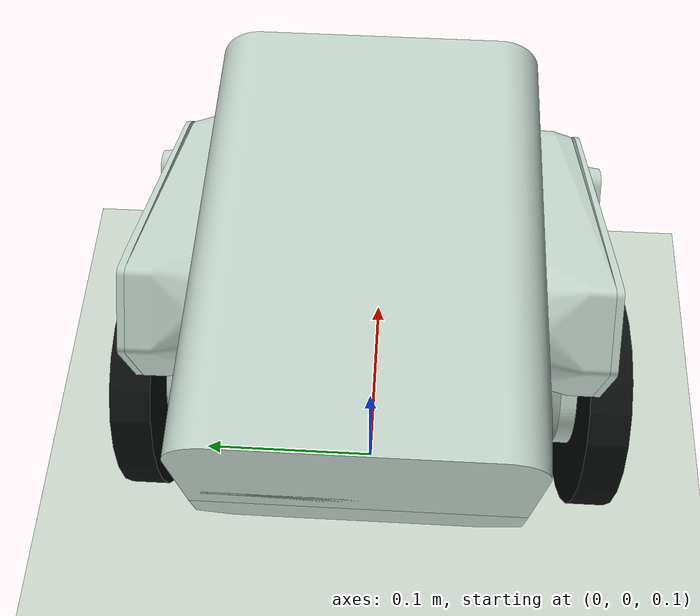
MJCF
<mujoco model="clanky_v2_drivetrain_explicit"><compiler angle="radian" autolimits="true" inertiafromgeom="false" /><option timestep="0.000125" integrator="RK4" iterations="100" tolerance="1e-10" gravity="0 0 -9.81"><flag energy="enable" /></option><default><joint damping=".0001" frictionloss=".001" /><geom friction="0.8 0.002 0.0001" solref="0.003 1" solimp=".95 .99 .001" contype="2" conaffinity="1" mass="0" /></default><asset><mesh name="D435i_native_front_face_outer" vertex="0.07755 -0.032 0.0216 0.07815 -0.032 0.0216 0.07755 0.042 0.0216 0.07815 0.042 0.0216 0.07815 0.0425903677 0.02162209 0.07815 0.0443285659 0.0219509748 0.07815 0.0448861941 0.0221460974 0.07815 0.04595 0.0226583993 0.07815 0.0464502285 0.0229727137 0.07815 0.0469255694 0.0233235313 0.07815 0.0473733646 0.0237088902 0.07815 0.0477911098 0.0241266354 0.07815 0.0495490252 0.0271714341 0.07815 0.0497019305 0.0277420846 0.07815 0.0498117635 0.0283225661 0.07815 0.04987791 0.0289096323 0.07815 0.0499 0.0295 0.07755 0.0425903677 0.02162209 0.07755 0.0431774339 0.0216882365 0.07755 0.0437579154 0.0217980695 0.07755 0.0448861941 0.0221460974 0.07755 0.0454276815 0.0223823459 0.07755 0.04595 0.0226583993 0.07755 0.0464502285 0.0229727137 0.07755 0.0473733646 0.0237088902 0.07755 0.0477911098 0.0241266354 0.07755 0.0481764687 0.0245744306 0.07755 0.0485272863 0.0250497715 0.07755 0.0491176541 0.0260723185 0.07755 0.0493539026 0.0266138059 0.07755 0.04987791 0.0289096323 0.07755 0.0499 0.0295 0.07755 0.0499 0.0385 0.07815 0.0499 0.0385 0.07815 0.04987791 0.0390903677 0.07815 0.0495490252 0.0408285659 0.07815 0.0493539026 0.0413861941 0.07815 0.0491176541 0.0419276815 0.07815 0.0488416007 0.04245 0.07815 0.0485272863 0.0429502285 0.07815 0.0477911098 0.0438733646 0.07815 0.0473733646 0.0442911098 0.07815 0.0464502285 0.0450272863 0.07815 0.04595 0.0453416007 0.07815 0.0454276815 0.0456176541 0.07815 0.0448861941 0.0458539026 0.07815 0.0437579154 0.0462019305 0.07815 0.0431774339 0.0463117635 0.07815 0.0425903677 0.04637791 0.07815 0.042 0.0464 0.07755 0.0497019305 0.0402579154 0.07755 0.0495490252 0.0408285659 0.07755 0.0491176541 0.0419276815 0.07755 0.0481764687 0.0434255694 0.07755 0.0477911098 0.0438733646 0.07755 0.0473733646 0.0442911098 0.07755 0.0464502285 0.0450272863 0.07755 0.0448861941 0.0458539026 0.07755 0.0443285659 0.0460490252 0.07755 0.0425903677 0.04637791 0.07755 0.042 0.0464 0.07755 -0.032 0.0464 0.07815 -0.032 0.0464 0.07815 -0.0325903677 0.04637791 0.07815 -0.0331774339 0.0463117635 0.07815 -0.0337579154 0.0462019305 0.07815 -0.0343285659 0.0460490252 0.07815 -0.0348861941 0.0458539026 0.07815 -0.0354276815 0.0456176541 0.07815 -0.03595 0.0453416007 0.07815 -0.0364502285 0.0450272863 0.07815 -0.0369255694 0.0446764687 0.07815 -0.0373733646 0.0442911098 0.07815 -0.0377911098 0.0438733646 0.07815 -0.0381764687 0.0434255694 0.07815 -0.0385272863 0.0429502285 0.07815 -0.0388416007 0.04245 0.07815 -0.0391176541 0.0419276815 0.07815 -0.0393539026 0.0413861941 0.07815 -0.0395490252 0.0408285659 0.07815 -0.0397019305 0.0402579154 0.07815 -0.0398117635 0.0396774339 0.07815 -0.03987791 0.0390903677 0.07815 -0.0399 0.0385 0.07755 -0.0399 0.0385 0.07755 -0.0337579154 0.0462019305 0.07755 -0.0343285659 0.0460490252 0.07755 -0.0348861941 0.0458539026 0.07755 -0.0354276815 0.0456176541 0.07755 -0.0364502285 0.0450272863 0.07755 -0.0377911098 0.0438733646 0.07755 -0.0381764687 0.0434255694 0.07755 -0.0388416007 0.04245 0.07755 -0.0391176541 0.0419276815 0.07755 -0.0397019305 0.0402579154 0.07755 -0.0398117635 0.0396774339 0.07755 -0.03987791 0.0390903677 0.07755 -0.0399 0.0295 0.07815 -0.0399 0.0295 0.07815 -0.03987791 0.0289096323 0.07815 -0.0395490252 0.0271714341 0.07815 -0.0393539026 0.0266138059 0.07815 -0.0391176541 0.0260723185 0.07815 -0.0388416007 0.02555 0.07815 -0.0381764687 0.0245744306 0.07815 -0.0377911098 0.0241266354 0.07815 -0.0373733646 0.0237088902 0.07815 -0.0364502285 0.0229727137 0.07815 -0.03595 0.0226583993 0.07815 -0.0354276815 0.0223823459 0.07815 -0.0348861941 0.0221460974 0.07815 -0.0343285659 0.0219509748 0.07815 -0.0337579154 0.0217980695 0.07815 -0.0331774339 0.0216882365 0.07815 -0.0325903677 0.02162209 0.07755 -0.0398117635 0.0283225661 0.07755 -0.0395490252 0.0271714341 0.07755 -0.0393539026 0.0266138059 0.07755 -0.0391176541 0.0260723185 0.07755 -0.0381764687 0.0245744306 0.07755 -0.0377911098 0.0241266354 0.07755 -0.0369255694 0.0233235313 0.07755 -0.03595 0.0226583993 0.07755 -0.0325903677 0.02162209 0.07755 0.0443285659 0.0219509748 0.07755 0.0469255694 0.0233235313 0.07755 0.0488416007 0.02555 0.07755 0.0495490252 0.0271714341 0.07755 0.0497019305 0.0277420846 0.07755 0.0498117635 0.0283225661 0.07755 0.04987791 0.0390903677 0.07755 0.0498117635 0.0396774339 0.07755 0.0493539026 0.0413861941 0.07755 0.0488416007 0.04245 0.07755 0.0485272863 0.0429502285 0.07755 0.0469255694 0.0446764687 0.07755 0.04595 0.0453416007 0.07755 0.0454276815 0.0456176541 0.07755 0.0437579154 0.0462019305 0.07755 0.0431774339 0.0463117635 0.07755 -0.0325903677 0.04637791 0.07755 -0.0331774339 0.0463117635 0.07755 -0.03595 0.0453416007 0.07755 -0.0369255694 0.0446764687 0.07755 -0.0373733646 0.0442911098 0.07755 -0.0385272863 0.0429502285 0.07755 -0.0393539026 0.0413861941 0.07755 -0.0395490252 0.0408285659 0.07755 -0.03987791 0.0289096323 0.07755 -0.0397019305 0.0277420846 0.07755 -0.0388416007 0.02555 0.07755 -0.0385272863 0.0250497715 0.07755 -0.0373733646 0.0237088902 0.07755 -0.0364502285 0.0229727137 0.07755 -0.0354276815 0.0223823459 0.07755 -0.0348861941 0.0221460974 0.07755 -0.0343285659 0.0219509748 0.07755 -0.0337579154 0.0217980695 0.07755 -0.0331774339 0.0216882365 0.07815 0.0431774339 0.0216882365 0.07815 0.0437579154 0.0217980695 0.07815 0.0454276815 0.0223823459 0.07815 0.0481764687 0.0245744306 0.07815 0.0485272863 0.0250497715 0.07815 0.0488416007 0.02555 0.07815 0.0491176541 0.0260723185 0.07815 0.0493539026 0.0266138059 0.07815 0.0498117635 0.0396774339 0.07815 0.0497019305 0.0402579154 0.07815 0.0481764687 0.0434255694 0.07815 0.0469255694 0.0446764687 0.07815 0.0443285659 0.0460490252 0.07815 -0.0398117635 0.0283225661 0.07815 -0.0397019305 0.0277420846 0.07815 -0.0385272863 0.0250497715 0.07815 -0.0369255694 0.0233235313" /><mesh name="left_drive_encoder_service_cap_outer" vertex="0.1128322389 0.0635 0.044 0.1138784603 0.0635 0.0439608532 0.1149188307 0.0635 0.0438436316 0.1169588114 0.0635 0.0433780193 0.1179470133 0.0635 0.0430322325 0.1189066113 0.0635 0.0426135642 0.1198322389 0.0635 0.0421243557 0.1215610962 0.0635 0.0409456408 0.1223546573 0.0635 0.0402627262 0.1230949651 0.0635 0.0395224183 0.1258644714 0.0635 0.0351147743 0.1262102582 0.0635 0.0341265724 0.1264812297 0.0635 0.0331152931 0.1267930921 0.0635 0.0310462213 0.1268322389 0.0635 0.03 0.1267930921 0.0635 0.0289537787 0.1266758705 0.0635 0.0279134083 0.1264812297 0.0635 0.0268847069 0.1262102582 0.0635 0.0258734276 0.1258644714 0.0635 0.0248852257 0.1254458031 0.0635 0.0239256277 0.1249565946 0.0635 0.023 0.1243995818 0.0635 0.0221135192 0.1237778797 0.0635 0.0212711428 0.1215610962 0.0635 0.0190543592 0.1198322389 0.0635 0.0178756443 0.1169588114 0.0635 0.0166219807 0.115947532 0.0635 0.0163510092 0.1138784603 0.0635 0.0160391468 0.1128322389 0.0635 0.016 0.1107456472 0.0635 0.0161563684 0.1097169459 0.0635 0.0163510092 0.1087056665 0.0635 0.0166219807 0.1077174646 0.0635 0.0169677675 0.1067578666 0.0635 0.0173864358 0.1041033817 0.0635 0.0190543592 0.1025695127 0.0635 0.0204775817 0.1018865982 0.0635 0.0212711428 0.1012648961 0.0635 0.0221135192 0.1007078833 0.0635 0.023 0.1002186748 0.0635 0.0239256277 0.0998000065 0.0635 0.0248852257 0.0988713858 0.0635 0.0289537787 0.0988322389 0.0635 0.03 0.0989886074 0.0635 0.0320865917 0.1007078833 0.0635 0.037 0.1012648961 0.0635 0.0378864808 0.1018865982 0.0635 0.0387288572 0.1025695127 0.0635 0.0395224183 0.1033098206 0.0635 0.0402627262 0.1049457581 0.0635 0.0415673428 0.1067578666 0.0635 0.0426135642 0.1077174646 0.0635 0.0430322325 0.1107456472 0.0635 0.0438436316 0.0942698032 0.072 0.021300231 0.0928224922 0.072 0.0255435402 0.0925506145 0.072 0.0270157564 0.0923869057 0.072 0.0285038885 0.0923322389 0.072 0.03 0.0923869057 0.072 0.0314961115 0.0925506145 0.072 0.0329842436 0.0928224922 0.072 0.0344564598 0.0936843849 0.072 0.0373218636 0.1296476778 0.072 0.0182743436 0.125557482 0.072 0.0139277198 0.1243505761 0.072 0.0130418778 0.1203886204 0.072 0.0109434762 0.1175340136 0.072 0.0100464711 0.1160652461 0.072 0.0097565402 0.1145792358 0.072 0.0095745746 0.1130839083 0.072 0.0095015449 0.1143409003 0.072 0.050444411 0.118785331 0.072 0.0496165923 0.1202128368 0.072 0.0491252915 0.1216003153 0.072 0.0485302681 0.1229402417 0.072 0.0478347492 0.1242253492 0.072 0.0470425068 0.1254486683 0.072 0.0461578375 0.1266035644 0.072 0.045185539 0.1286834395 0.072 0.0429995938 0.1295971387 0.072 0.0417978022 0.1304199165 0.072 0.0405320273 0.115947532 0.0635 0.0436489908 0.1207187198 0.0635 0.0415673428 0.1237778797 0.0635 0.0387288572 0.1243995818 0.0635 0.0378864808 0.1249565946 0.0635 0.037 0.1254458031 0.0635 0.0360743723 0.1266758705 0.0635 0.0320865917 0.1230949651 0.0635 0.0204775817 0.1223546573 0.0635 0.0197372738 0.1207187198 0.0635 0.0184326572 0.1189066113 0.0635 0.0173864358 0.1179470133 0.0635 0.0169677675 0.1149188307 0.0635 0.0161563684 0.1117860176 0.0635 0.0160391468 0.1058322389 0.0635 0.0178756443 0.1049457581 0.0635 0.0184326572 0.1033098206 0.0635 0.0197372738 0.0994542197 0.0635 0.0258734276 0.0991832482 0.0635 0.0268847069 0.0989886074 0.0635 0.0279134083 0.0988713858 0.0635 0.0310462213 0.0991832482 0.0635 0.0331152931 0.0994542197 0.0635 0.0341265724 0.0998000065 0.0635 0.0351147743 0.1002186748 0.0635 0.0360743723 0.1041033817 0.0635 0.0409456408 0.1058322389 0.0635 0.0421243557 0.1087056665 0.0635 0.0433780193 0.1097169459 0.0635 0.0436489908 0.1117860176 0.0635 0.0439608532 0.1296459536 0.0745 0.0417281286 0.1277602374 0.0745 0.044050084 0.1266954096 0.0745 0.0451017383 0.1243501605 0.0745 0.0469584045 0.1230822389 0.0745 0.0477535208 0.1217596872 0.0745 0.0484540149 0.1189791426 0.0745 0.0495567271 0.1175359694 0.0745 0.0499530679 0.1160677264 0.0745 0.0502430635 0.1128322389 0.072 0.0505 0.1158413798 0.072 0.0502779454 0.1173255397 0.072 0.0500015062 0.1276837743 0.072 0.0441308846 0.0949542214 0.072 0.0199687245 0.0936843849 0.072 0.0226781364 0.0932010887 0.072 0.0240950919 0.0932010887 0.072 0.0359049081 0.0942698032 0.072 0.038699769 0.0949542214 0.072 0.0400312755 0.0942685243 0.0745 0.0213029603 0.093683488 0.0745 0.0226804825 0.09320051 0.0745 0.0240970161 0.0928221646 0.0745 0.0255450112 0.0925504683 0.0745 0.0270167504 0.0923868691 0.0745 0.0285043896 0.0923322389 0.0745 0.03 0.0928221646 0.0745 0.0344549888 0.093683488 0.0745 0.0373195175 0.1304585872 0.072 0.0195328204 0.1287470858 0.072 0.0170784038 0.1277616145 0.072 0.0159513793 0.1266965197 0.072 0.0148992809 0.1230822389 0.072 0.0122464792 0.121759235 0.072 0.0115457663 0.1189777049 0.072 0.0104428211 0.1296459536 0.0745 0.0182718714 0.1287455025 0.0745 0.0170764539 0.1277602374 0.0745 0.015949916 0.1266954096 0.0745 0.0148982617 0.1243501605 0.0745 0.0130415955 0.1230822389 0.0745 0.0122464792 0.1203895543 0.0745 0.0109438465 0.1145822389 0.0745 0.0095748317 0.1287455025 0.0745 0.0429235461 0.1255566942 0.0745 0.0460729038 0.1203895543 0.0745 0.0490561535 0.1145822389 0.0745 0.0504251683 0.1363122471 0.0745 0.0318356337 0.1364391792 0.0745 0.0316114968 0.1365492834 0.0745 0.0313786316 0.1366419632 0.0745 0.0311382994 0.136773139 0.0745 0.030640474 0.1368109245 0.0745 0.0303856773 0.1368298685 0.0745 0.0301287916 0.1368298685 0.0745 0.0298712084 0.1368109245 0.0745 0.0296143227 0.1367167167 0.0745 0.0291081982 0.1366419632 0.0745 0.0288617006 0.1365492834 0.0745 0.0286213684 0.1363122471 0.0745 0.0281643663 0.1361691745 0.0745 0.0279501716 0.1255566942 0.0745 0.0139270962 0.1217596872 0.0745 0.0115459851 0.1189791426 0.0745 0.0104432729 0.1175359694 0.0745 0.0100469321 0.1160677264 0.0745 0.0097569365 0.1029389746 0.0745 0.0087647067 0.1026819403 0.0745 0.0087478996 0.1021676467 0.0745 0.0087711212 0.1016623231 0.0745 0.0088695346 0.1014164557 0.0745 0.0089463354 0.1007218873 0.0745 0.009281839 0.1005088898 0.0745 0.0094266878 0.1003071221 0.0745 0.0095868094 0.0997797867 0.0745 0.0101497528 0.0995025294 0.0745 0.0105835333 0.0923868691 0.0745 0.0314956104 0.0925504683 0.0745 0.0329832496 0.09320051 0.0745 0.0359029839 0.0942685243 0.0745 0.0386970397 0.0995025294 0.0745 0.0494164667 0.0996331716 0.0745 0.0496384616 0.0997797867 0.0745 0.0498502472 0.0999415806 0.0745 0.0500506764 0.100117677 0.0745 0.0502386636 0.1003071221 0.0745 0.0504131906 0.1005088898 0.0745 0.0505733122 0.1007218873 0.0745 0.050718161 0.1011769025 0.0745 0.0509589895 0.1016623231 0.0745 0.0511304654 0.101913173 0.0745 0.0511889757 0.102424366 0.0745 0.0512499584 0.1026819403 0.0745 0.0512521004 0.1029389746 0.0745 0.0512352933 0.0995025294 0.0725 0.0494164667 0.0996331716 0.0725 0.0496384616 0.0997797867 0.0725 0.0498502472 0.100117677 0.0725 0.0502386636 0.100944961 0.0725 0.0508469527 0.1011769025 0.0725 0.0509589895 0.1014164557 0.0725 0.0510536646 0.1016623231 0.0725 0.0511304654 0.101913173 0.0725 0.0511889757 0.1021676467 0.0725 0.0512288788 0.102424366 0.0725 0.0512499584 0.1026819403 0.0725 0.0512521004 0.1029389746 0.0725 0.0512352933 0.0993885677 0.0745 0.0491854648 0.100944961 0.0745 0.0508469527 0.1014164557 0.0745 0.0510536646 0.1021676467 0.0745 0.0512288788 0.0993885677 0.0725 0.0491854648 0.0999415806 0.0725 0.0500506764 0.1003071221 0.0725 0.0504131906 0.1005088898 0.0725 0.0505733122 0.1007218873 0.0725 0.050718161 0.1361691745 0.0725 0.0320498284 0.1363122471 0.0725 0.0318356337 0.1366419632 0.0725 0.0311382994 0.1368109245 0.0725 0.0303856773 0.1368298685 0.0725 0.0301287916 0.1368109245 0.0725 0.0296143227 0.1361691745 0.0725 0.0279501716 0.1364391792 0.0725 0.0316114968 0.1365492834 0.0725 0.0313786316 0.1367167167 0.0725 0.0308918018 0.136773139 0.0725 0.030640474 0.1368298685 0.0725 0.0298712084 0.136773139 0.0725 0.029359526 0.1367167167 0.0725 0.0291081982 0.1366419632 0.0725 0.0288617006 0.1365492834 0.0725 0.0286213684 0.1364391792 0.0725 0.0283885032 0.1363122471 0.0725 0.0281643663 0.1361691745 0.0745 0.0320498284 0.1367167167 0.0745 0.0308918018 0.136773139 0.0745 0.029359526 0.1364391792 0.0745 0.0283885032 0.1029389746 0.0725 0.0087647067 0.1026819403 0.0725 0.0087478996 0.102424366 0.0725 0.0087500416 0.1021676467 0.0725 0.0087711212 0.101913173 0.0725 0.0088110243 0.1016623231 0.0725 0.0088695346 0.1014164557 0.0725 0.0089463354 0.1011769025 0.0725 0.0090410105 0.1005088898 0.0725 0.0094266878 0.0999415806 0.0725 0.0099493236 0.0997797867 0.0725 0.0101497528 0.0996331716 0.0725 0.0103615384 0.0995025294 0.0725 0.0105835333 0.102424366 0.0745 0.0087500416 0.101913173 0.0745 0.0088110243 0.1011769025 0.0745 0.0090410105 0.100944961 0.0745 0.0091530473 0.100117677 0.0745 0.0097613364 0.0999415806 0.0745 0.0099493236 0.0996331716 0.0745 0.0103615384 0.0993885677 0.0745 0.0108145352 0.100944961 0.0725 0.0091530473 0.1007218873 0.0725 0.009281839 0.1003071221 0.0725 0.0095868094 0.100117677 0.0725 0.0097613364 0.0993885677 0.0725 0.0108145352" /><mesh name="left_drive_shin_case_outer" vertex="0.1083654305 0.1 -0.0276414114 0.1406517652 0.0977 0.0031739504 0.1408160858 0.0977 -0.0009509546 0.1406698445 0.0977 -0.0030112648 0.1399245334 0.0977 -0.0070716039 0.1377109456 0.0977 -0.0128471769 0.1366961939 0.0977 -0.0146462164 0.1355515825 0.0977 -0.0163655562 0.13428334 0.0977 -0.0179958401 0.1263505581 0.0977 -0.0245205026 0.1245061884 0.0977 -0.0254503223 0.1225982929 0.0977 -0.0262416499 0.1206372539 0.0977 -0.0268901793 0.1186337425 0.0977 -0.0273923813 0.1165986614 0.0977 -0.0277455233 0.1145430846 0.0977 -0.0279476834 0.1341103968 0.11 0.0182 0.1398956276 0.11 0.0071814338 0.1403561142 0.11 0.0051416234 0.1406630823 0.11 0.0030731347 0.1408104804 0.11 -0.0011036322 0.140334538 0.11 -0.0052558108 0.1384788021 0.11 -0.0112362715 0.137568698 0.11 -0.0131189784 0.1365206226 0.11 -0.0149285122 0.1353404219 0.11 -0.0166547801 0.1326106753 0.11 -0.0198195221 0.131076355 0.11 -0.0212403444 0.1294402755 0.11 -0.0225426955 0.1277115622 0.11 -0.0237193115 0.124015266 0.11 -0.0256698248 0.1200698177 0.11 -0.0270484279 0.1180309672 0.11 -0.0275131464 0.1138778099 0.11 -0.0279804714 0.111786668 0.11 -0.0279804714 0.1097013578 0.11 -0.0278244063 0.1076335107 0.11 -0.0275131464 0.1055946602 0.11 -0.0270484279 0.1035961783 0.11 -0.0264328429 0.1016492119 0.11 -0.0256698248 0.0997646205 0.11 -0.0247636295 0.0979529156 0.11 -0.0237193115 0.0916297995 0.11 -0.0182881535 0.090324056 0.11 -0.0166547801 0.0891438552 0.11 -0.0149285122 0.0880957799 0.11 -0.0131189784 0.0864186191 0.11 -0.0092908927 0.0857988883 0.11 -0.0072936926 0.084849658 0.11 0.0009875052 0.0850013956 0.11 0.0030731347 0.0857688502 0.11 0.0071814338 0.0890821018 0.11 0.0148300703 0.0902551279 0.11 0.0165612215 0.0915540811 0.11 0.0182 0.1083654305 0.0977 -0.0276414114 -0.0015952887 0.0977 -0.0098719326 -0.0023231254 0.0977 -0.0097264119 -0.0030381635 0.0977 -0.0095273061 -0.0037364637 0.0977 -0.0092757123 -0.0044141788 0.0977 -0.0089730165 -0.0050675753 0.0977 -0.0086208863 -0.0056930533 0.0977 -0.0082212617 -0.0068466433 0.0977 -0.0072885853 -0.0078495622 0.0977 -0.0061955123 -0.0082874796 0.0977 -0.0055962203 -0.0086797394 0.0977 -0.0049660974 -0.0090241806 0.0977 -0.0043086152 -0.0093189055 0.0977 -0.0036273959 -0.0095622904 0.0977 -0.0029261924 -0.0097529946 0.0977 -0.0022088678 -0.01 0.0977 0 -0.0099724539 0.0977 0.0007417303 -0.0098899672 0.0977 0.0014793742 -0.0097529946 0.0977 0.0022088678 -0.0095622904 0.0977 0.0029261924 -0.0073683998 0.0977 0.0067606719 -0.0068466433 0.0977 0.0072885853 -0.006287167 0.0977 0.0077763443 -0.0056930533 0.0977 0.0082212617 -0.0050675753 0.0977 0.0086208863 -0.0044141788 0.0977 0.0089730165 0.1408100484 0.0977 0.0011145303 0.1403721203 0.0977 -0.0050551887 0.1393295193 0.0977 -0.0090495379 0.1385903158 0.0977 -0.0109782273 0.1328983679 0.0977 -0.0195281967 0.1314042027 0.0977 -0.0209542875 0.1298089751 0.0977 -0.022266352 0.1281213657 0.0977 -0.0234572505 0.112478198 0.0977 -0.0279977616 0.110415238 0.0977 -0.0278954854 0.1128322389 0.1 0.0505 0.1158678918 0.1 0.0502739935 0.1173647608 0.1 0.0499926548 0.1188366103 0.1 0.0496009572 0.1230217556 0.1 0.0477883038 0.1243143294 0.1 0.0469826853 0.1255435223 0.1 0.0460833229 0.1267025494 0.1 0.045095181 0.1287849371 0.1 0.0428748367 0.1296968031 0.1 0.0416548906 0.1305155772 0.1 0.0403706098 0.1312367398 0.1 0.0390290835 0.1143412444 0.077 0.0504443856 0.1173265496 0.077 0.0500012792 0.1229423429 0.077 0.0478335582 0.1295997197 0.077 0.0417941337 0.1266954096 0.077 0.0148982617 0.1255566942 0.077 0.0139270962 0.1217596872 0.077 0.0115459851 0.1203895543 0.077 0.0109438465 0.1175359694 0.077 0.0100469321 0.1160677264 0.077 0.0097569365 0.1145822389 0.077 0.0095748317 0.0941707606 0.077 0.0215147642 0.093588004 0.077 0.02293534 0.0931132093 0.077 0.0243955492 0.0924975395 0.077 0.0274019238 0.0924975395 0.077 0.0325980762 0.0927490401 0.077 0.0341128001 0.0931132093 0.077 0.0356044508 0.093588004 0.077 0.03706466 0.0941707606 0.077 0.0384852358 0.1069783562 0.1 0.0496464261 0.1084147795 0.1 0.0500183928 0.1098743456 0.1 0.0502854842 0.1113494081 0.1 0.0504463007 0.1192916797 0.11 0.035525 0.1063727982 0.11 0.035525 0.1067865978 0.11 0.0359749664 0.1077057049 0.11 0.0367800183 0.108730739 0.11 0.037444978 0.1092764338 0.11 0.0377205084 0.1104200811 0.11 0.0381505518 0.1116135696 0.11 0.0384121843 0.1122213244 0.11 0.0384780177 0.1128322389 0.11 0.0385 0.1134431535 0.11 0.0384780177 0.1140509082 0.11 0.0384121843 0.1152443968 0.11 0.0381505518 0.1158239575 0.11 0.0379561058 0.1163880441 0.11 0.0377205084 0.1169337389 0.11 0.037444978 0.1174582195 0.11 0.0371309399 0.117958773 0.11 0.0367800183 0.1184328105 0.11 0.0363940283 0.1188778801 0.11 0.0359749664 0.13540935 0.11 0.0165612215 0.1365823761 0.11 0.0148300703 0.1376229324 0.11 0.0130162022 0.1385252149 0.11 0.0111297344 0.1392841911 0.11 0.0091811888 0.1408148198 0.11 0.0009875052 0.1406500883 0.11 -0.003188614 0.1398655896 0.11 -0.0072936926 0.1392458588 0.11 -0.0092908927 0.1340346784 0.11 -0.0182881535 0.1258998574 0.11 -0.0247636295 0.1220682996 0.11 -0.0264328429 0.11596312 0.11 -0.0278244063 0.0962242024 0.11 -0.0225426955 0.0945881229 0.11 -0.0212403444 0.0930538026 0.11 -0.0198195221 0.0871856758 0.11 -0.0112362715 0.0853299399 0.11 -0.0052558108 0.0850143896 0.11 -0.003188614 0.0848539975 0.11 -0.0011036322 0.0853083637 0.11 0.0051416234 0.0863802868 0.11 0.0091811888 0.087139263 0.11 0.0111297344 0.0880415455 0.11 0.0130162022 -0.0015952887 0.1 -0.0098719326 -0.0023231254 0.1 -0.0097264119 -0.0050675753 0.1 -0.0086208863 -0.0056930533 0.1 -0.0082212617 -0.0068466433 0.1 -0.0072885853 -0.0073683998 0.1 -0.0067606719 -0.0078495622 0.1 -0.0061955123 -0.0093189055 0.1 -0.0036273959 -0.0098899672 0.1 -0.0014793742 -0.0099724539 0.1 -0.0007417303 -0.0093189055 0.1 0.0036273959 -0.0086797394 0.1 0.0049660974 -0.0082874796 0.1 0.0055962203 -0.0078495622 0.1 0.0061955123 -0.0068466433 0.1 0.0072885853 -0.0056930533 0.1 0.0082212617 -0.0050675753 0.1 0.0086208863 0.1143542662 0.1 0.0504434203 0.1202753159 0.1 0.0491010629 0.121672936 0.1 0.0484957313 0.1277850127 0.1 0.0440237141 0.13185631 0.1 0.037637717 0.1323708679 0.1 0.0362041905 -0.0030381635 0.1 -0.0095273061 -0.0037364637 0.1 -0.0092757123 -0.0044141788 0.1 -0.0089730165 -0.006287167 0.1 -0.0077763443 -0.0082874796 0.1 -0.0055962203 -0.0086797394 0.1 -0.0049660974 -0.0090241806 0.1 -0.0043086152 -0.0095622904 0.1 -0.0029261924 -0.0097529946 0.1 -0.0022088678 -0.01 0.1 0 -0.0099724539 0.1 0.0007417303 -0.0098899672 0.1 0.0014793742 -0.0097529946 0.1 0.0022088678 -0.0095622904 0.1 0.0029261924 -0.0090241806 0.1 0.0043086152 -0.0073683998 0.1 0.0067606719 -0.006287167 0.1 0.0077763443 -0.006287167 0.0977 -0.0077763443 -0.0073683998 0.0977 -0.0067606719 -0.0098899672 0.0977 -0.0014793742 -0.0099724539 0.0977 -0.0007417303 -0.0093189055 0.0977 0.0036273959 -0.0090241806 0.0977 0.0043086152 -0.0086797394 0.0977 0.0049660974 -0.0082874796 0.0977 0.0055962203 -0.0078495622 0.0977 0.0061955123 0.1029389746 0.077 0.0512352933 0.1026819403 0.077 0.0512521004 0.1016623231 0.077 0.0511304654 0.100944961 0.077 0.0508469527 0.100117677 0.077 0.0502386636 0.0997797867 0.077 0.0498502472 0.0996331716 0.077 0.0496384616 0.0993885677 0.077 0.0491854648 0.1158420624 0.077 0.0502778441 0.1187866517 0.077 0.0496161915 0.1202144463 0.077 0.0491246703 0.1216021865 0.077 0.0485293826 0.1242276438 0.077 0.0470409726 0.1254511157 0.077 0.0461559262 0.1266061201 0.077 0.045183221 0.1276863902 0.077 0.0441281347 0.1286860647 0.077 0.0429963921 0.1363269907 0.077 0.0318114806 0.1364516789 0.077 0.0315871655 0.1365595949 0.077 0.0313543167 0.1366501584 0.077 0.0311141862 0.136777376 0.077 0.0306172765 0.1368305996 0.077 0.0301071091 0.1368290434 0.077 0.0298504732 0.1367696368 0.077 0.0293409888 0.1367121058 0.077 0.0290908797 0.1366364023 0.077 0.0288456585 0.1364322016 0.077 0.028375121 0.1363048022 0.077 0.0281523346 0.1361614203 0.077 0.0279394824 0.1296459536 0.077 0.0182718714 0.1287455025 0.077 0.0170764539 0.1277602374 0.077 0.015949916 0.1243501605 0.077 0.0130415955 0.1230822389 0.077 0.0122464792 0.1189791426 0.077 0.0104432729 0.1029389746 0.077 0.0087647067 0.1026819403 0.077 0.0087478996 0.102424366 0.077 0.0087500416 0.1021676467 0.077 0.0087711212 0.101913173 0.077 0.0088110243 0.100944961 0.077 0.0091530473 0.0996331716 0.077 0.0103615384 0.0993885677 0.077 0.0108145352 0.0927490401 0.077 0.0258871999 0.1029389746 0.083 0.0512352933 0.1026819403 0.083 0.0512521004 0.102424366 0.083 0.0512499584 0.1021676467 0.083 0.0512288788 0.102424366 0.077 0.0512499584 0.1021676467 0.077 0.0512288788 0.101913173 0.077 0.0511889757 0.1014164557 0.077 0.0510536646 0.1011769025 0.077 0.0509589895 0.1007218873 0.077 0.050718161 0.1005088898 0.077 0.0505733122 0.1003071221 0.077 0.0504131906 0.0999415806 0.077 0.0500506764 0.0995025294 0.077 0.0494164667 0.102521671 0.0795 0.0512529967 0.1020178502 0.0795 0.0512077161 0.1017697101 0.0795 0.0511578999 0.1015258187 0.0795 0.0510902821 0.1015258187 0.0811 0.0510902821 0.1017697101 0.0811 0.0511578999 0.1020178502 0.0811 0.0512077161 0.1022689415 0.0811 0.0512394704 0.1027747172 0.0811 0.0512482242 0.101913173 0.083 0.0511889757 0.1016623231 0.083 0.0511304654 0.1014164557 0.083 0.0510536646 0.1016623231 0.077 0.0088695346 0.1014164557 0.077 0.0089463354 0.1011769025 0.077 0.0090410105 0.1007218873 0.077 0.009281839 0.1005088898 0.077 0.0094266878 0.1003071221 0.077 0.0095868094 0.100117677 0.077 0.0097613364 0.0999415806 0.077 0.0099493236 0.0997797867 0.077 0.0101497528 0.0995025294 0.077 0.0105835333 0.1361862007 0.083 0.0320260559 0.1365595949 0.083 0.0313543167 0.1366501584 0.083 0.0311141862 0.1361862007 0.077 0.0320260559 0.1367228824 0.077 0.030868065 0.1368133463 0.077 0.0303631692 0.136808686 0.077 0.0295946413 0.1365429334 0.077 0.028606644 0.1362625018 0.0795 0.0319140428 0.1365078086 0.0795 0.0314716513 0.1362625018 0.0811 0.0319140428 0.1363931579 0.0811 0.0316972846 0.1365078086 0.0811 0.0314716513 0.1366058542 0.0811 0.0312383227 0.1366867821 0.0811 0.0309985189 0.1367501691 0.0811 0.0307534939 0.1367956838 0.0811 0.0305045289 0.1363269907 0.083 0.0318114806 0.1364516789 0.083 0.0315871655 0.1367228824 0.083 0.030868065 0.136777376 0.083 0.0306172765 0.1072316674 0.11 0.0363940283 0.1082062584 0.11 0.0371309399 0.1098405204 0.11 0.0379561058 0.1110121183 0.11 0.0383028405 0.1146523596 0.11 0.0383028405 0.014 0.1055 0.0195 0.014 0.099 0.0195 -0.0020026884 0.1085 -0.0087743512 -0.0026527966 0.1085 -0.0086001553 -0.0032880692 0.1085 -0.0083778637 -0.0039049537 0.1085 -0.0081087198 -0.0045 0.1085 -0.0077942286 -0.0061215546 0.1085 -0.0065974668 -0.0065974668 0.1085 -0.0061215546 -0.0070364833 0.1085 -0.0056114082 -0.007436149 0.1085 -0.0050698805 -0.0077942286 0.1085 -0.0045 -0.0081087198 0.1085 -0.0039049537 -0.0086001553 0.1085 -0.0026527966 -0.0087743512 0.1085 -0.0020026884 -0.0088994774 0.1085 -0.0013413804 -0.0089748342 0.1085 -0.0006725708 -0.0089748342 0.1085 0.0006725708 -0.0081087198 0.1085 0.0039049537 -0.0077942286 0.1085 0.0045 -0.007436149 0.1085 0.0050698805 -0.0065974668 0.1085 0.0061215546 -0.0050698805 0.1085 0.007436149 -0.0045 0.1085 0.0077942286 -0.0039049537 0.1085 0.0081087198 -0.0032880692 0.1085 0.0083778637 -0.0013413804 0.1085 -0.0088994774 -0.0050698805 0.1085 -0.007436149 -0.0056114082 0.1085 -0.0070364833 -0.0083778637 0.1085 -0.0032880692 -0.009 0.1085 -0 -0.0088994774 0.1085 0.0013413804 -0.0087743512 0.1085 0.0020026884 -0.0086001553 0.1085 0.0026527966 -0.0083778637 0.1085 0.0032880692 -0.0070364833 0.1085 0.0056114082 -0.0061215546 0.1085 0.0065974668 -0.0056114082 0.1085 0.0070364833 -0.0026527966 0.1085 0.0086001553 0.1027747172 0.0795 0.0512482242 0.1022689415 0.0795 0.0512394704 0.102521671 0.0811 0.0512529967 0.1363931579 0.0795 0.0316972846 0.1366058542 0.0795 0.0312383227 0.1366867821 0.0795 0.0309985189 0.1367501691 0.0795 0.0307534939 0.1367956838 0.0795 0.0305045289" /><mesh name="left_drive_bearing_service_lid_outer" vertex="0.0915540811 0.11 0.0182 0.1341103968 0.11 0.0182 0.13540935 0.112 0.0165612215 0.1376229324 0.112 0.0130162022 0.1398956276 0.112 0.0071814338 0.1403561142 0.112 0.0051416234 0.1408148198 0.112 0.0009875052 0.1406500883 0.112 -0.003188614 0.1398655896 0.112 -0.0072936926 0.1392458588 0.112 -0.0092908927 0.1365206226 0.112 -0.0149285122 0.1353404219 0.112 -0.0166547801 0.131076355 0.112 -0.0212403444 0.1277115622 0.112 -0.0237193115 0.124015266 0.112 -0.0256698248 0.1180309672 0.112 -0.0275131464 0.11596312 0.112 -0.0278244063 0.1138778099 0.112 -0.0279804714 0.1097013578 0.112 -0.0278244063 0.1076335107 0.112 -0.0275131464 0.1055946602 0.112 -0.0270484279 0.1016492119 0.112 -0.0256698248 0.090324056 0.112 -0.0166547801 0.0871856758 0.112 -0.0112362715 0.0864186191 0.112 -0.0092908927 0.0850143896 0.112 -0.003188614 0.0848539975 0.112 -0.0011036322 0.084849658 0.112 0.0009875052 0.0850013956 0.112 0.0030731347 0.0853083637 0.112 0.0051416234 0.087139263 0.112 0.0111297344 0.0880415455 0.112 0.0130162022 0.0890821018 0.112 0.0148300703 0.0902551279 0.112 0.0165612215 0.0915540811 0.112 0.0182 0.1365823761 0.11 0.0148300703 0.1385252149 0.11 0.0111297344 0.1408148198 0.11 0.0009875052 0.1408104804 0.11 -0.0011036322 0.1406500883 0.11 -0.003188614 0.140334538 0.11 -0.0052558108 0.1398655896 0.11 -0.0072936926 0.1392458588 0.11 -0.0092908927 0.137568698 0.11 -0.0131189784 0.1353404219 0.11 -0.0166547801 0.1326106753 0.11 -0.0198195221 0.131076355 0.11 -0.0212403444 0.1294402755 0.11 -0.0225426955 0.1277115622 0.11 -0.0237193115 0.1258998574 0.11 -0.0247636295 0.11596312 0.11 -0.0278244063 0.1138778099 0.11 -0.0279804714 0.1097013578 0.11 -0.0278244063 0.1076335107 0.11 -0.0275131464 0.1055946602 0.11 -0.0270484279 0.1016492119 0.11 -0.0256698248 0.0997646205 0.11 -0.0247636295 0.0979529156 0.11 -0.0237193115 0.0962242024 0.11 -0.0225426955 0.0945881229 0.11 -0.0212403444 0.0930538026 0.11 -0.0198195221 0.0891438552 0.11 -0.0149285122 0.0880957799 0.11 -0.0131189784 0.0871856758 0.11 -0.0112362715 0.0853299399 0.11 -0.0052558108 0.0850143896 0.11 -0.003188614 0.0850013956 0.11 0.0030731347 0.0857688502 0.11 0.0071814338 0.0880415455 0.11 0.0130162022 0.1063727982 0.112 0.035525 0.1067865978 0.112 0.0359749664 0.1082062584 0.112 0.0371309399 0.108730739 0.112 0.037444978 0.1116135696 0.112 0.0384121843 0.1122213244 0.112 0.0384780177 0.1128322389 0.112 0.0385 0.1134431535 0.112 0.0384780177 0.1140509082 0.112 0.0384121843 0.1146523596 0.112 0.0383028405 0.1158239575 0.112 0.0379561058 0.1163880441 0.112 0.0377205084 0.1169337389 0.112 0.037444978 0.1184328105 0.112 0.0363940283 0.1188778801 0.112 0.0359749664 0.1192916797 0.11 0.035525 0.1072316674 0.11 0.0363940283 0.108730739 0.11 0.037444978 0.1092764338 0.11 0.0377205084 0.1110121183 0.11 0.0383028405 0.1116135696 0.11 0.0384121843 0.1122213244 0.11 0.0384780177 0.1128322389 0.11 0.0385 0.1134431535 0.11 0.0384780177 0.1158239575 0.11 0.0379561058 0.1163880441 0.11 0.0377205084 0.117958773 0.11 0.0367800183 0.1184328105 0.11 0.0363940283 0.1188778801 0.11 0.0359749664 0.1063727982 0.11 0.035525 0.1067865978 0.11 0.0359749664 0.1077057049 0.11 0.0367800183 0.1082062584 0.11 0.0371309399 0.1098405204 0.11 0.0379561058 0.1104200811 0.11 0.0381505518 0.1140509082 0.11 0.0384121843 0.1146523596 0.11 0.0383028405 0.1152443968 0.11 0.0381505518 0.1169337389 0.11 0.037444978 0.1174582195 0.11 0.0371309399 0.13540935 0.11 0.0165612215 0.1376229324 0.11 0.0130162022 0.1392841911 0.11 0.0091811888 0.1398956276 0.11 0.0071814338 0.1403561142 0.11 0.0051416234 0.1406630823 0.11 0.0030731347 0.1384788021 0.11 -0.0112362715 0.1365206226 0.11 -0.0149285122 0.1340346784 0.11 -0.0182881535 0.124015266 0.11 -0.0256698248 0.1220682996 0.11 -0.0264328429 0.1200698177 0.11 -0.0270484279 0.1180309672 0.11 -0.0275131464 0.111786668 0.11 -0.0279804714 0.1035961783 0.11 -0.0264328429 0.0916297995 0.11 -0.0182881535 0.090324056 0.11 -0.0166547801 0.0864186191 0.11 -0.0092908927 0.0857988883 0.11 -0.0072936926 0.0848539975 0.11 -0.0011036322 0.084849658 0.11 0.0009875052 0.0853083637 0.11 0.0051416234 0.0863802868 0.11 0.0091811888 0.087139263 0.11 0.0111297344 0.0890821018 0.11 0.0148300703 0.0902551279 0.11 0.0165612215 0.1072316674 0.112 0.0363940283 0.1077057049 0.112 0.0367800183 0.1092764338 0.112 0.0377205084 0.1098405204 0.112 0.0379561058 0.1104200811 0.112 0.0381505518 0.1110121183 0.112 0.0383028405 0.1152443968 0.112 0.0381505518 0.1174582195 0.112 0.0371309399 0.117958773 0.112 0.0367800183 0.1192916797 0.112 0.035525 0.1341103968 0.112 0.0182 0.1365823761 0.112 0.0148300703 0.1385252149 0.112 0.0111297344 0.1392841911 0.112 0.0091811888 0.1406630823 0.112 0.0030731347 0.1408104804 0.112 -0.0011036322 0.140334538 0.112 -0.0052558108 0.1384788021 0.112 -0.0112362715 0.137568698 0.112 -0.0131189784 0.1340346784 0.112 -0.0182881535 0.1326106753 0.112 -0.0198195221 0.1294402755 0.112 -0.0225426955 0.1258998574 0.112 -0.0247636295 0.1220682996 0.112 -0.0264328429 0.1200698177 0.112 -0.0270484279 0.111786668 0.112 -0.0279804714 0.1035961783 0.112 -0.0264328429 0.0997646205 0.112 -0.0247636295 0.0979529156 0.112 -0.0237193115 0.0962242024 0.112 -0.0225426955 0.0945881229 0.112 -0.0212403444 0.0930538026 0.112 -0.0198195221 0.0916297995 0.112 -0.0182881535 0.0891438552 0.112 -0.0149285122 0.0880957799 0.112 -0.0131189784 0.0857988883 0.112 -0.0072936926 0.0853299399 0.112 -0.0052558108 0.0857688502 0.112 0.0071814338 0.0863802868 0.112 0.0091811888 0.1128322389 0.1188 0.01 0.1135795399 0.1188 0.009972038 0.1143226616 0.1188 0.0098883083 0.1150574483 0.1188 0.0097492791 0.1164856492 0.1188 0.0093087375 0.1178322389 0.1188 0.008660254 0.1184654395 0.1188 0.0082623877 0.1196339663 0.1188 0.0073305187 0.1201627577 0.1188 0.0068017274 0.1206505538 0.1188 0.006234898 0.1210946267 0.1188 0.0056332006 0.1218419276 0.1188 0.0043388374 0.1221409764 0.1188 0.0036534102 0.122387967 0.1188 0.0029475517 0.1225815181 0.1188 0.0022252093 0.1227205472 0.1188 0.0014904227 0.1228042769 0.1188 0.0007473009 0.1228322389 0.1188 -0 0.122387967 0.1188 -0.0029475517 0.1221409764 0.1188 -0.0036534102 0.1218419276 0.1188 -0.0043388374 0.121492493 0.1188 -0.005 0.1210946267 0.1188 -0.0056332006 0.1206505538 0.1188 -0.006234898 0.1201627577 0.1188 -0.0068017274 0.119067137 0.1188 -0.0078183148 0.1184654395 0.1188 -0.0082623877 0.1178322389 0.1188 -0.008660254 0.1171710763 0.1188 -0.0090096887 0.1113418163 0.1188 -0.0098883083 0.1106070296 0.1188 -0.0097492791 0.1098846872 0.1188 -0.0095557281 0.1084934016 0.1188 -0.0090096887 0.1065973409 0.1188 -0.0078183148 0.1050139241 0.1188 -0.006234898 0.1045698512 0.1188 -0.0056332006 0.1038225503 0.1188 -0.0043388374 0.1030829598 0.1188 -0.0022252093 0.102860201 0.1188 -0.0007473009 0.1028322389 0.1188 -0 0.1035235015 0.1188 0.0036534102 0.1038225503 0.1188 0.0043388374 0.1050139241 0.1188 0.006234898 0.1055017202 0.1188 0.0068017274 0.1078322389 0.1188 0.008660254 0.1084934016 0.1188 0.0090096887 0.1091788287 0.1188 0.0093087375 0.1106070296 0.1188 0.0097492791 0.1113418163 0.1188 0.0098883083 0.112084938 0.1188 0.009972038 0.1157797907 0.1188 0.0095557281 0.1171710763 0.1188 0.0090096887 0.119067137 0.1188 0.0078183148 0.121492493 0.1188 0.005 0.1228042769 0.1188 -0.0007473009 0.1227205472 0.1188 -0.0014904227 0.1225815181 0.1188 -0.0022252093 0.1196339663 0.1188 -0.0073305187 0.1164856492 0.1188 -0.0093087375 0.1157797907 0.1188 -0.0095557281 0.1150574483 0.1188 -0.0097492791 0.1143226616 0.1188 -0.0098883083 0.1135795399 0.1188 -0.009972038 0.1128322389 0.1188 -0.01 0.112084938 0.1188 -0.009972038 0.1091788287 0.1188 -0.0093087375 0.1078322389 0.1188 -0.008660254 0.1071990384 0.1188 -0.0082623877 0.1060305116 0.1188 -0.0073305187 0.1055017202 0.1188 -0.0068017274 0.1041719849 0.1188 -0.005 0.1035235015 0.1188 -0.0036534102 0.1032765109 0.1188 -0.0029475517 0.1029439307 0.1188 -0.0014904227 0.102860201 0.1188 0.0007473009 0.1029439307 0.1188 0.0014904227 0.1030829598 0.1188 0.0022252093 0.1032765109 0.1188 0.0029475517 0.1041719849 0.1188 0.005 0.1045698512 0.1188 0.0056332006 0.1060305116 0.1188 0.0073305187 0.1065973409 0.1188 0.0078183148 0.1071990384 0.1188 0.0082623877 0.1098846872 0.1188 0.0095557281" /><mesh name="left_supported_thigh_lid_outer" vertex="0.00107456052616 0.0943 0.0279793731108 0.105149708408 0.0943 0.0239823198093 0.000716471438285 0.0943 0.0279908318683 0.000716471438285 0.0965 0.0279908318683 0.105149708408 0.0965 0.0239823198093 0.106103291567 0.0965 0.0239266743086 0.107053905196 0.0965 0.0238331275741 0.108940207646 0.0965 0.0235329829404 0.109872908454 0.0965 0.0233268604875 0.111710024318 0.0965 0.022804147342 0.112611529277 0.0965 0.0224883846572 0.113499755281 0.0965 0.0221369990724 0.114373295329 0.0965 0.0217505472027 0.115230765683 0.0965 0.0213296412101 0.116070808061 0.0965 0.0208749478341 0.116892091788 0.0965 0.0203871873353 0.118473211217 0.0965 0.0193156066884 0.1199641096 0.0965 0.0181216863633 0.120672750998 0.0965 0.0174811829428 0.121355344001 0.0965 0.016812988319 0.122010807342 0.0965 0.0161181609508 0.123236236491 0.0965 0.0146530510121 0.124846433134 0.0965 0.012284432744 0.125318929602 0.0965 0.0114542735117 0.127844707789 0.0965 0.00427575991475 0.128185894027 0.0965 0.00143205147681 0.128223903885 0.0965 0.000477602675676 0.128223903885 0.0965 -0.000477602675676 0.127996145693 0.0965 -0.0033326354137 0.127429903559 0.0965 -0.00614020653019 0.127167194307 0.0965 -0.00705857525349 0.126868149086 0.0965 -0.00796576278595 0.125318929602 0.0965 -0.0114542735117 0.124846433134 0.0965 -0.012284432744 0.124341276917 0.0965 -0.0130951327254 0.123236236491 0.0965 -0.0146530510121 0.12263810273 0.0965 -0.0153978014848 0.122010807342 0.0965 -0.0161181609508 0.120672750998 0.0965 -0.0174811829428 0.119230542335 0.0965 -0.0187334839861 0.118473211217 0.0965 -0.0193156066884 0.117693315901 0.0965 -0.0198671323543 0.115230765683 0.0965 -0.0213296412101 0.114373295329 0.0965 -0.0217505472027 0.113499755281 0.0965 -0.0221369990724 0.108940207646 0.0965 -0.0235329829404 0.108000043468 0.0965 -0.0237018277892 0.106103291567 0.0943 0.0239266743086 0.109872908454 0.0943 0.0233268604875 0.110796668441 0.0943 0.0230837869405 0.111710024318 0.0943 0.022804147342 0.113499755281 0.0943 0.0221369990724 0.114373295329 0.0943 0.0217505472027 0.115230765683 0.0943 0.0213296412101 0.116070808061 0.0943 0.0208749478341 0.117693315901 0.0943 0.0198671323543 0.118473211217 0.0943 0.0193156066884 0.1199641096 0.0943 0.0181216863633 0.120672750998 0.0943 0.0174811829428 0.122010807342 0.0943 0.0161181609508 0.12263810273 0.0943 0.0153978014848 0.123236236491 0.0943 0.0146530510121 0.123804261148 0.0943 0.0138850892604 0.124341276917 0.0943 0.0130951327254 0.124846433134 0.0943 0.012284432744 0.125318929602 0.0943 0.0114542735117 0.126163002366 0.0943 0.00974086611666 0.126533241601 0.0943 0.00886033209016 0.127167194307 0.0943 0.00705857525349 0.127844707789 0.0943 0.00427575991475 0.128109934522 0.0943 0.0023842318257 0.128185894027 0.0943 0.00143205147681 0.128223903885 0.0943 -0.000477602675676 0.128109934522 0.0943 -0.0023842318257 0.127996145693 0.0943 -0.0033326354137 0.127844707789 0.0943 -0.00427575991475 0.127429903559 0.0943 -0.00614020653019 0.126868149086 0.0943 -0.00796576278595 0.126533241601 0.0943 -0.00886033209016 0.126163002366 0.0943 -0.00974086611666 0.12575801786 0.0943 -0.0106059700487 0.125318929602 0.0943 -0.0114542735117 0.124341276917 0.0943 -0.0130951327254 0.123804261148 0.0943 -0.0138850892604 0.12263810273 0.0943 -0.0153978014848 0.122010807342 0.0943 -0.0161181609508 0.121355344001 0.0943 -0.016812988319 0.119230542335 0.0943 -0.0187334839861 0.118473211217 0.0943 -0.0193156066884 0.116892091788 0.0943 -0.0203871873353 0.116070808061 0.0943 -0.0208749478341 0.113499755281 0.0943 -0.0221369990724 0.111710024318 0.0943 -0.022804147342 0.109872908454 0.0943 -0.0233268604875 0.108940207646 0.0943 -0.0235329829404 0.108000043468 0.0943 -0.0237018277892 0.107053905196 0.0943 0.0238331275741 0.108000043468 0.0943 0.0237018277892 0.108940207646 0.0943 0.0235329829404 0.112611529277 0.0943 0.0224883846572 0.116892091788 0.0943 0.0203871873353 0.119230542335 0.0943 0.0187334839861 0.121355344001 0.0943 0.016812988319 0.12575801786 0.0943 0.0106059700487 0.126868149086 0.0943 0.00796576278595 0.127429903559 0.0943 0.00614020653019 0.127655860696 0.0943 0.00521211136517 0.127996145693 0.0943 0.0033326354137 0.128223903885 0.0943 0.000477602675676 0.128185894027 0.0943 -0.00143205147681 0.127655860696 0.0943 -0.00521211136517 0.127167194307 0.0943 -0.00705857525349 0.124846433134 0.0943 -0.012284432744 0.123236236491 0.0943 -0.0146530510121 0.120672750998 0.0943 -0.0174811829428 0.1199641096 0.0943 -0.0181216863633 0.117693315901 0.0943 -0.0198671323543 0.115230765683 0.0943 -0.0213296412101 0.114373295329 0.0943 -0.0217505472027 0.112611529277 0.0943 -0.0224883846572 0.110796668441 0.0943 -0.0230837869405 0.107053905196 0.0943 -0.0238331275741 0.106103291567 0.0943 -0.0239266743086 0.105149708408 0.0943 -0.0239823198093 0.00107456052616 0.0965 0.0279793731108 0.108000043468 0.0965 0.0237018277892 0.110796668441 0.0965 0.0230837869405 0.117693315901 0.0965 0.0198671323543 0.119230542335 0.0965 0.0187334839861 0.12263810273 0.0965 0.0153978014848 0.123804261148 0.0965 0.0138850892604 0.124341276917 0.0965 0.0130951327254 0.12575801786 0.0965 0.0106059700487 0.126163002366 0.0965 0.00974086611666 0.126533241601 0.0965 0.00886033209016 0.126868149086 0.0965 0.00796576278595 0.127167194307 0.0965 0.00705857525349 0.127429903559 0.0965 0.00614020653019 0.127655860696 0.0965 0.00521211136517 0.127996145693 0.0965 0.0033326354137 0.128109934522 0.0965 0.0023842318257 0.128185894027 0.0965 -0.00143205147681 0.128109934522 0.0965 -0.0023842318257 0.127844707789 0.0965 -0.00427575991475 0.127655860696 0.0965 -0.00521211136517 0.126533241601 0.0965 -0.00886033209016 0.126163002366 0.0965 -0.00974086611666 0.12575801786 0.0965 -0.0106059700487 0.123804261148 0.0965 -0.0138850892604 0.121355344001 0.0965 -0.016812988319 0.1199641096 0.0965 -0.0181216863633 0.116892091788 0.0965 -0.0203871873353 0.116070808061 0.0965 -0.0208749478341 0.112611529277 0.0965 -0.0224883846572 0.111710024318 0.0965 -0.022804147342 0.110796668441 0.0965 -0.0230837869405 0.109872908454 0.0965 -0.0233268604875 0.107053905196 0.0965 -0.0238331275741 0.106103291567 0.0965 -0.0239266743086 0.105149708408 0.0965 -0.0239823198093 0.000358265047317 0.0943 0.0279977078733 0.00107456052616 0.0943 -0.0279793731108 8.26256239944e-06 0.0943 -0.0279999987809 -6.85802207523e-18 0.0973 0.028 0.000358265047318 0.0965 0.0279977078733 0.00110782257295 0.0973 0.0279780758657 0.00331653099257 0.0973 0.027802888738 0.00441395798065 0.0973 0.0276499000892 0.00550447266819 0.0973 0.0274536114317 0.00658636729873 0.0973 0.0272143301554 0.0076579476149 0.0973 0.0269324309769 0.00976347166415 0.0973 0.0262426107898 0.0118078608961 0.0973 0.0253884702387 0.0128031124423 0.0973 0.0249014118433 0.0137783141917 0.0973 0.0243753575981 0.0156624933882 0.0973 0.02320961656 0.0183013562028 0.0973 0.0211910443617 0.0191254517706 0.0973 0.0204503568324 0.0199195966974 0.0973 0.0196776438481 0.0214131089244 0.0973 0.0180410300757 0.0221101373702 0.0973 0.0171796922403 0.0233992828694 0.0973 0.0153776968756 0.025056009516 0.0973 0.0124978553014 0.0267128988536 0.0973 0.00839172418736 0.0270240018643 0.0973 0.00732825512925 0.0275188274301 0.0973 0.00516857203399 0.027937308092 0.0973 0.00187264961228 0.0279895245998 0.0973 0.000765841156801 0.0279979092435 0.0973 -0.00034216661328 0.0279624488928 0.0973 -0.00144963854716 0.0278831990789 0.0973 -0.00255484033317 0.0277602839077 0.0973 -0.00365604121472 0.0275938958656 0.0973 -0.00475151670064 0.0273842955179 0.0973 -0.00583955126584 0.0271318111008 0.0973 -0.00691844103773 0.0268368380071 0.0973 -0.00798649646459 0.0264998381677 0.0973 -0.00904204496138 0.0257019342194 0.0973 -0.011109031343 0.0242051632395 0.0973 -0.0140751579937 0.0230164841324 0.0973 -0.015944950868 0.0223675986686 0.0973 -0.0168431152047 0.0216836853308 0.0973 -0.0177149030614 0.020215112269 0.0973 -0.0193739318661 0.0194327523445 0.0973 -0.0201585747591 0.0186199605435 0.0973 -0.0209116491305 0.016908218334 0.0973 -0.0223184263058 0.0121907317339 0.0973 -0.0252068653306 0.0111838743893 0.0973 -0.0256694556554 0.0101595029903 0.0973 -0.0260918473664 0.00911922171202 0.0973 -0.0264733789941 0.0080646596451 0.0973 -0.0268134530564 0.00699746824382 0.0973 -0.027111536994 0.00373691351192 0.0973 -0.0277495131021 0.00263607545489 0.0973 -0.0278756364267 0.00153110927842 0.0973 -0.0279581062373 0.00107456052616 0.0965 -0.0279793731108 0.104228656529 0.0905 0.0125 0.105221783616 0.0905 0.0124604854877 0.105716383926 0.0905 0.0124111509213 0.106208631834 0.0905 0.0123421917742 0.106697748993 0.0905 0.0122537170851 0.10718296201 0.0905 0.0121458667505 0.107663503663 0.0905 0.0120188113041 0.109523895859 0.0905 0.0113230049208 0.112799978967 0.0905 0.00909848512962 0.114132951022 0.0905 0.00762593932513 0.114707524105 0.0905 0.00681493465203 0.114970177536 0.0905 0.00639294348879 0.115444142286 0.0905 0.0055193187277 0.115654704171 0.0905 0.00506906651016 0.115847199125 0.0905 0.00461079905655 0.116176799796 0.0905 0.00367312842922 0.116430860459 0.0905 0.00271223510133 0.116529042378 0.0905 0.00222497369597 0.11660777486 0.0905 0.00173419414986 0.116706424488 0.0905 0.000745189064623 0.116726185651 0.0905 0.000248527345813 0.116726185651 0.0905 -0.000248527345813 0.116706424488 0.0905 -0.000745189064623 0.11666693341 0.0905 -0.00124067248635 0.11660777486 0.0905 -0.00173419414986 0.116529042378 0.0905 -0.00222497369597 0.116430860459 0.0905 -0.00271223510133 0.116313384347 0.0905 -0.00319520790551 0.116176799796 0.0905 -0.00367312842922 0.116021322775 0.0905 -0.0041452409819 0.115654704171 0.0905 -0.00506906651016 0.115215846414 0.0905 -0.00596084376786 0.114970177536 0.0905 -0.00639294348879 0.114707524105 0.0905 -0.00681493465203 0.114428301431 0.0905 -0.00722615000281 0.114132951022 0.0905 -0.00762593932513 0.113821939887 0.0905 -0.0080136704699 0.1134957598 0.0905 -0.00838873035449 0.113154926517 0.0905 -0.00875052593212 0.112799978967 0.0905 -0.00909848512962 0.111656169391 0.0905 -0.0100539570659 0.110406771386 0.0905 -0.0108665034305 0.109523895859 0.0905 -0.0113230049208 0.109069546212 0.0905 -0.0115245731841 0.106697748993 0.0905 -0.0122537170851 0.106208631834 0.0905 -0.0123421917742 0.105716383926 0.0905 -0.0124111509213 0.104725612967 0.0905 -0.0124901174653 0.104228656529 0.0905 -0.0125 0.10373170009 0.0905 -0.0124901174653 0.103235529442 0.0905 -0.0124604854877 0.101759564064 0.0905 -0.0122537170851 0.101274351047 0.0905 -0.0121458667505 0.100793809394 0.0905 -0.0120188113041 0.0998497709341 0.0905 -0.0117079187284 0.0993877668455 0.0905 -0.0115245731841 0.0989334171986 0.0905 -0.0113230049208 0.0984874404134 0.0905 -0.0111035326594 0.0972067261747 0.0905 -0.0103413004068 0.0968011436665 0.0905 -0.0100539570659 0.0964073055829 0.0905 -0.00975071635232 0.0960258346628 0.0905 -0.00943205775198 0.09530238654 0.0905 -0.00875052593212 0.0943243620354 0.0905 -0.00762593932513 0.0940290116262 0.0905 -0.00722615000281 0.093749788952 0.0905 -0.00681493465203 0.0932414666434 0.0905 -0.00596084376786 0.0930131707709 0.0905 -0.0055193187277 0.0920264525984 0.0905 -0.00271223510133 0.0918495381978 0.0905 -0.00173419414986 0.0917508885689 0.0905 -0.000745189064623 0.0917311274065 0.0905 -0.000248527345813 0.0917311274065 0.0905 0.000248527345813 0.0917508885689 0.0905 0.000745189064623 0.0920264525984 0.0905 0.00271223510133 0.0922805132611 0.0905 0.00367312842922 0.0926101139325 0.0905 0.00461079905655 0.0928026088867 0.0905 0.00506906651016 0.0932414666434 0.0905 0.00596084376786 0.093749788952 0.0905 0.00681493465203 0.0943243620354 0.0905 0.00762593932513 0.0949615532574 0.0905 0.00838873035449 0.09530238654 0.0905 0.00875052593212 0.0960258346628 0.0905 0.00943205775198 0.0964073055829 0.0905 0.00975071635232 0.0968011436665 0.0905 0.0100539570659 0.097623411798 0.0905 0.0106122920261 0.098050541671 0.0905 0.0108665034305 0.0993877668455 0.0905 0.0115245731841 0.0998497709341 0.0905 0.0117079187284 0.100318698941 0.0905 0.0118727516466 0.100793809394 0.0905 0.0120188113041 0.101274351047 0.0905 0.0121458667505 0.101759564064 0.0905 0.0122537170851 0.102248681224 0.0905 0.0123421917742 0.103235529442 0.0905 0.0124604854877 -0.014 0.0973 0.028248711306 -0.014 0.0943 0.028248711306 0.00221391028513 0.0973 0.0279123377962 0.00871753551165 0.0973 0.0266083553532 0.0107941181264 0.0973 0.0258357700461 0.0147319389688 0.0973 0.0238111313091 0.0165685201927 0.0973 0.0225717553288 0.0174486005357 0.0973 0.0218985465122 0.0206825473447 0.0973 0.0188741154849 0.0227725411287 0.0973 0.0162914508421 0.0239893811086 0.0973 0.0144398612883 0.0245419117469 0.0973 0.0134794127396 0.0255308693338 0.0973 0.0114967261018 0.0259657475653 0.0973 0.0104775929189 0.0263599631871 0.0973 0.0094420517249 0.0272927850288 0.0973 0.00625330995331 0.0277017750837 0.0973 0.00407574008128 0.0278413414918 0.0973 0.00297652548051 0.0261213393276 0.0973 -0.010083433529 0.0252422796358 0.0973 -0.0121172323074 0.0247430954 0.0973 -0.0131064575697 0.0236293255612 0.0973 -0.0150218165853 0.0209658151337 0.0973 -0.01855894921 0.0177780097056 0.0973 -0.0216319756589 0.0160119485303 0.0973 -0.0229699260831 0.0150906038616 0.0973 -0.0235854547358 0.0141456271625 0.0973 -0.02416404834 0.0131784982755 0.0973 -0.0247048008128 0.00591931874014 0.0973 -0.0273671640046 0.00483189952654 0.0973 -0.0275799337738 0.000423745370123 0.0973 -0.0279967933853 -0.0139574457379 0.0973 -0.0282484849414 -0.0141157213916 0.0973 -0.0282470370255 -0.0145884716278 0.0973 -0.0282051871549 -0.0147445402592 0.0973 -0.0281788079718 -0.0152047832123 0.0973 -0.0280629605652 -0.0155025803688 0.0973 -0.0279557656939 -0.0156480655136 0.0973 -0.027893417064 -0.0157909700681 0.0973 -0.0278253614447 -0.0160681467403 0.0973 -0.0276725642614 -0.0164591130888 0.0973 -0.0274035112706 -0.0167008451487 0.0973 -0.0271992088034 -0.0170312934223 0.0973 -0.0268585504174 -0.0171321727808 0.0973 -0.0267365806095 -0.0172281476893 0.0973 -0.0266107152213 -0.0173190678675 0.0973 -0.0264811513367 -0.0174047909499 0.0973 -0.0263480918306 -0.0174851827087 0.0973 -0.0262117450517 -0.0139574457379 0.0943 -0.0282484849414 -0.0142738158453 0.0943 -0.0282393284115 -0.0144314815499 0.0943 -0.0282253711697 -0.0150529375002 0.0943 -0.0281076389576 -0.0155025803688 0.0943 -0.0279557656939 -0.0156480655136 0.0943 -0.027893417064 -0.0157909700681 0.0943 -0.0278253614447 -0.0160681467403 0.0943 -0.0276725642614 -0.0165820006057 0.0943 -0.027303751874 -0.0169256675739 0.0943 -0.0269764336612 -0.0170312934223 0.0943 -0.0268585504174 -0.0171321727808 0.0943 -0.0267365806095 -0.0172281476893 0.0943 -0.0266107152213 -0.0174047909499 0.0943 -0.0263480918306 0.104725612967 0.0905 0.0124901174653 0.108138614116 0.0905 0.0118727516466 0.108607542123 0.0905 0.0117079187284 0.109069546212 0.0905 0.0115245731841 0.109969872644 0.0905 0.0111035326594 0.110406771386 0.0905 0.0108665034305 0.110833901259 0.0905 0.0106122920261 0.111250586883 0.0905 0.0103413004068 0.111656169391 0.0905 0.0100539570659 0.112050007474 0.0905 0.00975071635232 0.112431478395 0.0905 0.00943205775198 0.113154926517 0.0905 0.00875052593212 0.1134957598 0.0905 0.00838873035449 0.113821939887 0.0905 0.0080136704699 0.114428301431 0.0905 0.00722615000281 0.115215846414 0.0905 0.00596084376786 0.116021322775 0.0905 0.0041452409819 0.116313384347 0.0905 0.00319520790551 0.11666693341 0.0905 0.00124067248635 0.115847199125 0.0905 -0.00461079905655 0.115444142286 0.0905 -0.0055193187277 0.112431478395 0.0905 -0.00943205775198 0.112050007474 0.0905 -0.00975071635232 0.111250586883 0.0905 -0.0103413004068 0.110833901259 0.0905 -0.0106122920261 0.109969872644 0.0905 -0.0111035326594 0.108607542123 0.0905 -0.0117079187284 0.108138614116 0.0905 -0.0118727516466 0.107663503663 0.0905 -0.0120188113041 0.10718296201 0.0905 -0.0121458667505 0.105221783616 0.0905 -0.0124604854877 0.102740929131 0.0905 -0.0124111509213 0.102248681224 0.0905 -0.0123421917742 0.100318698941 0.0905 -0.0118727516466 0.098050541671 0.0905 -0.0108665034305 0.097623411798 0.0905 -0.0106122920261 0.0956573340901 0.0905 -0.00909848512962 0.0949615532574 0.0905 -0.00838873035449 0.09463537317 0.0905 -0.0080136704699 0.0934871355214 0.0905 -0.00639294348879 0.0928026088867 0.0905 -0.00506906651016 0.0926101139325 0.0905 -0.00461079905655 0.0924359902821 0.0905 -0.0041452409819 0.0922805132611 0.0905 -0.00367312842922 0.0921439287104 0.0905 -0.00319520790551 0.0919282706789 0.0905 -0.00222497369597 0.0917903796471 0.0905 -0.00124067248635 0.0917903796471 0.0905 0.00124067248635 0.0918495381978 0.0905 0.00173419414986 0.0919282706789 0.0905 0.00222497369597 0.0921439287104 0.0905 0.00319520790551 0.0924359902821 0.0905 0.0041452409819 0.0930131707709 0.0905 0.0055193187277 0.0934871355214 0.0905 0.00639294348879 0.0940290116262 0.0905 0.00722615000281 0.09463537317 0.0905 0.0080136704699 0.0956573340901 0.0905 0.00909848512962 0.0972067261747 0.0905 0.0103413004068 0.0984874404134 0.0905 0.0111035326594 0.0989334171986 0.0905 0.0113230049208 0.102740929131 0.0905 0.0124111509213 0.10373170009 0.0905 0.0124901174653 -0.0174957635249 0.0943 0.0261928402569 -0.017331966679 0.0943 0.0264618534275 -0.0171475121618 0.0943 0.0267171454638 -0.0170478908337 0.0943 0.0268391478455 -0.0169435435624 0.0943 0.0269571335951 -0.0164822355546 0.0943 0.0273853506941 -0.0162277561836 0.0943 0.0275709247829 -0.0160952350243 0.0943 0.0276560548744 -0.0158206568506 0.0943 0.0278103413587 -0.0156790255867 0.0943 0.0278792585208 -0.0155347908898 0.0943 0.0279425462948 -0.0153881764045 0.0943 0.0280001065491 -0.0152394094659 0.0943 0.0280518500328 -0.0150887207462 0.0943 0.0280976965147 -0.0147825151898 0.0943 0.0281714233751 -0.0144714581619 0.0943 0.0282208300355 -0.014314712155 0.0943 0.0282363116194 -0.0141574781673 0.0943 0.0282456101822 -0.0141157213916 0.0943 -0.0282470370255 -0.0145884716278 0.0943 -0.0282051871549 -0.0147445402592 0.0943 -0.0281788079718 -0.0148994430671 0.0943 -0.0281462749256 -0.0152047832123 0.0943 -0.0280629605652 -0.0153547424387 0.0943 -0.0280123097071 -0.015931070268 0.0943 -0.0277517053996 -0.0162019848466 0.0943 -0.0275880619517 -0.016332375019 0.0943 -0.0274983307869 -0.0164591130888 0.0943 -0.0274035112706 -0.0167008451487 0.0943 -0.0271992088034 -0.0168154606276 0.0943 -0.0270900457556 -0.0173190678675 0.0943 -0.0264811513367 -0.0174851827087 0.0943 -0.0262117450517 -0.01741651386 0.0973 0.0263289596191 -0.017331966679 0.0973 0.0264618534275 -0.0172422530774 0.0973 0.0265913156222 -0.0171475121618 0.0973 0.0267171454638 -0.0169435435624 0.0973 0.0269571335951 -0.0168346321446 0.0973 0.0270709197683 -0.0167213254542 0.0973 0.0271803299327 -0.0166037991803 0.0973 0.0272851944409 -0.0164822355546 0.0973 0.0273853506941 -0.0163568230691 0.0973 0.0274806433939 -0.0162277561836 0.0973 0.0275709247829 -0.0160952350243 0.0973 0.0276560548744 -0.0159594650734 0.0973 0.0277359016687 -0.0158206568506 0.0973 0.0278103413587 -0.0155347908898 0.0973 0.0279425462948 -0.0152394094659 0.0973 0.0280518500328 -0.0150887207462 0.0973 0.0280976965147 -0.0147825151898 0.0973 0.0281714233751 -0.0144714581619 0.0973 0.0282208300355 -0.014314712155 0.0973 0.0282363116194 -0.0141574781673 0.0973 0.0282456101822 -0.0174957635249 0.0973 0.0261928402569 -0.0170478908337 0.0973 0.0268391478455 -0.0156790255867 0.0973 0.0278792585208 -0.0153881764045 0.0973 0.0280001065491 -0.0149363438976 0.0973 0.0281375749067 -0.0146274731439 0.0973 0.0281991894357 -0.01741651386 0.0943 0.0263289596191 -0.0172422530774 0.0943 0.0265913156222 -0.0168346321446 0.0943 0.0270709197683 -0.0167213254542 0.0943 0.0271803299327 -0.0166037991803 0.0943 0.0272851944409 -0.0163568230691 0.0943 0.0274806433939 -0.0159594650734 0.0943 0.0277359016687 -0.0149363438976 0.0943 0.0281375749067 -0.0146274731439 0.0943 0.0281991894357 -0.0142738158453 0.0973 -0.0282393284115 -0.0144314815499 0.0973 -0.0282253711697 -0.0148994430671 0.0973 -0.0281462749256 -0.0150529375002 0.0973 -0.0281076389576 -0.0153547424387 0.0973 -0.0280123097071 -0.015931070268 0.0973 -0.0277517053996 -0.0162019848466 0.0973 -0.0275880619517 -0.016332375019 0.0973 -0.0274983307869 -0.0165820006057 0.0973 -0.027303751874 -0.0168154606276 0.0973 -0.0270900457556 -0.0169256675739 0.0973 -0.0269764336612 -0.0315257047655 0.0973 -0.00188928714237 -0.0316643451077 0.0973 -0.00160392485214 -0.0317250698106 0.0973 -0.00145734515682 -0.0318717436734 0.0973 -0.00100478899669 -0.0319391971941 0.0973 -0.000694784474595 -0.0319636516492 0.0973 -0.000538020077352 -0.0319938236363 0.0973 -0.000222199824091 -0.0319994936982 0.0973 -6.3640853932e-05 -0.0319988712824 0.0973 9.50182435622e-05 -0.0319919573684 0.0973 0.000253527847092 -0.0319787628337 0.0973 0.000411638570561 -0.0319593084378 0.0973 0.000569101655434 -0.0318196510123 0.0973 0.00118754627042 -0.0317695513957 0.0973 0.00133808903855 -0.031713521074 0.0973 0.0014865265664 -0.0316516482008 0.0973 0.00163262531444 -0.0315107732217 0.0973 0.00191689107292 -0.0314319927571 0.0973 0.00205461084278 -0.0314480072516 0.0943 -0.0020276207715 -0.0315257047655 0.0943 -0.00188928714237 -0.0315978552228 0.0943 -0.00174798106277 -0.0318288507336 0.0943 -0.00115754138567 -0.0318717436734 0.0943 -0.00100478899669 -0.031908545127 0.0943 -0.000850455754544 -0.0319391971941 0.0943 -0.000694784474595 -0.0319636516492 0.0943 -0.000538020077352 -0.0319818700177 0.0943 -0.000380409203147 -0.0319938236363 0.0943 -0.000222199824091 -0.0319994936982 0.0943 -6.3640853932e-05 -0.0319988712824 0.0943 9.50182435622e-05 -0.0319919573684 0.0943 0.000253527847092 -0.0319787628337 0.0943 0.000411638570561 -0.0319336247885 0.0943 0.000725669362123 -0.0319017522944 0.0943 0.000881095359752 -0.031713521074 0.0943 0.0014865265664 -0.0316516482008 0.0943 0.00163262531444 -0.0315107732217 0.0943 0.00191689107292 -0.0314319927571 0.0943 0.00205461084278 -0.0316643451077 0.0943 -0.00160392485214 -0.0317250698106 0.0943 -0.00145734515682 -0.0317799337921 0.0943 -0.00130847259334 -0.0319593084378 0.0943 0.000569101655434 -0.0318637411011 0.0943 0.00103513511372 -0.0318196510123 0.0943 0.00118754627042 -0.0317695513957 0.0943 0.00133808903855 -0.0315840301218 0.0943 0.00177615542281 -0.0314480072516 0.0973 -0.0020276207715 -0.0315978552228 0.0973 -0.00174798106277 -0.0317799337921 0.0973 -0.00130847259334 -0.0318288507336 0.0973 -0.00115754138567 -0.031908545127 0.0973 -0.000850455754544 -0.0319818700177 0.0973 -0.000380409203147 -0.0319336247885 0.0973 0.000725669362123 -0.0319017522944 0.0973 0.000881095359752 -0.0318637411011 0.0973 0.00103513511372 -0.0315840301218 0.0973 0.00177615542281" /><mesh name="right_drive_encoder_service_cap_outer" vertex="0.1128322389 -0.0635 0.044 0.1138784603 -0.0635 0.0439608532 0.1149188307 -0.0635 0.0438436316 0.1169588114 -0.0635 0.0433780193 0.1179470133 -0.0635 0.0430322325 0.1189066113 -0.0635 0.0426135642 0.1198322389 -0.0635 0.0421243557 0.1215610962 -0.0635 0.0409456408 0.1223546573 -0.0635 0.0402627262 0.1230949651 -0.0635 0.0395224183 0.1258644714 -0.0635 0.0351147743 0.1262102582 -0.0635 0.0341265724 0.1264812297 -0.0635 0.0331152931 0.1267930921 -0.0635 0.0310462213 0.1268322389 -0.0635 0.03 0.1267930921 -0.0635 0.0289537787 0.1266758705 -0.0635 0.0279134083 0.1264812297 -0.0635 0.0268847069 0.1262102582 -0.0635 0.0258734276 0.1258644714 -0.0635 0.0248852257 0.1254458031 -0.0635 0.0239256277 0.1249565946 -0.0635 0.023 0.1243995818 -0.0635 0.0221135192 0.1237778797 -0.0635 0.0212711428 0.1215610962 -0.0635 0.0190543592 0.1198322389 -0.0635 0.0178756443 0.1169588114 -0.0635 0.0166219807 0.115947532 -0.0635 0.0163510092 0.1138784603 -0.0635 0.0160391468 0.1128322389 -0.0635 0.016 0.1107456472 -0.0635 0.0161563684 0.1097169459 -0.0635 0.0163510092 0.1087056665 -0.0635 0.0166219807 0.1077174646 -0.0635 0.0169677675 0.1067578666 -0.0635 0.0173864358 0.1041033817 -0.0635 0.0190543592 0.1025695127 -0.0635 0.0204775817 0.1018865982 -0.0635 0.0212711428 0.1012648961 -0.0635 0.0221135192 0.1007078833 -0.0635 0.023 0.1002186748 -0.0635 0.0239256277 0.0998000065 -0.0635 0.0248852257 0.0988713858 -0.0635 0.0289537787 0.0988322389 -0.0635 0.03 0.0989886074 -0.0635 0.0320865917 0.1007078833 -0.0635 0.037 0.1012648961 -0.0635 0.0378864808 0.1018865982 -0.0635 0.0387288572 0.1025695127 -0.0635 0.0395224183 0.1033098206 -0.0635 0.0402627262 0.1049457581 -0.0635 0.0415673428 0.1067578666 -0.0635 0.0426135642 0.1077174646 -0.0635 0.0430322325 0.1107456472 -0.0635 0.0438436316 0.0942698032 -0.072 0.021300231 0.0928224922 -0.072 0.0255435402 0.0925506145 -0.072 0.0270157564 0.0923869057 -0.072 0.0285038885 0.0923322389 -0.072 0.03 0.0923869057 -0.072 0.0314961115 0.0925506145 -0.072 0.0329842436 0.0928224922 -0.072 0.0344564598 0.0936843849 -0.072 0.0373218636 0.1296476778 -0.072 0.0182743436 0.125557482 -0.072 0.0139277198 0.1243505761 -0.072 0.0130418778 0.1203886204 -0.072 0.0109434762 0.1175340136 -0.072 0.0100464711 0.1160652461 -0.072 0.0097565402 0.1145792358 -0.072 0.0095745746 0.1130839083 -0.072 0.0095015449 0.1143409003 -0.072 0.050444411 0.118785331 -0.072 0.0496165923 0.1202128368 -0.072 0.0491252915 0.1216003153 -0.072 0.0485302681 0.1229402417 -0.072 0.0478347492 0.1242253492 -0.072 0.0470425068 0.1254486683 -0.072 0.0461578375 0.1266035644 -0.072 0.045185539 0.1286834395 -0.072 0.0429995938 0.1295971387 -0.072 0.0417978022 0.1304199165 -0.072 0.0405320273 0.115947532 -0.0635 0.0436489908 0.1207187198 -0.0635 0.0415673428 0.1237778797 -0.0635 0.0387288572 0.1243995818 -0.0635 0.0378864808 0.1249565946 -0.0635 0.037 0.1254458031 -0.0635 0.0360743723 0.1266758705 -0.0635 0.0320865917 0.1230949651 -0.0635 0.0204775817 0.1223546573 -0.0635 0.0197372738 0.1207187198 -0.0635 0.0184326572 0.1189066113 -0.0635 0.0173864358 0.1179470133 -0.0635 0.0169677675 0.1149188307 -0.0635 0.0161563684 0.1117860176 -0.0635 0.0160391468 0.1058322389 -0.0635 0.0178756443 0.1049457581 -0.0635 0.0184326572 0.1033098206 -0.0635 0.0197372738 0.0994542197 -0.0635 0.0258734276 0.0991832482 -0.0635 0.0268847069 0.0989886074 -0.0635 0.0279134083 0.0988713858 -0.0635 0.0310462213 0.0991832482 -0.0635 0.0331152931 0.0994542197 -0.0635 0.0341265724 0.0998000065 -0.0635 0.0351147743 0.1002186748 -0.0635 0.0360743723 0.1041033817 -0.0635 0.0409456408 0.1058322389 -0.0635 0.0421243557 0.1087056665 -0.0635 0.0433780193 0.1097169459 -0.0635 0.0436489908 0.1117860176 -0.0635 0.0439608532 0.1296459536 -0.0745 0.0417281286 0.1277602374 -0.0745 0.044050084 0.1266954096 -0.0745 0.0451017383 0.1243501605 -0.0745 0.0469584045 0.1230822389 -0.0745 0.0477535208 0.1217596872 -0.0745 0.0484540149 0.1189791426 -0.0745 0.0495567271 0.1175359694 -0.0745 0.0499530679 0.1160677264 -0.0745 0.0502430635 0.1128322389 -0.072 0.0505 0.1158413798 -0.072 0.0502779454 0.1173255397 -0.072 0.0500015062 0.1276837743 -0.072 0.0441308846 0.0949542214 -0.072 0.0199687245 0.0936843849 -0.072 0.0226781364 0.0932010887 -0.072 0.0240950919 0.0932010887 -0.072 0.0359049081 0.0942698032 -0.072 0.038699769 0.0949542214 -0.072 0.0400312755 0.0942685243 -0.0745 0.0213029603 0.093683488 -0.0745 0.0226804825 0.09320051 -0.0745 0.0240970161 0.0928221646 -0.0745 0.0255450112 0.0925504683 -0.0745 0.0270167504 0.0923868691 -0.0745 0.0285043896 0.0923322389 -0.0745 0.03 0.0928221646 -0.0745 0.0344549888 0.093683488 -0.0745 0.0373195175 0.1304585872 -0.072 0.0195328204 0.1287470858 -0.072 0.0170784038 0.1277616145 -0.072 0.0159513793 0.1266965197 -0.072 0.0148992809 0.1230822389 -0.072 0.0122464792 0.121759235 -0.072 0.0115457663 0.1189777049 -0.072 0.0104428211 0.1296459536 -0.0745 0.0182718714 0.1287455025 -0.0745 0.0170764539 0.1277602374 -0.0745 0.015949916 0.1266954096 -0.0745 0.0148982617 0.1243501605 -0.0745 0.0130415955 0.1230822389 -0.0745 0.0122464792 0.1203895543 -0.0745 0.0109438465 0.1145822389 -0.0745 0.0095748317 0.1287455025 -0.0745 0.0429235461 0.1255566942 -0.0745 0.0460729038 0.1203895543 -0.0745 0.0490561535 0.1145822389 -0.0745 0.0504251683 0.1363122471 -0.0745 0.0318356337 0.1364391792 -0.0745 0.0316114968 0.1365492834 -0.0745 0.0313786316 0.1366419632 -0.0745 0.0311382994 0.136773139 -0.0745 0.030640474 0.1368109245 -0.0745 0.0303856773 0.1368298685 -0.0745 0.0301287916 0.1368298685 -0.0745 0.0298712084 0.1368109245 -0.0745 0.0296143227 0.1367167167 -0.0745 0.0291081982 0.1366419632 -0.0745 0.0288617006 0.1365492834 -0.0745 0.0286213684 0.1363122471 -0.0745 0.0281643663 0.1361691745 -0.0745 0.0279501716 0.1255566942 -0.0745 0.0139270962 0.1217596872 -0.0745 0.0115459851 0.1189791426 -0.0745 0.0104432729 0.1175359694 -0.0745 0.0100469321 0.1160677264 -0.0745 0.0097569365 0.1029389746 -0.0745 0.0087647067 0.1026819403 -0.0745 0.0087478996 0.1021676467 -0.0745 0.0087711212 0.1016623231 -0.0745 0.0088695346 0.1014164557 -0.0745 0.0089463354 0.1007218873 -0.0745 0.009281839 0.1005088898 -0.0745 0.0094266878 0.1003071221 -0.0745 0.0095868094 0.0997797867 -0.0745 0.0101497528 0.0995025294 -0.0745 0.0105835333 0.0923868691 -0.0745 0.0314956104 0.0925504683 -0.0745 0.0329832496 0.09320051 -0.0745 0.0359029839 0.0942685243 -0.0745 0.0386970397 0.0995025294 -0.0745 0.0494164667 0.0996331716 -0.0745 0.0496384616 0.0997797867 -0.0745 0.0498502472 0.0999415806 -0.0745 0.0500506764 0.100117677 -0.0745 0.0502386636 0.1003071221 -0.0745 0.0504131906 0.1005088898 -0.0745 0.0505733122 0.1007218873 -0.0745 0.050718161 0.1011769025 -0.0745 0.0509589895 0.1016623231 -0.0745 0.0511304654 0.101913173 -0.0745 0.0511889757 0.102424366 -0.0745 0.0512499584 0.1026819403 -0.0745 0.0512521004 0.1029389746 -0.0745 0.0512352933 0.0995025294 -0.0725 0.0494164667 0.0996331716 -0.0725 0.0496384616 0.0997797867 -0.0725 0.0498502472 0.100117677 -0.0725 0.0502386636 0.100944961 -0.0725 0.0508469527 0.1011769025 -0.0725 0.0509589895 0.1014164557 -0.0725 0.0510536646 0.1016623231 -0.0725 0.0511304654 0.101913173 -0.0725 0.0511889757 0.1021676467 -0.0725 0.0512288788 0.102424366 -0.0725 0.0512499584 0.1026819403 -0.0725 0.0512521004 0.1029389746 -0.0725 0.0512352933 0.0993885677 -0.0745 0.0491854648 0.100944961 -0.0745 0.0508469527 0.1014164557 -0.0745 0.0510536646 0.1021676467 -0.0745 0.0512288788 0.0993885677 -0.0725 0.0491854648 0.0999415806 -0.0725 0.0500506764 0.1003071221 -0.0725 0.0504131906 0.1005088898 -0.0725 0.0505733122 0.1007218873 -0.0725 0.050718161 0.1361691745 -0.0725 0.0320498284 0.1363122471 -0.0725 0.0318356337 0.1366419632 -0.0725 0.0311382994 0.1368109245 -0.0725 0.0303856773 0.1368298685 -0.0725 0.0301287916 0.1368109245 -0.0725 0.0296143227 0.1361691745 -0.0725 0.0279501716 0.1364391792 -0.0725 0.0316114968 0.1365492834 -0.0725 0.0313786316 0.1367167167 -0.0725 0.0308918018 0.136773139 -0.0725 0.030640474 0.1368298685 -0.0725 0.0298712084 0.136773139 -0.0725 0.029359526 0.1367167167 -0.0725 0.0291081982 0.1366419632 -0.0725 0.0288617006 0.1365492834 -0.0725 0.0286213684 0.1364391792 -0.0725 0.0283885032 0.1363122471 -0.0725 0.0281643663 0.1361691745 -0.0745 0.0320498284 0.1367167167 -0.0745 0.0308918018 0.136773139 -0.0745 0.029359526 0.1364391792 -0.0745 0.0283885032 0.1029389746 -0.0725 0.0087647067 0.1026819403 -0.0725 0.0087478996 0.102424366 -0.0725 0.0087500416 0.1021676467 -0.0725 0.0087711212 0.101913173 -0.0725 0.0088110243 0.1016623231 -0.0725 0.0088695346 0.1014164557 -0.0725 0.0089463354 0.1011769025 -0.0725 0.0090410105 0.1005088898 -0.0725 0.0094266878 0.0999415806 -0.0725 0.0099493236 0.0997797867 -0.0725 0.0101497528 0.0996331716 -0.0725 0.0103615384 0.0995025294 -0.0725 0.0105835333 0.102424366 -0.0745 0.0087500416 0.101913173 -0.0745 0.0088110243 0.1011769025 -0.0745 0.0090410105 0.100944961 -0.0745 0.0091530473 0.100117677 -0.0745 0.0097613364 0.0999415806 -0.0745 0.0099493236 0.0996331716 -0.0745 0.0103615384 0.0993885677 -0.0745 0.0108145352 0.100944961 -0.0725 0.0091530473 0.1007218873 -0.0725 0.009281839 0.1003071221 -0.0725 0.0095868094 0.100117677 -0.0725 0.0097613364 0.0993885677 -0.0725 0.0108145352" /><mesh name="right_drive_shin_case_outer" vertex="0.1083654305 -0.1 -0.0276414114 0.1406517652 -0.0977 0.0031739504 0.1408160858 -0.0977 -0.0009509546 0.1406698445 -0.0977 -0.0030112648 0.1399245334 -0.0977 -0.0070716039 0.1377109456 -0.0977 -0.0128471769 0.1366961939 -0.0977 -0.0146462164 0.1355515825 -0.0977 -0.0163655562 0.13428334 -0.0977 -0.0179958401 0.1263505581 -0.0977 -0.0245205026 0.1245061884 -0.0977 -0.0254503223 0.1225982929 -0.0977 -0.0262416499 0.1206372539 -0.0977 -0.0268901793 0.1186337425 -0.0977 -0.0273923813 0.1165986614 -0.0977 -0.0277455233 0.1145430846 -0.0977 -0.0279476834 0.1341103968 -0.11 0.0182 0.1398956276 -0.11 0.0071814338 0.1403561142 -0.11 0.0051416234 0.1406630823 -0.11 0.0030731347 0.1408104804 -0.11 -0.0011036322 0.140334538 -0.11 -0.0052558108 0.1384788021 -0.11 -0.0112362715 0.137568698 -0.11 -0.0131189784 0.1365206226 -0.11 -0.0149285122 0.1353404219 -0.11 -0.0166547801 0.1326106753 -0.11 -0.0198195221 0.131076355 -0.11 -0.0212403444 0.1294402755 -0.11 -0.0225426955 0.1277115622 -0.11 -0.0237193115 0.124015266 -0.11 -0.0256698248 0.1200698177 -0.11 -0.0270484279 0.1180309672 -0.11 -0.0275131464 0.1138778099 -0.11 -0.0279804714 0.111786668 -0.11 -0.0279804714 0.1097013578 -0.11 -0.0278244063 0.1076335107 -0.11 -0.0275131464 0.1055946602 -0.11 -0.0270484279 0.1035961783 -0.11 -0.0264328429 0.1016492119 -0.11 -0.0256698248 0.0997646205 -0.11 -0.0247636295 0.0979529156 -0.11 -0.0237193115 0.0916297995 -0.11 -0.0182881535 0.090324056 -0.11 -0.0166547801 0.0891438552 -0.11 -0.0149285122 0.0880957799 -0.11 -0.0131189784 0.0864186191 -0.11 -0.0092908927 0.0857988883 -0.11 -0.0072936926 0.084849658 -0.11 0.0009875052 0.0850013956 -0.11 0.0030731347 0.0857688502 -0.11 0.0071814338 0.0890821018 -0.11 0.0148300703 0.0902551279 -0.11 0.0165612215 0.0915540811 -0.11 0.0182 0.1083654305 -0.0977 -0.0276414114 -0.0015952887 -0.0977 -0.0098719326 -0.0023231254 -0.0977 -0.0097264119 -0.0030381635 -0.0977 -0.0095273061 -0.0037364637 -0.0977 -0.0092757123 -0.0044141788 -0.0977 -0.0089730165 -0.0050675753 -0.0977 -0.0086208863 -0.0056930533 -0.0977 -0.0082212617 -0.0068466433 -0.0977 -0.0072885853 -0.0078495622 -0.0977 -0.0061955123 -0.0082874796 -0.0977 -0.0055962203 -0.0086797394 -0.0977 -0.0049660974 -0.0090241806 -0.0977 -0.0043086152 -0.0093189055 -0.0977 -0.0036273959 -0.0095622904 -0.0977 -0.0029261924 -0.0097529946 -0.0977 -0.0022088678 -0.01 -0.0977 0 -0.0099724539 -0.0977 0.0007417303 -0.0098899672 -0.0977 0.0014793742 -0.0097529946 -0.0977 0.0022088678 -0.0095622904 -0.0977 0.0029261924 -0.0073683998 -0.0977 0.0067606719 -0.0068466433 -0.0977 0.0072885853 -0.006287167 -0.0977 0.0077763443 -0.0056930533 -0.0977 0.0082212617 -0.0050675753 -0.0977 0.0086208863 -0.0044141788 -0.0977 0.0089730165 0.1408100484 -0.0977 0.0011145303 0.1403721203 -0.0977 -0.0050551887 0.1393295193 -0.0977 -0.0090495379 0.1385903158 -0.0977 -0.0109782273 0.1328983679 -0.0977 -0.0195281967 0.1314042027 -0.0977 -0.0209542875 0.1298089751 -0.0977 -0.022266352 0.1281213657 -0.0977 -0.0234572505 0.112478198 -0.0977 -0.0279977616 0.110415238 -0.0977 -0.0278954854 0.1128322389 -0.1 0.0505 0.1158678918 -0.1 0.0502739935 0.1173647608 -0.1 0.0499926548 0.1188366103 -0.1 0.0496009572 0.1230217556 -0.1 0.0477883038 0.1243143294 -0.1 0.0469826853 0.1255435223 -0.1 0.0460833229 0.1267025494 -0.1 0.045095181 0.1287849371 -0.1 0.0428748367 0.1296968031 -0.1 0.0416548906 0.1305155772 -0.1 0.0403706098 0.1312367398 -0.1 0.0390290835 0.1143412444 -0.077 0.0504443856 0.1173265496 -0.077 0.0500012792 0.1229423429 -0.077 0.0478335582 0.1295997197 -0.077 0.0417941337 0.1266954096 -0.077 0.0148982617 0.1255566942 -0.077 0.0139270962 0.1217596872 -0.077 0.0115459851 0.1203895543 -0.077 0.0109438465 0.1175359694 -0.077 0.0100469321 0.1160677264 -0.077 0.0097569365 0.1145822389 -0.077 0.0095748317 0.0941707606 -0.077 0.0215147642 0.093588004 -0.077 0.02293534 0.0931132093 -0.077 0.0243955492 0.0924975395 -0.077 0.0274019238 0.0924975395 -0.077 0.0325980762 0.0927490401 -0.077 0.0341128001 0.0931132093 -0.077 0.0356044508 0.093588004 -0.077 0.03706466 0.0941707606 -0.077 0.0384852358 0.1069783562 -0.1 0.0496464261 0.1084147795 -0.1 0.0500183928 0.1098743456 -0.1 0.0502854842 0.1113494081 -0.1 0.0504463007 0.1192916797 -0.11 0.035525 0.1063727982 -0.11 0.035525 0.1067865978 -0.11 0.0359749664 0.1077057049 -0.11 0.0367800183 0.108730739 -0.11 0.037444978 0.1092764338 -0.11 0.0377205084 0.1104200811 -0.11 0.0381505518 0.1116135696 -0.11 0.0384121843 0.1122213244 -0.11 0.0384780177 0.1128322389 -0.11 0.0385 0.1134431535 -0.11 0.0384780177 0.1140509082 -0.11 0.0384121843 0.1152443968 -0.11 0.0381505518 0.1158239575 -0.11 0.0379561058 0.1163880441 -0.11 0.0377205084 0.1169337389 -0.11 0.037444978 0.1174582195 -0.11 0.0371309399 0.117958773 -0.11 0.0367800183 0.1184328105 -0.11 0.0363940283 0.1188778801 -0.11 0.0359749664 0.13540935 -0.11 0.0165612215 0.1365823761 -0.11 0.0148300703 0.1376229324 -0.11 0.0130162022 0.1385252149 -0.11 0.0111297344 0.1392841911 -0.11 0.0091811888 0.1408148198 -0.11 0.0009875052 0.1406500883 -0.11 -0.003188614 0.1398655896 -0.11 -0.0072936926 0.1392458588 -0.11 -0.0092908927 0.1340346784 -0.11 -0.0182881535 0.1258998574 -0.11 -0.0247636295 0.1220682996 -0.11 -0.0264328429 0.11596312 -0.11 -0.0278244063 0.0962242024 -0.11 -0.0225426955 0.0945881229 -0.11 -0.0212403444 0.0930538026 -0.11 -0.0198195221 0.0871856758 -0.11 -0.0112362715 0.0853299399 -0.11 -0.0052558108 0.0850143896 -0.11 -0.003188614 0.0848539975 -0.11 -0.0011036322 0.0853083637 -0.11 0.0051416234 0.0863802868 -0.11 0.0091811888 0.087139263 -0.11 0.0111297344 0.0880415455 -0.11 0.0130162022 -0.0015952887 -0.1 -0.0098719326 -0.0023231254 -0.1 -0.0097264119 -0.0050675753 -0.1 -0.0086208863 -0.0056930533 -0.1 -0.0082212617 -0.0068466433 -0.1 -0.0072885853 -0.0073683998 -0.1 -0.0067606719 -0.0078495622 -0.1 -0.0061955123 -0.0093189055 -0.1 -0.0036273959 -0.0098899672 -0.1 -0.0014793742 -0.0099724539 -0.1 -0.0007417303 -0.0093189055 -0.1 0.0036273959 -0.0086797394 -0.1 0.0049660974 -0.0082874796 -0.1 0.0055962203 -0.0078495622 -0.1 0.0061955123 -0.0068466433 -0.1 0.0072885853 -0.0056930533 -0.1 0.0082212617 -0.0050675753 -0.1 0.0086208863 0.1143542662 -0.1 0.0504434203 0.1202753159 -0.1 0.0491010629 0.121672936 -0.1 0.0484957313 0.1277850127 -0.1 0.0440237141 0.13185631 -0.1 0.037637717 0.1323708679 -0.1 0.0362041905 -0.0030381635 -0.1 -0.0095273061 -0.0037364637 -0.1 -0.0092757123 -0.0044141788 -0.1 -0.0089730165 -0.006287167 -0.1 -0.0077763443 -0.0082874796 -0.1 -0.0055962203 -0.0086797394 -0.1 -0.0049660974 -0.0090241806 -0.1 -0.0043086152 -0.0095622904 -0.1 -0.0029261924 -0.0097529946 -0.1 -0.0022088678 -0.01 -0.1 0 -0.0099724539 -0.1 0.0007417303 -0.0098899672 -0.1 0.0014793742 -0.0097529946 -0.1 0.0022088678 -0.0095622904 -0.1 0.0029261924 -0.0090241806 -0.1 0.0043086152 -0.0073683998 -0.1 0.0067606719 -0.006287167 -0.1 0.0077763443 -0.006287167 -0.0977 -0.0077763443 -0.0073683998 -0.0977 -0.0067606719 -0.0098899672 -0.0977 -0.0014793742 -0.0099724539 -0.0977 -0.0007417303 -0.0093189055 -0.0977 0.0036273959 -0.0090241806 -0.0977 0.0043086152 -0.0086797394 -0.0977 0.0049660974 -0.0082874796 -0.0977 0.0055962203 -0.0078495622 -0.0977 0.0061955123 0.1029389746 -0.077 0.0512352933 0.1026819403 -0.077 0.0512521004 0.1016623231 -0.077 0.0511304654 0.100944961 -0.077 0.0508469527 0.100117677 -0.077 0.0502386636 0.0997797867 -0.077 0.0498502472 0.0996331716 -0.077 0.0496384616 0.0993885677 -0.077 0.0491854648 0.1158420624 -0.077 0.0502778441 0.1187866517 -0.077 0.0496161915 0.1202144463 -0.077 0.0491246703 0.1216021865 -0.077 0.0485293826 0.1242276438 -0.077 0.0470409726 0.1254511157 -0.077 0.0461559262 0.1266061201 -0.077 0.045183221 0.1276863902 -0.077 0.0441281347 0.1286860647 -0.077 0.0429963921 0.1363269907 -0.077 0.0318114806 0.1364516789 -0.077 0.0315871655 0.1365595949 -0.077 0.0313543167 0.1366501584 -0.077 0.0311141862 0.136777376 -0.077 0.0306172765 0.1368305996 -0.077 0.0301071091 0.1368290434 -0.077 0.0298504732 0.1367696368 -0.077 0.0293409888 0.1367121058 -0.077 0.0290908797 0.1366364023 -0.077 0.0288456585 0.1364322016 -0.077 0.028375121 0.1363048022 -0.077 0.0281523346 0.1361614203 -0.077 0.0279394824 0.1296459536 -0.077 0.0182718714 0.1287455025 -0.077 0.0170764539 0.1277602374 -0.077 0.015949916 0.1243501605 -0.077 0.0130415955 0.1230822389 -0.077 0.0122464792 0.1189791426 -0.077 0.0104432729 0.1029389746 -0.077 0.0087647067 0.1026819403 -0.077 0.0087478996 0.102424366 -0.077 0.0087500416 0.1021676467 -0.077 0.0087711212 0.101913173 -0.077 0.0088110243 0.100944961 -0.077 0.0091530473 0.0996331716 -0.077 0.0103615384 0.0993885677 -0.077 0.0108145352 0.0927490401 -0.077 0.0258871999 0.1029389746 -0.083 0.0512352933 0.1026819403 -0.083 0.0512521004 0.102424366 -0.083 0.0512499584 0.1021676467 -0.083 0.0512288788 0.102424366 -0.077 0.0512499584 0.1021676467 -0.077 0.0512288788 0.101913173 -0.077 0.0511889757 0.1014164557 -0.077 0.0510536646 0.1011769025 -0.077 0.0509589895 0.1007218873 -0.077 0.050718161 0.1005088898 -0.077 0.0505733122 0.1003071221 -0.077 0.0504131906 0.0999415806 -0.077 0.0500506764 0.0995025294 -0.077 0.0494164667 0.102521671 -0.0795 0.0512529967 0.1020178502 -0.0795 0.0512077161 0.1017697101 -0.0795 0.0511578999 0.1015258187 -0.0795 0.0510902821 0.1015258187 -0.0811 0.0510902821 0.1017697101 -0.0811 0.0511578999 0.1020178502 -0.0811 0.0512077161 0.1022689415 -0.0811 0.0512394704 0.1027747172 -0.0811 0.0512482242 0.101913173 -0.083 0.0511889757 0.1016623231 -0.083 0.0511304654 0.1014164557 -0.083 0.0510536646 0.1016623231 -0.077 0.0088695346 0.1014164557 -0.077 0.0089463354 0.1011769025 -0.077 0.0090410105 0.1007218873 -0.077 0.009281839 0.1005088898 -0.077 0.0094266878 0.1003071221 -0.077 0.0095868094 0.100117677 -0.077 0.0097613364 0.0999415806 -0.077 0.0099493236 0.0997797867 -0.077 0.0101497528 0.0995025294 -0.077 0.0105835333 0.1361862007 -0.083 0.0320260559 0.1365595949 -0.083 0.0313543167 0.1366501584 -0.083 0.0311141862 0.1361862007 -0.077 0.0320260559 0.1367228824 -0.077 0.030868065 0.1368133463 -0.077 0.0303631692 0.136808686 -0.077 0.0295946413 0.1365429334 -0.077 0.028606644 0.1362625018 -0.0795 0.0319140428 0.1365078086 -0.0795 0.0314716513 0.1362625018 -0.0811 0.0319140428 0.1363931579 -0.0811 0.0316972846 0.1365078086 -0.0811 0.0314716513 0.1366058542 -0.0811 0.0312383227 0.1366867821 -0.0811 0.0309985189 0.1367501691 -0.0811 0.0307534939 0.1367956838 -0.0811 0.0305045289 0.1363269907 -0.083 0.0318114806 0.1364516789 -0.083 0.0315871655 0.1367228824 -0.083 0.030868065 0.136777376 -0.083 0.0306172765 0.1072316674 -0.11 0.0363940283 0.1082062584 -0.11 0.0371309399 0.1098405204 -0.11 0.0379561058 0.1110121183 -0.11 0.0383028405 0.1146523596 -0.11 0.0383028405 0.014 -0.1055 0.0195 0.014 -0.099 0.0195 -0.0020026884 -0.1085 -0.0087743512 -0.0026527966 -0.1085 -0.0086001553 -0.0032880692 -0.1085 -0.0083778637 -0.0039049537 -0.1085 -0.0081087198 -0.0045 -0.1085 -0.0077942286 -0.0061215546 -0.1085 -0.0065974668 -0.0065974668 -0.1085 -0.0061215546 -0.0070364833 -0.1085 -0.0056114082 -0.007436149 -0.1085 -0.0050698805 -0.0077942286 -0.1085 -0.0045 -0.0081087198 -0.1085 -0.0039049537 -0.0086001553 -0.1085 -0.0026527966 -0.0087743512 -0.1085 -0.0020026884 -0.0088994774 -0.1085 -0.0013413804 -0.0089748342 -0.1085 -0.0006725708 -0.0089748342 -0.1085 0.0006725708 -0.0081087198 -0.1085 0.0039049537 -0.0077942286 -0.1085 0.0045 -0.007436149 -0.1085 0.0050698805 -0.0065974668 -0.1085 0.0061215546 -0.0050698805 -0.1085 0.007436149 -0.0045 -0.1085 0.0077942286 -0.0039049537 -0.1085 0.0081087198 -0.0032880692 -0.1085 0.0083778637 -0.0013413804 -0.1085 -0.0088994774 -0.0050698805 -0.1085 -0.007436149 -0.0056114082 -0.1085 -0.0070364833 -0.0083778637 -0.1085 -0.0032880692 -0.009 -0.1085 -0 -0.0088994774 -0.1085 0.0013413804 -0.0087743512 -0.1085 0.0020026884 -0.0086001553 -0.1085 0.0026527966 -0.0083778637 -0.1085 0.0032880692 -0.0070364833 -0.1085 0.0056114082 -0.0061215546 -0.1085 0.0065974668 -0.0056114082 -0.1085 0.0070364833 -0.0026527966 -0.1085 0.0086001553 0.1027747172 -0.0795 0.0512482242 0.1022689415 -0.0795 0.0512394704 0.102521671 -0.0811 0.0512529967 0.1363931579 -0.0795 0.0316972846 0.1366058542 -0.0795 0.0312383227 0.1366867821 -0.0795 0.0309985189 0.1367501691 -0.0795 0.0307534939 0.1367956838 -0.0795 0.0305045289" /><mesh name="right_drive_bearing_service_lid_outer" vertex="0.0915540811 -0.11 0.0182 0.1341103968 -0.11 0.0182 0.13540935 -0.112 0.0165612215 0.1376229324 -0.112 0.0130162022 0.1398956276 -0.112 0.0071814338 0.1403561142 -0.112 0.0051416234 0.1408148198 -0.112 0.0009875052 0.1406500883 -0.112 -0.003188614 0.1398655896 -0.112 -0.0072936926 0.1392458588 -0.112 -0.0092908927 0.1365206226 -0.112 -0.0149285122 0.1353404219 -0.112 -0.0166547801 0.131076355 -0.112 -0.0212403444 0.1277115622 -0.112 -0.0237193115 0.124015266 -0.112 -0.0256698248 0.1180309672 -0.112 -0.0275131464 0.11596312 -0.112 -0.0278244063 0.1138778099 -0.112 -0.0279804714 0.1097013578 -0.112 -0.0278244063 0.1076335107 -0.112 -0.0275131464 0.1055946602 -0.112 -0.0270484279 0.1016492119 -0.112 -0.0256698248 0.090324056 -0.112 -0.0166547801 0.0871856758 -0.112 -0.0112362715 0.0864186191 -0.112 -0.0092908927 0.0850143896 -0.112 -0.003188614 0.0848539975 -0.112 -0.0011036322 0.084849658 -0.112 0.0009875052 0.0850013956 -0.112 0.0030731347 0.0853083637 -0.112 0.0051416234 0.087139263 -0.112 0.0111297344 0.0880415455 -0.112 0.0130162022 0.0890821018 -0.112 0.0148300703 0.0902551279 -0.112 0.0165612215 0.0915540811 -0.112 0.0182 0.1365823761 -0.11 0.0148300703 0.1385252149 -0.11 0.0111297344 0.1408148198 -0.11 0.0009875052 0.1408104804 -0.11 -0.0011036322 0.1406500883 -0.11 -0.003188614 0.140334538 -0.11 -0.0052558108 0.1398655896 -0.11 -0.0072936926 0.1392458588 -0.11 -0.0092908927 0.137568698 -0.11 -0.0131189784 0.1353404219 -0.11 -0.0166547801 0.1326106753 -0.11 -0.0198195221 0.131076355 -0.11 -0.0212403444 0.1294402755 -0.11 -0.0225426955 0.1277115622 -0.11 -0.0237193115 0.1258998574 -0.11 -0.0247636295 0.11596312 -0.11 -0.0278244063 0.1138778099 -0.11 -0.0279804714 0.1097013578 -0.11 -0.0278244063 0.1076335107 -0.11 -0.0275131464 0.1055946602 -0.11 -0.0270484279 0.1016492119 -0.11 -0.0256698248 0.0997646205 -0.11 -0.0247636295 0.0979529156 -0.11 -0.0237193115 0.0962242024 -0.11 -0.0225426955 0.0945881229 -0.11 -0.0212403444 0.0930538026 -0.11 -0.0198195221 0.0891438552 -0.11 -0.0149285122 0.0880957799 -0.11 -0.0131189784 0.0871856758 -0.11 -0.0112362715 0.0853299399 -0.11 -0.0052558108 0.0850143896 -0.11 -0.003188614 0.0850013956 -0.11 0.0030731347 0.0857688502 -0.11 0.0071814338 0.0880415455 -0.11 0.0130162022 0.1063727982 -0.112 0.035525 0.1067865978 -0.112 0.0359749664 0.1082062584 -0.112 0.0371309399 0.108730739 -0.112 0.037444978 0.1116135696 -0.112 0.0384121843 0.1122213244 -0.112 0.0384780177 0.1128322389 -0.112 0.0385 0.1134431535 -0.112 0.0384780177 0.1140509082 -0.112 0.0384121843 0.1146523596 -0.112 0.0383028405 0.1158239575 -0.112 0.0379561058 0.1163880441 -0.112 0.0377205084 0.1169337389 -0.112 0.037444978 0.1184328105 -0.112 0.0363940283 0.1188778801 -0.112 0.0359749664 0.1192916797 -0.11 0.035525 0.1072316674 -0.11 0.0363940283 0.108730739 -0.11 0.037444978 0.1092764338 -0.11 0.0377205084 0.1110121183 -0.11 0.0383028405 0.1116135696 -0.11 0.0384121843 0.1122213244 -0.11 0.0384780177 0.1128322389 -0.11 0.0385 0.1134431535 -0.11 0.0384780177 0.1158239575 -0.11 0.0379561058 0.1163880441 -0.11 0.0377205084 0.117958773 -0.11 0.0367800183 0.1184328105 -0.11 0.0363940283 0.1188778801 -0.11 0.0359749664 0.1063727982 -0.11 0.035525 0.1067865978 -0.11 0.0359749664 0.1077057049 -0.11 0.0367800183 0.1082062584 -0.11 0.0371309399 0.1098405204 -0.11 0.0379561058 0.1104200811 -0.11 0.0381505518 0.1140509082 -0.11 0.0384121843 0.1146523596 -0.11 0.0383028405 0.1152443968 -0.11 0.0381505518 0.1169337389 -0.11 0.037444978 0.1174582195 -0.11 0.0371309399 0.13540935 -0.11 0.0165612215 0.1376229324 -0.11 0.0130162022 0.1392841911 -0.11 0.0091811888 0.1398956276 -0.11 0.0071814338 0.1403561142 -0.11 0.0051416234 0.1406630823 -0.11 0.0030731347 0.1384788021 -0.11 -0.0112362715 0.1365206226 -0.11 -0.0149285122 0.1340346784 -0.11 -0.0182881535 0.124015266 -0.11 -0.0256698248 0.1220682996 -0.11 -0.0264328429 0.1200698177 -0.11 -0.0270484279 0.1180309672 -0.11 -0.0275131464 0.111786668 -0.11 -0.0279804714 0.1035961783 -0.11 -0.0264328429 0.0916297995 -0.11 -0.0182881535 0.090324056 -0.11 -0.0166547801 0.0864186191 -0.11 -0.0092908927 0.0857988883 -0.11 -0.0072936926 0.0848539975 -0.11 -0.0011036322 0.084849658 -0.11 0.0009875052 0.0853083637 -0.11 0.0051416234 0.0863802868 -0.11 0.0091811888 0.087139263 -0.11 0.0111297344 0.0890821018 -0.11 0.0148300703 0.0902551279 -0.11 0.0165612215 0.1072316674 -0.112 0.0363940283 0.1077057049 -0.112 0.0367800183 0.1092764338 -0.112 0.0377205084 0.1098405204 -0.112 0.0379561058 0.1104200811 -0.112 0.0381505518 0.1110121183 -0.112 0.0383028405 0.1152443968 -0.112 0.0381505518 0.1174582195 -0.112 0.0371309399 0.117958773 -0.112 0.0367800183 0.1192916797 -0.112 0.035525 0.1341103968 -0.112 0.0182 0.1365823761 -0.112 0.0148300703 0.1385252149 -0.112 0.0111297344 0.1392841911 -0.112 0.0091811888 0.1406630823 -0.112 0.0030731347 0.1408104804 -0.112 -0.0011036322 0.140334538 -0.112 -0.0052558108 0.1384788021 -0.112 -0.0112362715 0.137568698 -0.112 -0.0131189784 0.1340346784 -0.112 -0.0182881535 0.1326106753 -0.112 -0.0198195221 0.1294402755 -0.112 -0.0225426955 0.1258998574 -0.112 -0.0247636295 0.1220682996 -0.112 -0.0264328429 0.1200698177 -0.112 -0.0270484279 0.111786668 -0.112 -0.0279804714 0.1035961783 -0.112 -0.0264328429 0.0997646205 -0.112 -0.0247636295 0.0979529156 -0.112 -0.0237193115 0.0962242024 -0.112 -0.0225426955 0.0945881229 -0.112 -0.0212403444 0.0930538026 -0.112 -0.0198195221 0.0916297995 -0.112 -0.0182881535 0.0891438552 -0.112 -0.0149285122 0.0880957799 -0.112 -0.0131189784 0.0857988883 -0.112 -0.0072936926 0.0853299399 -0.112 -0.0052558108 0.0857688502 -0.112 0.0071814338 0.0863802868 -0.112 0.0091811888 0.1128322389 -0.1188 0.01 0.1135795399 -0.1188 0.009972038 0.1143226616 -0.1188 0.0098883083 0.1150574483 -0.1188 0.0097492791 0.1164856492 -0.1188 0.0093087375 0.1178322389 -0.1188 0.008660254 0.1184654395 -0.1188 0.0082623877 0.1196339663 -0.1188 0.0073305187 0.1201627577 -0.1188 0.0068017274 0.1206505538 -0.1188 0.006234898 0.1210946267 -0.1188 0.0056332006 0.1218419276 -0.1188 0.0043388374 0.1221409764 -0.1188 0.0036534102 0.122387967 -0.1188 0.0029475517 0.1225815181 -0.1188 0.0022252093 0.1227205472 -0.1188 0.0014904227 0.1228042769 -0.1188 0.0007473009 0.1228322389 -0.1188 -0 0.122387967 -0.1188 -0.0029475517 0.1221409764 -0.1188 -0.0036534102 0.1218419276 -0.1188 -0.0043388374 0.121492493 -0.1188 -0.005 0.1210946267 -0.1188 -0.0056332006 0.1206505538 -0.1188 -0.006234898 0.1201627577 -0.1188 -0.0068017274 0.119067137 -0.1188 -0.0078183148 0.1184654395 -0.1188 -0.0082623877 0.1178322389 -0.1188 -0.008660254 0.1171710763 -0.1188 -0.0090096887 0.1113418163 -0.1188 -0.0098883083 0.1106070296 -0.1188 -0.0097492791 0.1098846872 -0.1188 -0.0095557281 0.1084934016 -0.1188 -0.0090096887 0.1065973409 -0.1188 -0.0078183148 0.1050139241 -0.1188 -0.006234898 0.1045698512 -0.1188 -0.0056332006 0.1038225503 -0.1188 -0.0043388374 0.1030829598 -0.1188 -0.0022252093 0.102860201 -0.1188 -0.0007473009 0.1028322389 -0.1188 -0 0.1035235015 -0.1188 0.0036534102 0.1038225503 -0.1188 0.0043388374 0.1050139241 -0.1188 0.006234898 0.1055017202 -0.1188 0.0068017274 0.1078322389 -0.1188 0.008660254 0.1084934016 -0.1188 0.0090096887 0.1091788287 -0.1188 0.0093087375 0.1106070296 -0.1188 0.0097492791 0.1113418163 -0.1188 0.0098883083 0.112084938 -0.1188 0.009972038 0.1157797907 -0.1188 0.0095557281 0.1171710763 -0.1188 0.0090096887 0.119067137 -0.1188 0.0078183148 0.121492493 -0.1188 0.005 0.1228042769 -0.1188 -0.0007473009 0.1227205472 -0.1188 -0.0014904227 0.1225815181 -0.1188 -0.0022252093 0.1196339663 -0.1188 -0.0073305187 0.1164856492 -0.1188 -0.0093087375 0.1157797907 -0.1188 -0.0095557281 0.1150574483 -0.1188 -0.0097492791 0.1143226616 -0.1188 -0.0098883083 0.1135795399 -0.1188 -0.009972038 0.1128322389 -0.1188 -0.01 0.112084938 -0.1188 -0.009972038 0.1091788287 -0.1188 -0.0093087375 0.1078322389 -0.1188 -0.008660254 0.1071990384 -0.1188 -0.0082623877 0.1060305116 -0.1188 -0.0073305187 0.1055017202 -0.1188 -0.0068017274 0.1041719849 -0.1188 -0.005 0.1035235015 -0.1188 -0.0036534102 0.1032765109 -0.1188 -0.0029475517 0.1029439307 -0.1188 -0.0014904227 0.102860201 -0.1188 0.0007473009 0.1029439307 -0.1188 0.0014904227 0.1030829598 -0.1188 0.0022252093 0.1032765109 -0.1188 0.0029475517 0.1041719849 -0.1188 0.005 0.1045698512 -0.1188 0.0056332006 0.1060305116 -0.1188 0.0073305187 0.1065973409 -0.1188 0.0078183148 0.1071990384 -0.1188 0.0082623877 0.1098846872 -0.1188 0.0095557281" /><mesh name="right_supported_thigh_lid_outer" vertex="0.00107456052616 -0.0943 0.0279793731108 0.105149708408 -0.0943 0.0239823198093 0.000716471438285 -0.0943 0.0279908318683 0.000716471438285 -0.0965 0.0279908318683 0.105149708408 -0.0965 0.0239823198093 0.106103291567 -0.0965 0.0239266743086 0.107053905196 -0.0965 0.0238331275741 0.108940207646 -0.0965 0.0235329829404 0.109872908454 -0.0965 0.0233268604875 0.111710024318 -0.0965 0.022804147342 0.112611529277 -0.0965 0.0224883846572 0.113499755281 -0.0965 0.0221369990724 0.114373295329 -0.0965 0.0217505472027 0.115230765683 -0.0965 0.0213296412101 0.116070808061 -0.0965 0.0208749478341 0.116892091788 -0.0965 0.0203871873353 0.118473211217 -0.0965 0.0193156066884 0.1199641096 -0.0965 0.0181216863633 0.120672750998 -0.0965 0.0174811829428 0.121355344001 -0.0965 0.016812988319 0.122010807342 -0.0965 0.0161181609508 0.123236236491 -0.0965 0.0146530510121 0.124846433134 -0.0965 0.012284432744 0.125318929602 -0.0965 0.0114542735117 0.127844707789 -0.0965 0.00427575991475 0.128185894027 -0.0965 0.00143205147681 0.128223903885 -0.0965 0.000477602675676 0.128223903885 -0.0965 -0.000477602675676 0.127996145693 -0.0965 -0.0033326354137 0.127429903559 -0.0965 -0.00614020653019 0.127167194307 -0.0965 -0.00705857525349 0.126868149086 -0.0965 -0.00796576278595 0.125318929602 -0.0965 -0.0114542735117 0.124846433134 -0.0965 -0.012284432744 0.124341276917 -0.0965 -0.0130951327254 0.123236236491 -0.0965 -0.0146530510121 0.12263810273 -0.0965 -0.0153978014848 0.122010807342 -0.0965 -0.0161181609508 0.120672750998 -0.0965 -0.0174811829428 0.119230542335 -0.0965 -0.0187334839861 0.118473211217 -0.0965 -0.0193156066884 0.117693315901 -0.0965 -0.0198671323543 0.115230765683 -0.0965 -0.0213296412101 0.114373295329 -0.0965 -0.0217505472027 0.113499755281 -0.0965 -0.0221369990724 0.108940207646 -0.0965 -0.0235329829404 0.108000043468 -0.0965 -0.0237018277892 0.106103291567 -0.0943 0.0239266743086 0.109872908454 -0.0943 0.0233268604875 0.110796668441 -0.0943 0.0230837869405 0.111710024318 -0.0943 0.022804147342 0.113499755281 -0.0943 0.0221369990724 0.114373295329 -0.0943 0.0217505472027 0.115230765683 -0.0943 0.0213296412101 0.116070808061 -0.0943 0.0208749478341 0.117693315901 -0.0943 0.0198671323543 0.118473211217 -0.0943 0.0193156066884 0.1199641096 -0.0943 0.0181216863633 0.120672750998 -0.0943 0.0174811829428 0.122010807342 -0.0943 0.0161181609508 0.12263810273 -0.0943 0.0153978014848 0.123236236491 -0.0943 0.0146530510121 0.123804261148 -0.0943 0.0138850892604 0.124341276917 -0.0943 0.0130951327254 0.124846433134 -0.0943 0.012284432744 0.125318929602 -0.0943 0.0114542735117 0.126163002366 -0.0943 0.00974086611666 0.126533241601 -0.0943 0.00886033209016 0.127167194307 -0.0943 0.00705857525349 0.127844707789 -0.0943 0.00427575991475 0.128109934522 -0.0943 0.0023842318257 0.128185894027 -0.0943 0.00143205147681 0.128223903885 -0.0943 -0.000477602675676 0.128109934522 -0.0943 -0.0023842318257 0.127996145693 -0.0943 -0.0033326354137 0.127844707789 -0.0943 -0.00427575991475 0.127429903559 -0.0943 -0.00614020653019 0.126868149086 -0.0943 -0.00796576278595 0.126533241601 -0.0943 -0.00886033209016 0.126163002366 -0.0943 -0.00974086611666 0.12575801786 -0.0943 -0.0106059700487 0.125318929602 -0.0943 -0.0114542735117 0.124341276917 -0.0943 -0.0130951327254 0.123804261148 -0.0943 -0.0138850892604 0.12263810273 -0.0943 -0.0153978014848 0.122010807342 -0.0943 -0.0161181609508 0.121355344001 -0.0943 -0.016812988319 0.119230542335 -0.0943 -0.0187334839861 0.118473211217 -0.0943 -0.0193156066884 0.116892091788 -0.0943 -0.0203871873353 0.116070808061 -0.0943 -0.0208749478341 0.113499755281 -0.0943 -0.0221369990724 0.111710024318 -0.0943 -0.022804147342 0.109872908454 -0.0943 -0.0233268604875 0.108940207646 -0.0943 -0.0235329829404 0.108000043468 -0.0943 -0.0237018277892 0.107053905196 -0.0943 0.0238331275741 0.108000043468 -0.0943 0.0237018277892 0.108940207646 -0.0943 0.0235329829404 0.112611529277 -0.0943 0.0224883846572 0.116892091788 -0.0943 0.0203871873353 0.119230542335 -0.0943 0.0187334839861 0.121355344001 -0.0943 0.016812988319 0.12575801786 -0.0943 0.0106059700487 0.126868149086 -0.0943 0.00796576278595 0.127429903559 -0.0943 0.00614020653019 0.127655860696 -0.0943 0.00521211136517 0.127996145693 -0.0943 0.0033326354137 0.128223903885 -0.0943 0.000477602675676 0.128185894027 -0.0943 -0.00143205147681 0.127655860696 -0.0943 -0.00521211136517 0.127167194307 -0.0943 -0.00705857525349 0.124846433134 -0.0943 -0.012284432744 0.123236236491 -0.0943 -0.0146530510121 0.120672750998 -0.0943 -0.0174811829428 0.1199641096 -0.0943 -0.0181216863633 0.117693315901 -0.0943 -0.0198671323543 0.115230765683 -0.0943 -0.0213296412101 0.114373295329 -0.0943 -0.0217505472027 0.112611529277 -0.0943 -0.0224883846572 0.110796668441 -0.0943 -0.0230837869405 0.107053905196 -0.0943 -0.0238331275741 0.106103291567 -0.0943 -0.0239266743086 0.105149708408 -0.0943 -0.0239823198093 0.00107456052616 -0.0965 0.0279793731108 0.108000043468 -0.0965 0.0237018277892 0.110796668441 -0.0965 0.0230837869405 0.117693315901 -0.0965 0.0198671323543 0.119230542335 -0.0965 0.0187334839861 0.12263810273 -0.0965 0.0153978014848 0.123804261148 -0.0965 0.0138850892604 0.124341276917 -0.0965 0.0130951327254 0.12575801786 -0.0965 0.0106059700487 0.126163002366 -0.0965 0.00974086611666 0.126533241601 -0.0965 0.00886033209016 0.126868149086 -0.0965 0.00796576278595 0.127167194307 -0.0965 0.00705857525349 0.127429903559 -0.0965 0.00614020653019 0.127655860696 -0.0965 0.00521211136517 0.127996145693 -0.0965 0.0033326354137 0.128109934522 -0.0965 0.0023842318257 0.128185894027 -0.0965 -0.00143205147681 0.128109934522 -0.0965 -0.0023842318257 0.127844707789 -0.0965 -0.00427575991475 0.127655860696 -0.0965 -0.00521211136517 0.126533241601 -0.0965 -0.00886033209016 0.126163002366 -0.0965 -0.00974086611666 0.12575801786 -0.0965 -0.0106059700487 0.123804261148 -0.0965 -0.0138850892604 0.121355344001 -0.0965 -0.016812988319 0.1199641096 -0.0965 -0.0181216863633 0.116892091788 -0.0965 -0.0203871873353 0.116070808061 -0.0965 -0.0208749478341 0.112611529277 -0.0965 -0.0224883846572 0.111710024318 -0.0965 -0.022804147342 0.110796668441 -0.0965 -0.0230837869405 0.109872908454 -0.0965 -0.0233268604875 0.107053905196 -0.0965 -0.0238331275741 0.106103291567 -0.0965 -0.0239266743086 0.105149708408 -0.0965 -0.0239823198093 0.000358265047317 -0.0943 0.0279977078733 0.00107456052616 -0.0943 -0.0279793731108 8.26256239944e-06 -0.0943 -0.0279999987809 -6.85802207523e-18 -0.0973 0.028 0.000358265047318 -0.0965 0.0279977078733 0.00110782257295 -0.0973 0.0279780758657 0.00331653099257 -0.0973 0.027802888738 0.00441395798065 -0.0973 0.0276499000892 0.00550447266819 -0.0973 0.0274536114317 0.00658636729873 -0.0973 0.0272143301554 0.0076579476149 -0.0973 0.0269324309769 0.00976347166415 -0.0973 0.0262426107898 0.0118078608961 -0.0973 0.0253884702387 0.0128031124423 -0.0973 0.0249014118433 0.0137783141917 -0.0973 0.0243753575981 0.0156624933882 -0.0973 0.02320961656 0.0183013562028 -0.0973 0.0211910443617 0.0191254517706 -0.0973 0.0204503568324 0.0199195966974 -0.0973 0.0196776438481 0.0214131089244 -0.0973 0.0180410300757 0.0221101373702 -0.0973 0.0171796922403 0.0233992828694 -0.0973 0.0153776968756 0.025056009516 -0.0973 0.0124978553014 0.0267128988536 -0.0973 0.00839172418736 0.0270240018643 -0.0973 0.00732825512925 0.0275188274301 -0.0973 0.00516857203399 0.027937308092 -0.0973 0.00187264961228 0.0279895245998 -0.0973 0.000765841156801 0.0279979092435 -0.0973 -0.00034216661328 0.0279624488928 -0.0973 -0.00144963854716 0.0278831990789 -0.0973 -0.00255484033317 0.0277602839077 -0.0973 -0.00365604121472 0.0275938958656 -0.0973 -0.00475151670064 0.0273842955179 -0.0973 -0.00583955126584 0.0271318111008 -0.0973 -0.00691844103773 0.0268368380071 -0.0973 -0.00798649646459 0.0264998381677 -0.0973 -0.00904204496138 0.0257019342194 -0.0973 -0.011109031343 0.0242051632395 -0.0973 -0.0140751579937 0.0230164841324 -0.0973 -0.015944950868 0.0223675986686 -0.0973 -0.0168431152047 0.0216836853308 -0.0973 -0.0177149030614 0.020215112269 -0.0973 -0.0193739318661 0.0194327523445 -0.0973 -0.0201585747591 0.0186199605435 -0.0973 -0.0209116491305 0.016908218334 -0.0973 -0.0223184263058 0.0121907317339 -0.0973 -0.0252068653306 0.0111838743893 -0.0973 -0.0256694556554 0.0101595029903 -0.0973 -0.0260918473664 0.00911922171202 -0.0973 -0.0264733789941 0.0080646596451 -0.0973 -0.0268134530564 0.00699746824382 -0.0973 -0.027111536994 0.00373691351192 -0.0973 -0.0277495131021 0.00263607545489 -0.0973 -0.0278756364267 0.00153110927842 -0.0973 -0.0279581062373 0.00107456052616 -0.0965 -0.0279793731108 0.104228656529 -0.0905 0.0125 0.105221783616 -0.0905 0.0124604854877 0.105716383926 -0.0905 0.0124111509213 0.106208631834 -0.0905 0.0123421917742 0.106697748993 -0.0905 0.0122537170851 0.10718296201 -0.0905 0.0121458667505 0.107663503663 -0.0905 0.0120188113041 0.109523895859 -0.0905 0.0113230049208 0.112799978967 -0.0905 0.00909848512962 0.114132951022 -0.0905 0.00762593932513 0.114707524105 -0.0905 0.00681493465203 0.114970177536 -0.0905 0.00639294348879 0.115444142286 -0.0905 0.0055193187277 0.115654704171 -0.0905 0.00506906651016 0.115847199125 -0.0905 0.00461079905655 0.116176799796 -0.0905 0.00367312842922 0.116430860459 -0.0905 0.00271223510133 0.116529042378 -0.0905 0.00222497369597 0.11660777486 -0.0905 0.00173419414986 0.116706424488 -0.0905 0.000745189064623 0.116726185651 -0.0905 0.000248527345813 0.116726185651 -0.0905 -0.000248527345813 0.116706424488 -0.0905 -0.000745189064623 0.11666693341 -0.0905 -0.00124067248635 0.11660777486 -0.0905 -0.00173419414986 0.116529042378 -0.0905 -0.00222497369597 0.116430860459 -0.0905 -0.00271223510133 0.116313384347 -0.0905 -0.00319520790551 0.116176799796 -0.0905 -0.00367312842922 0.116021322775 -0.0905 -0.0041452409819 0.115654704171 -0.0905 -0.00506906651016 0.115215846414 -0.0905 -0.00596084376786 0.114970177536 -0.0905 -0.00639294348879 0.114707524105 -0.0905 -0.00681493465203 0.114428301431 -0.0905 -0.00722615000281 0.114132951022 -0.0905 -0.00762593932513 0.113821939887 -0.0905 -0.0080136704699 0.1134957598 -0.0905 -0.00838873035449 0.113154926517 -0.0905 -0.00875052593212 0.112799978967 -0.0905 -0.00909848512962 0.111656169391 -0.0905 -0.0100539570659 0.110406771386 -0.0905 -0.0108665034305 0.109523895859 -0.0905 -0.0113230049208 0.109069546212 -0.0905 -0.0115245731841 0.106697748993 -0.0905 -0.0122537170851 0.106208631834 -0.0905 -0.0123421917742 0.105716383926 -0.0905 -0.0124111509213 0.104725612967 -0.0905 -0.0124901174653 0.104228656529 -0.0905 -0.0125 0.10373170009 -0.0905 -0.0124901174653 0.103235529442 -0.0905 -0.0124604854877 0.101759564064 -0.0905 -0.0122537170851 0.101274351047 -0.0905 -0.0121458667505 0.100793809394 -0.0905 -0.0120188113041 0.0998497709341 -0.0905 -0.0117079187284 0.0993877668455 -0.0905 -0.0115245731841 0.0989334171986 -0.0905 -0.0113230049208 0.0984874404134 -0.0905 -0.0111035326594 0.0972067261747 -0.0905 -0.0103413004068 0.0968011436665 -0.0905 -0.0100539570659 0.0964073055829 -0.0905 -0.00975071635232 0.0960258346628 -0.0905 -0.00943205775198 0.09530238654 -0.0905 -0.00875052593212 0.0943243620354 -0.0905 -0.00762593932513 0.0940290116262 -0.0905 -0.00722615000281 0.093749788952 -0.0905 -0.00681493465203 0.0932414666434 -0.0905 -0.00596084376786 0.0930131707709 -0.0905 -0.0055193187277 0.0920264525984 -0.0905 -0.00271223510133 0.0918495381978 -0.0905 -0.00173419414986 0.0917508885689 -0.0905 -0.000745189064623 0.0917311274065 -0.0905 -0.000248527345813 0.0917311274065 -0.0905 0.000248527345813 0.0917508885689 -0.0905 0.000745189064623 0.0920264525984 -0.0905 0.00271223510133 0.0922805132611 -0.0905 0.00367312842922 0.0926101139325 -0.0905 0.00461079905655 0.0928026088867 -0.0905 0.00506906651016 0.0932414666434 -0.0905 0.00596084376786 0.093749788952 -0.0905 0.00681493465203 0.0943243620354 -0.0905 0.00762593932513 0.0949615532574 -0.0905 0.00838873035449 0.09530238654 -0.0905 0.00875052593212 0.0960258346628 -0.0905 0.00943205775198 0.0964073055829 -0.0905 0.00975071635232 0.0968011436665 -0.0905 0.0100539570659 0.097623411798 -0.0905 0.0106122920261 0.098050541671 -0.0905 0.0108665034305 0.0993877668455 -0.0905 0.0115245731841 0.0998497709341 -0.0905 0.0117079187284 0.100318698941 -0.0905 0.0118727516466 0.100793809394 -0.0905 0.0120188113041 0.101274351047 -0.0905 0.0121458667505 0.101759564064 -0.0905 0.0122537170851 0.102248681224 -0.0905 0.0123421917742 0.103235529442 -0.0905 0.0124604854877 -0.014 -0.0973 0.028248711306 -0.014 -0.0943 0.028248711306 0.00221391028513 -0.0973 0.0279123377962 0.00871753551165 -0.0973 0.0266083553532 0.0107941181264 -0.0973 0.0258357700461 0.0147319389688 -0.0973 0.0238111313091 0.0165685201927 -0.0973 0.0225717553288 0.0174486005357 -0.0973 0.0218985465122 0.0206825473447 -0.0973 0.0188741154849 0.0227725411287 -0.0973 0.0162914508421 0.0239893811086 -0.0973 0.0144398612883 0.0245419117469 -0.0973 0.0134794127396 0.0255308693338 -0.0973 0.0114967261018 0.0259657475653 -0.0973 0.0104775929189 0.0263599631871 -0.0973 0.0094420517249 0.0272927850288 -0.0973 0.00625330995331 0.0277017750837 -0.0973 0.00407574008128 0.0278413414918 -0.0973 0.00297652548051 0.0261213393276 -0.0973 -0.010083433529 0.0252422796358 -0.0973 -0.0121172323074 0.0247430954 -0.0973 -0.0131064575697 0.0236293255612 -0.0973 -0.0150218165853 0.0209658151337 -0.0973 -0.01855894921 0.0177780097056 -0.0973 -0.0216319756589 0.0160119485303 -0.0973 -0.0229699260831 0.0150906038616 -0.0973 -0.0235854547358 0.0141456271625 -0.0973 -0.02416404834 0.0131784982755 -0.0973 -0.0247048008128 0.00591931874014 -0.0973 -0.0273671640046 0.00483189952654 -0.0973 -0.0275799337738 0.000423745370123 -0.0973 -0.0279967933853 -0.0139574457379 -0.0973 -0.0282484849414 -0.0141157213916 -0.0973 -0.0282470370255 -0.0145884716278 -0.0973 -0.0282051871549 -0.0147445402592 -0.0973 -0.0281788079718 -0.0152047832123 -0.0973 -0.0280629605652 -0.0155025803688 -0.0973 -0.0279557656939 -0.0156480655136 -0.0973 -0.027893417064 -0.0157909700681 -0.0973 -0.0278253614447 -0.0160681467403 -0.0973 -0.0276725642614 -0.0164591130888 -0.0973 -0.0274035112706 -0.0167008451487 -0.0973 -0.0271992088034 -0.0170312934223 -0.0973 -0.0268585504174 -0.0171321727808 -0.0973 -0.0267365806095 -0.0172281476893 -0.0973 -0.0266107152213 -0.0173190678675 -0.0973 -0.0264811513367 -0.0174047909499 -0.0973 -0.0263480918306 -0.0174851827087 -0.0973 -0.0262117450517 -0.0139574457379 -0.0943 -0.0282484849414 -0.0142738158453 -0.0943 -0.0282393284115 -0.0144314815499 -0.0943 -0.0282253711697 -0.0150529375002 -0.0943 -0.0281076389576 -0.0155025803688 -0.0943 -0.0279557656939 -0.0156480655136 -0.0943 -0.027893417064 -0.0157909700681 -0.0943 -0.0278253614447 -0.0160681467403 -0.0943 -0.0276725642614 -0.0165820006057 -0.0943 -0.027303751874 -0.0169256675739 -0.0943 -0.0269764336612 -0.0170312934223 -0.0943 -0.0268585504174 -0.0171321727808 -0.0943 -0.0267365806095 -0.0172281476893 -0.0943 -0.0266107152213 -0.0174047909499 -0.0943 -0.0263480918306 0.104725612967 -0.0905 0.0124901174653 0.108138614116 -0.0905 0.0118727516466 0.108607542123 -0.0905 0.0117079187284 0.109069546212 -0.0905 0.0115245731841 0.109969872644 -0.0905 0.0111035326594 0.110406771386 -0.0905 0.0108665034305 0.110833901259 -0.0905 0.0106122920261 0.111250586883 -0.0905 0.0103413004068 0.111656169391 -0.0905 0.0100539570659 0.112050007474 -0.0905 0.00975071635232 0.112431478395 -0.0905 0.00943205775198 0.113154926517 -0.0905 0.00875052593212 0.1134957598 -0.0905 0.00838873035449 0.113821939887 -0.0905 0.0080136704699 0.114428301431 -0.0905 0.00722615000281 0.115215846414 -0.0905 0.00596084376786 0.116021322775 -0.0905 0.0041452409819 0.116313384347 -0.0905 0.00319520790551 0.11666693341 -0.0905 0.00124067248635 0.115847199125 -0.0905 -0.00461079905655 0.115444142286 -0.0905 -0.0055193187277 0.112431478395 -0.0905 -0.00943205775198 0.112050007474 -0.0905 -0.00975071635232 0.111250586883 -0.0905 -0.0103413004068 0.110833901259 -0.0905 -0.0106122920261 0.109969872644 -0.0905 -0.0111035326594 0.108607542123 -0.0905 -0.0117079187284 0.108138614116 -0.0905 -0.0118727516466 0.107663503663 -0.0905 -0.0120188113041 0.10718296201 -0.0905 -0.0121458667505 0.105221783616 -0.0905 -0.0124604854877 0.102740929131 -0.0905 -0.0124111509213 0.102248681224 -0.0905 -0.0123421917742 0.100318698941 -0.0905 -0.0118727516466 0.098050541671 -0.0905 -0.0108665034305 0.097623411798 -0.0905 -0.0106122920261 0.0956573340901 -0.0905 -0.00909848512962 0.0949615532574 -0.0905 -0.00838873035449 0.09463537317 -0.0905 -0.0080136704699 0.0934871355214 -0.0905 -0.00639294348879 0.0928026088867 -0.0905 -0.00506906651016 0.0926101139325 -0.0905 -0.00461079905655 0.0924359902821 -0.0905 -0.0041452409819 0.0922805132611 -0.0905 -0.00367312842922 0.0921439287104 -0.0905 -0.00319520790551 0.0919282706789 -0.0905 -0.00222497369597 0.0917903796471 -0.0905 -0.00124067248635 0.0917903796471 -0.0905 0.00124067248635 0.0918495381978 -0.0905 0.00173419414986 0.0919282706789 -0.0905 0.00222497369597 0.0921439287104 -0.0905 0.00319520790551 0.0924359902821 -0.0905 0.0041452409819 0.0930131707709 -0.0905 0.0055193187277 0.0934871355214 -0.0905 0.00639294348879 0.0940290116262 -0.0905 0.00722615000281 0.09463537317 -0.0905 0.0080136704699 0.0956573340901 -0.0905 0.00909848512962 0.0972067261747 -0.0905 0.0103413004068 0.0984874404134 -0.0905 0.0111035326594 0.0989334171986 -0.0905 0.0113230049208 0.102740929131 -0.0905 0.0124111509213 0.10373170009 -0.0905 0.0124901174653 -0.0174957635249 -0.0943 0.0261928402569 -0.017331966679 -0.0943 0.0264618534275 -0.0171475121618 -0.0943 0.0267171454638 -0.0170478908337 -0.0943 0.0268391478455 -0.0169435435624 -0.0943 0.0269571335951 -0.0164822355546 -0.0943 0.0273853506941 -0.0162277561836 -0.0943 0.0275709247829 -0.0160952350243 -0.0943 0.0276560548744 -0.0158206568506 -0.0943 0.0278103413587 -0.0156790255867 -0.0943 0.0278792585208 -0.0155347908898 -0.0943 0.0279425462948 -0.0153881764045 -0.0943 0.0280001065491 -0.0152394094659 -0.0943 0.0280518500328 -0.0150887207462 -0.0943 0.0280976965147 -0.0147825151898 -0.0943 0.0281714233751 -0.0144714581619 -0.0943 0.0282208300355 -0.014314712155 -0.0943 0.0282363116194 -0.0141574781673 -0.0943 0.0282456101822 -0.0141157213916 -0.0943 -0.0282470370255 -0.0145884716278 -0.0943 -0.0282051871549 -0.0147445402592 -0.0943 -0.0281788079718 -0.0148994430671 -0.0943 -0.0281462749256 -0.0152047832123 -0.0943 -0.0280629605652 -0.0153547424387 -0.0943 -0.0280123097071 -0.015931070268 -0.0943 -0.0277517053996 -0.0162019848466 -0.0943 -0.0275880619517 -0.016332375019 -0.0943 -0.0274983307869 -0.0164591130888 -0.0943 -0.0274035112706 -0.0167008451487 -0.0943 -0.0271992088034 -0.0168154606276 -0.0943 -0.0270900457556 -0.0173190678675 -0.0943 -0.0264811513367 -0.0174851827087 -0.0943 -0.0262117450517 -0.01741651386 -0.0973 0.0263289596191 -0.017331966679 -0.0973 0.0264618534275 -0.0172422530774 -0.0973 0.0265913156222 -0.0171475121618 -0.0973 0.0267171454638 -0.0169435435624 -0.0973 0.0269571335951 -0.0168346321446 -0.0973 0.0270709197683 -0.0167213254542 -0.0973 0.0271803299327 -0.0166037991803 -0.0973 0.0272851944409 -0.0164822355546 -0.0973 0.0273853506941 -0.0163568230691 -0.0973 0.0274806433939 -0.0162277561836 -0.0973 0.0275709247829 -0.0160952350243 -0.0973 0.0276560548744 -0.0159594650734 -0.0973 0.0277359016687 -0.0158206568506 -0.0973 0.0278103413587 -0.0155347908898 -0.0973 0.0279425462948 -0.0152394094659 -0.0973 0.0280518500328 -0.0150887207462 -0.0973 0.0280976965147 -0.0147825151898 -0.0973 0.0281714233751 -0.0144714581619 -0.0973 0.0282208300355 -0.014314712155 -0.0973 0.0282363116194 -0.0141574781673 -0.0973 0.0282456101822 -0.0174957635249 -0.0973 0.0261928402569 -0.0170478908337 -0.0973 0.0268391478455 -0.0156790255867 -0.0973 0.0278792585208 -0.0153881764045 -0.0973 0.0280001065491 -0.0149363438976 -0.0973 0.0281375749067 -0.0146274731439 -0.0973 0.0281991894357 -0.01741651386 -0.0943 0.0263289596191 -0.0172422530774 -0.0943 0.0265913156222 -0.0168346321446 -0.0943 0.0270709197683 -0.0167213254542 -0.0943 0.0271803299327 -0.0166037991803 -0.0943 0.0272851944409 -0.0163568230691 -0.0943 0.0274806433939 -0.0159594650734 -0.0943 0.0277359016687 -0.0149363438976 -0.0943 0.0281375749067 -0.0146274731439 -0.0943 0.0281991894357 -0.0142738158453 -0.0973 -0.0282393284115 -0.0144314815499 -0.0973 -0.0282253711697 -0.0148994430671 -0.0973 -0.0281462749256 -0.0150529375002 -0.0973 -0.0281076389576 -0.0153547424387 -0.0973 -0.0280123097071 -0.015931070268 -0.0973 -0.0277517053996 -0.0162019848466 -0.0973 -0.0275880619517 -0.016332375019 -0.0973 -0.0274983307869 -0.0165820006057 -0.0973 -0.027303751874 -0.0168154606276 -0.0973 -0.0270900457556 -0.0169256675739 -0.0973 -0.0269764336612 -0.0315257047655 -0.0973 -0.00188928714237 -0.0316643451077 -0.0973 -0.00160392485214 -0.0317250698106 -0.0973 -0.00145734515682 -0.0318717436734 -0.0973 -0.00100478899669 -0.0319391971941 -0.0973 -0.000694784474595 -0.0319636516492 -0.0973 -0.000538020077352 -0.0319938236363 -0.0973 -0.000222199824091 -0.0319994936982 -0.0973 -6.3640853932e-05 -0.0319988712824 -0.0973 9.50182435622e-05 -0.0319919573684 -0.0973 0.000253527847092 -0.0319787628337 -0.0973 0.000411638570561 -0.0319593084378 -0.0973 0.000569101655434 -0.0318196510123 -0.0973 0.00118754627042 -0.0317695513957 -0.0973 0.00133808903855 -0.031713521074 -0.0973 0.0014865265664 -0.0316516482008 -0.0973 0.00163262531444 -0.0315107732217 -0.0973 0.00191689107292 -0.0314319927571 -0.0973 0.00205461084278 -0.0314480072516 -0.0943 -0.0020276207715 -0.0315257047655 -0.0943 -0.00188928714237 -0.0315978552228 -0.0943 -0.00174798106277 -0.0318288507336 -0.0943 -0.00115754138567 -0.0318717436734 -0.0943 -0.00100478899669 -0.031908545127 -0.0943 -0.000850455754544 -0.0319391971941 -0.0943 -0.000694784474595 -0.0319636516492 -0.0943 -0.000538020077352 -0.0319818700177 -0.0943 -0.000380409203147 -0.0319938236363 -0.0943 -0.000222199824091 -0.0319994936982 -0.0943 -6.3640853932e-05 -0.0319988712824 -0.0943 9.50182435622e-05 -0.0319919573684 -0.0943 0.000253527847092 -0.0319787628337 -0.0943 0.000411638570561 -0.0319336247885 -0.0943 0.000725669362123 -0.0319017522944 -0.0943 0.000881095359752 -0.031713521074 -0.0943 0.0014865265664 -0.0316516482008 -0.0943 0.00163262531444 -0.0315107732217 -0.0943 0.00191689107292 -0.0314319927571 -0.0943 0.00205461084278 -0.0316643451077 -0.0943 -0.00160392485214 -0.0317250698106 -0.0943 -0.00145734515682 -0.0317799337921 -0.0943 -0.00130847259334 -0.0319593084378 -0.0943 0.000569101655434 -0.0318637411011 -0.0943 0.00103513511372 -0.0318196510123 -0.0943 0.00118754627042 -0.0317695513957 -0.0943 0.00133808903855 -0.0315840301218 -0.0943 0.00177615542281 -0.0314480072516 -0.0973 -0.0020276207715 -0.0315978552228 -0.0973 -0.00174798106277 -0.0317799337921 -0.0973 -0.00130847259334 -0.0318288507336 -0.0973 -0.00115754138567 -0.031908545127 -0.0973 -0.000850455754544 -0.0319818700177 -0.0973 -0.000380409203147 -0.0319336247885 -0.0973 0.000725669362123 -0.0319017522944 -0.0973 0.000881095359752 -0.0318637411011 -0.0973 0.00103513511372 -0.0315840301218 -0.0973 0.00177615542281" /><mesh name="left_driven_thigh_frame_outer" vertex="0.10514971 0.0928 0.02398232 0.00107456 0.071 -0.02797937 -0.00102063 0.071 -0.02798139 -0.02252225 0.071 -0.01663575 -0.02370315 0.071 -0.01490506 -0.02475133 0.071 -0.01309091 -0.02704476 0.071 0.00725128 -0.02642682 0.071 0.00925327 -0.02566092 0.071 0.01120345 -0.02475133 0.071 0.01309091 -0.02121524 0.071 0.0182733 -0.01978945 0.071 0.01980853 -0.00518217 0.071 0.02751627 0.10386132 0.0668 0.02649745 0.10780971 0.0668 0.02625692 0.10975944 0.0668 0.02591641 0.11167831 0.0668 0.02543133 0.11355563 0.0668 0.02480439 0.11714399 0.0668 0.02313967 0.11883502 0.0668 0.02211118 0.12044457 0.0668 0.02095934 0.12338383 0.0668 0.018312 0.12469714 0.0668 0.01683126 0.12697453 0.0668 0.01359689 0.12874509 0.0668 0.01005955 0.12996937 0.0668 0.00629807 0.13036764 0.0668 0.00435931 0.13072533 0.0668 0.00041981 0.13068276 0.0668 -0.00155897 0.13049262 0.0668 -0.00352905 0.13015597 0.0668 -0.00547945 0.12967469 0.0668 -0.00739928 0.12905147 0.0668 -0.00927783 0.12828977 0.0668 -0.01110463 0.12636871 0.0668 -0.01456255 0.12257856 0.0668 -0.01911887 0.11952816 0.0668 -0.02163735 0.11787056 0.0668 -0.0227189 0.11613686 0.0668 -0.02367371 0.11433674 0.0668 -0.02449646 0.11248023 0.0668 -0.02518257 0.10863972 0.0668 -0.0261303 0.10667716 0.0668 -0.02638664 0.10546375 0.0843 -0.0264712 0.10937189 0.0843 -0.0259961 0.1112887 0.0843 -0.02554223 0.11499494 0.0843 -0.0242144 0.11676387 0.0843 -0.02334777 0.11846355 0.0843 -0.02235214 0.12161798 0.0843 -0.01999654 0.12438861 0.0843 -0.0171996 0.12561053 0.0843 -0.01565457 0.12769383 0.0843 -0.01231404 0.12854371 0.0843 -0.010537 0.12925924 0.0843 -0.00870173 0.12983646 0.0843 -0.00681838 0.13027219 0.0843 0.00489736 0.12983646 0.0843 0.00681838 0.12925924 0.0843 0.00870173 0.12854371 0.0843 0.010537 0.12769383 0.0843 0.01231404 0.1267143 0.0843 0.01402305 0.12561053 0.0843 0.01565457 0.12438861 0.0843 0.0171996 0.12305531 0.0843 0.01864959 0.11846355 0.0843 0.02235214 0.11676387 0.0843 0.02334777 0.1112887 0.0843 0.02554223 0.10937189 0.0843 0.0259961 0.10742665 0.0843 -0.02630633 0.11316651 0.0843 -0.02494724 0.12008457 0.0843 -0.021233 0.12305531 0.0843 -0.01864959 0.1267143 0.0843 -0.01402305 0.13027219 0.0843 -0.00489736 0.13056403 0.0843 -0.00294928 0.13071035 0.0843 -0.00098491 0.13071035 0.0843 0.00098491 0.13056403 0.0843 0.00294928 0.12161798 0.0843 0.01999654 0.12008457 0.0843 0.021233 0.11499494 0.0843 0.0242144 0.11316651 0.0843 0.02494724 0.10742665 0.0843 0.02630633 0.10546375 0.0843 0.0264712 0.10693819 0.0928 0.02384656 0.10871153 0.0928 0.02357761 0.11045984 0.0928 0.02317698 0.11217334 0.0928 0.0226469 0.11701063 0.0928 0.02031308 0.11849196 0.0928 0.01930177 0.11989362 0.0928 0.01818265 0.12120779 0.0928 0.01696198 0.12242713 0.0928 0.01564658 0.12545093 0.0928 0.01120781 0.12622869 0.0928 0.00959159 0.12781079 0.0928 0.00445904 0.12807794 0.0928 0.00268543 0.1282119 0.0928 0.00089681 0.1282119 0.0928 -0.00089681 0.12807794 0.0928 -0.00268543 0.12781079 0.0928 -0.00445904 0.12622869 0.0928 -0.00959159 0.12545093 0.0928 -0.01120781 0.12455465 0.0928 -0.01276143 0.12354483 0.0928 -0.01424378 0.11384247 0.0928 -0.02199033 0.11217334 0.0928 -0.0226469 0.11045984 0.0928 -0.02317698 0.10871153 0.0928 -0.02357761 0.10693819 0.0928 -0.02384656 0.10514971 0.0928 -0.02398232 0.11384247 0.0928 0.02199033 0.11545791 0.0928 0.02121094 0.12354483 0.0928 0.01424378 0.12455465 0.0928 0.01276143 0.12688357 0.0928 0.00792179 0.12741192 0.0928 0.00620775 0.12741192 0.0928 -0.00620775 0.12688357 0.0928 -0.00792179 0.12242713 0.0928 -0.01564658 0.12120779 0.0928 -0.01696198 0.11989362 0.0928 -0.01818265 0.11849196 0.0928 -0.01930177 0.11701063 0.0928 -0.02031308 0.11545791 0.0928 -0.02121094 -0.0031101 0.071 -0.02782674 -0.00518217 0.071 -0.02751627 -0.00722521 0.071 -0.02705173 -0.01978945 0.071 -0.01980853 -0.02121524 0.071 -0.0182733 -0.02566092 0.071 -0.01120345 -0.02642682 0.071 -0.00925327 -0.02704476 0.071 -0.00725128 -0.02370315 0.071 0.01490506 -0.02252225 0.071 0.01663575 -0.00722521 0.071 0.02705173 -0.0031101 0.071 0.02782674 -0.00102063 0.071 0.02798139 0.00107456 0.071 0.02797937 -0.02423527 0.0715579 -0.01402325 -0.02414524 0.07151105 -0.01417771 -0.02405282 0.0714724 -0.01433394 0.10584001 0.0668 0.02645096 0.11538091 0.0668 0.02403908 0.12196367 0.0668 0.01969059 0.12589627 0.0668 0.01525663 0.1279259 0.0668 0.0118613 0.12942751 0.0668 0.00820168 0.13062009 0.0668 0.00239624 0.12739385 0.0668 -0.01286948 0.12522007 0.0668 -0.01617438 0.12395433 0.0668 -0.01769598 0.12110042 0.0668 -0.02043511 0.11057768 0.0668 -0.02572819 0.10470093 0.0668 -0.02649579 0.095 0.084 -0.027 -0.014 0.0943 0.02824871 -0.01370108 0.0943 0.02823753 -0.01282098 0.0943 0.028071 -0.01127931 0.0943 0.02718092 -0.01087267 0.0943 0.02674267 -0.01069504 0.0943 0.02650199 -0.01039612 0.0943 0.02598425 -0.01027651 0.0943 0.02571008 -0.01017771 0.0943 0.02542773 -0.01010029 0.0943 0.0251388 -0.01004468 0.0943 0.02484488 -0.01001118 0.0943 0.02454763 -0.0174641 0.0943 0.02624871 -0.01730496 0.0943 0.02650199 -0.01712733 0.0943 0.02674267 -0.01672069 0.0943 0.02718092 -0.01649396 0.0943 0.02737604 -0.01625328 0.0943 0.02755367 -0.016 0.0943 0.02771281 -0.01459617 0.0943 0.02820403 -0.01429892 0.0943 0.02823753 -0.014 0.084 0.02824871 -0.0174609 0.084 0.02625424 -0.01692879 0.084 0.02697308 -0.01671734 0.084 0.02718402 -0.01649075 0.084 0.0273786 -0.01545924 0.084 0.02797304 -0.01488875 0.084 0.02814873 -0.01459527 0.084 0.02820417 -0.01 0.0943 -0.02424871 -0.01001118 0.0943 -0.02454763 -0.01004468 0.0943 -0.02484488 -0.01010029 0.0943 -0.0251388 -0.01017771 0.0943 -0.02542773 -0.01027651 0.0943 -0.02571008 -0.0105359 0.0943 -0.02624871 -0.01069504 0.0943 -0.02650199 -0.01087267 0.0943 -0.02674267 -0.01106779 0.0943 -0.0269694 -0.01127931 0.0943 -0.02718092 -0.01150604 0.0943 -0.02737604 -0.01253864 0.0943 -0.02797221 -0.01340383 0.0943 -0.02820403 -0.01370108 0.0943 -0.02823753 -0.014 0.0943 -0.02824871 -0.01517902 0.0943 -0.028071 -0.016 0.0943 -0.02771281 -0.01625328 0.0943 -0.02755367 -0.01649396 0.0943 -0.02737604 -0.01672069 0.0943 -0.02718092 -0.01489243 0.084 -0.02814789 -0.01518075 0.084 -0.02807047 -0.01546248 0.084 -0.02797177 -0.01649302 0.084 -0.02737679 -0.01712545 0.084 -0.02674502 -0.01730292 0.084 -0.02650497 -0.01746199 0.084 -0.02625236 -0.01730161 0.084 0.02650689 -0.01712391 0.084 0.02674695 -0.01625026 0.084 0.02755572 -0.01599723 0.084 0.02771441 -0.01573307 0.084 0.02785377 -0.01517728 0.084 0.02807154 -0.01429847 0.084 0.02823756 -0.03160388 0.0943 -0.00173553 -0.03182229 0.0943 -0.00117902 -0.03189971 0.0943 -0.00089008 -0.03195532 0.0943 -0.00059617 -0.03198882 0.0943 -0.00029892 -0.032 0.0943 0 -0.03198882 0.0943 0.00029892 -0.03195532 0.0943 0.00059617 -0.03189971 0.0943 0.00089008 -0.03182229 0.0943 0.00117902 -0.03172349 0.0943 0.00146136 -0.03160388 0.0943 0.00173553 -0.0314684 0.084 -0.00199253 -0.03195637 0.084 -0.00058916 -0.03198932 0.084 -0.00029216 -0.03199999 0.084 6.47e-06 -0.03198835 0.084 0.00030506 -0.03195445 0.084 0.00060195 -0.03189847 0.084 0.00089549 -0.03172169 0.084 0.00146595 -0.03160748 0.084 -0.00172804 -0.03172641 0.084 -0.00145391 -0.03182455 0.084 -0.00117166 -0.03190135 0.084 -0.00088288 -0.03182074 0.084 0.00118402 -0.03160187 0.084 0.0017397 -0.03146194 0.084 0.00200373 -0.01400421 0.084 -0.02824871 -0.01430252 0.084 -0.02823725 -0.01459914 0.084 -0.02820358 -0.01573608 0.084 -0.02785233 -0.016 0.084 -0.02771281 -0.01625278 0.084 -0.02755401 -0.01671937 0.084 -0.02718215 -0.01693057 0.084 -0.02697117 0.043 0.065 -0.027 0.095 0.065 -0.027 -0.01340383 0.0943 0.02820403 -0.01310992 0.0943 0.02814842 -0.01253864 0.0943 0.02797221 -0.01226447 0.0943 0.02785259 -0.012 0.0943 0.02771281 -0.01174672 0.0943 0.02755367 -0.01150604 0.0943 0.02737604 -0.01106779 0.0943 0.0269694 -0.0105359 0.0943 0.02624871 -0.01 0.0943 0.02424871 -0.01693221 0.0943 0.0269694 -0.01573553 0.0943 0.02785259 -0.01546136 0.0943 0.02797221 -0.01517902 0.0943 0.028071 -0.01489008 0.0943 0.02814842 -0.01039612 0.0943 -0.02598425 -0.01174672 0.0943 -0.02755367 -0.012 0.0943 -0.02771281 -0.01226447 0.0943 -0.02785259 -0.01282098 0.0943 -0.028071 -0.01310992 0.0943 -0.02814842 -0.01429892 0.0943 -0.02823753 -0.01459617 0.0943 -0.02820403 -0.01489008 0.0943 -0.02814842 -0.01546136 0.0943 -0.02797221 -0.01573553 0.0943 -0.02785259 -0.01693221 0.0943 -0.0269694 -0.01712733 0.0943 -0.02674267 -0.01730496 0.0943 -0.02650199 -0.0174641 0.0943 -0.02624871 -0.0314641 0.0943 -0.002 -0.03172349 0.0943 -0.00146136 -0.0314641 0.0943 0.002 0.00168143 0.0462 -0.02243709 0 0.0462 -0.0225 -0.00168143 0.0462 -0.02243709 -0.00500672 0.0462 -0.02193588 -0.00663199 0.0462 -0.02150039 -0.00822017 0.0462 -0.02094466 -0.01125 0.0462 -0.01948557 -0.0126747 0.0462 -0.01859037 -0.01402852 0.0462 -0.01759121 -0.01530389 0.0462 -0.01649367 -0.01649367 0.0462 -0.01530389 -0.01759121 0.0462 -0.01402852 -0.02243709 0.0462 -0.00168143 -0.0225 0.0462 -0 -0.02224869 0.0462 0.00335345 -0.02150039 0.0462 0.00663199 -0.02094466 0.0462 0.00822017 -0.0202718 0.0462 0.00976238 -0.01948557 0.0462 0.01125 -0.01859037 0.0462 0.0126747 -0.01759121 0.0462 0.01402852 -0.01649367 0.0462 0.01530389 -0.01530389 0.0462 0.01649367 -0.0126747 0.0462 0.01859037 -0.01125 0.0462 0.01948557 -0.00500672 0.0462 0.02193588 -0.00335345 0.0462 0.02224869 -0.00168143 0.0462 0.02243709 -0 0.0462 0.0225 0.00168143 0.0462 0.02243709 -0.00335345 0.0462 -0.02224869 -0.00976238 0.0462 -0.0202718 -0.01859037 0.0462 -0.0126747 -0.01948557 0.0462 -0.01125 -0.0202718 0.0462 -0.00976238 -0.02094466 0.0462 -0.00822017 -0.02150039 0.0462 -0.00663199 -0.02193588 0.0462 -0.00500672 -0.02224869 0.0462 -0.00335345 -0.02243709 0.0462 0.00168143 -0.02193588 0.0462 0.00500672 -0.01402852 0.0462 0.01759121 -0.00976238 0.0462 0.0202718 -0.00822017 0.0462 0.02094466 -0.00663199 0.0462 0.02150039 -0 0.043 0.021 0.00618986 0.043 0.02006703 0.00911156 0.043 0.01892035 0.0105 0.043 0.01818653 0.01539409 0.043 0.01428363 0.01641846 0.043 0.01309329 0.01818653 0.043 0.0105 0.01892035 0.043 0.00911156 0.02006703 0.043 0.00618986 0.02047349 0.043 0.00467294 0.02076545 0.043 0.00312989 0.02094128 0.043 0.00156933 0.02076545 0.043 -0.00312989 0.02047349 0.043 -0.00467294 0.01954835 0.043 -0.00767216 0.01818653 0.043 -0.0105 0.01735101 0.043 -0.01182972 0.01641846 0.043 -0.01309329 0.01539409 0.043 -0.01428363 0.0105 0.043 -0.01818653 0.00911156 0.043 -0.01892035 0.00467294 0.043 -0.02047349 0.00312989 0.043 -0.02076545 0.00156933 0.043 -0.02094128 -0.00156933 0.043 -0.02094128 -0.00312989 0.043 -0.02076545 -0.00467294 0.043 -0.02047349 -0.00767216 0.043 -0.01954835 -0.00911156 0.043 -0.01892035 -0.0105 0.043 -0.01818653 -0.01182972 0.043 -0.01735101 -0.01309329 0.043 -0.01641846 -0.01818653 0.043 -0.0105 -0.01892035 0.043 -0.00911156 -0.01954835 0.043 -0.00767216 -0.02076545 0.043 -0.00312989 -0.02094128 0.043 -0.00156933 -0.02094128 0.043 0.00156933 -0.02076545 0.043 0.00312989 -0.01954835 0.043 0.00767216 -0.01818653 0.043 0.0105 -0.01735101 0.043 0.01182972 -0.01641846 0.043 0.01309329 -0.01309329 0.043 0.01641846 -0.01182972 0.043 0.01735101 -0.00911156 0.043 0.01892035 -0.00618986 0.043 0.02006703 -0.00467294 0.043 0.02047349 -0.00312989 0.043 0.02076545 -0.00156933 0.043 0.02094128 0.00156933 0.043 0.02094128 0.00312989 0.043 0.02076545 0.00467294 0.043 0.02047349 0.00767216 0.043 0.01954835 0.01182972 0.043 0.01735101 0.01309329 0.043 0.01641846 0.01428363 0.043 0.01539409 0.01735101 0.043 0.01182972 0.01954835 0.043 0.00767216 0.021 0.043 -0 0.02094128 0.043 -0.00156933 0.02006703 0.043 -0.00618986 0.01892035 0.043 -0.00911156 0.01428363 0.043 -0.01539409 0.01309329 0.043 -0.01641846 0.01182972 0.043 -0.01735101 0.00767216 0.043 -0.01954835 0.00618986 0.043 -0.02006703 0 0.043 -0.021 -0.00618986 0.043 -0.02006703 -0.01428363 0.043 -0.01539409 -0.01539409 0.043 -0.01428363 -0.01641846 0.043 -0.01309329 -0.01735101 0.043 -0.01182972 -0.02006703 0.043 -0.00618986 -0.02047349 0.043 -0.00467294 -0.021 0.043 -0 -0.02047349 0.043 0.00467294 -0.02006703 0.043 0.00618986 -0.01892035 0.043 0.00911156 -0.01539409 0.043 0.01428363 -0.01428363 0.043 0.01539409 -0.0105 0.043 0.01818653 -0.00767216 0.043 0.01954835 -0 0.04 0.007 0.0010433 0.04 0.00692182 0.00155765 0.04 0.0068245 0.00206329 0.04 0.00668901 0.00394324 0.04 0.00578367 0.00513136 0.04 0.00476121 0.00547282 0.04 0.00436443 0.00606218 0.04 0.0035 0.00630678 0.04 0.00303719 0.00668901 0.04 0.00206329 0.0068245 0.04 0.00155765 0.00692182 0.04 -0.0010433 0.00651612 0.04 -0.00255739 0.00630678 0.04 -0.00303719 0.00513136 0.04 -0.00476121 0.00476121 0.04 -0.00513136 0.00436443 0.04 -0.00547282 0.0035 0.04 -0.00606218 0.00155765 0.04 -0.0068245 0.0010433 0.04 -0.00692182 0.00052311 0.04 -0.00698043 -0.00206329 0.04 -0.00668901 -0.00255739 0.04 -0.00651612 -0.00394324 0.04 -0.00578367 -0.00513136 0.04 -0.00476121 -0.00547282 0.04 -0.00436443 -0.00578367 0.04 -0.00394324 -0.00630678 0.04 -0.00303719 -0.00651612 0.04 -0.00255739 -0.00692182 0.04 -0.0010433 -0.00698043 0.04 -0.00052311 -0.007 0.04 -0 -0.00698043 0.04 0.00052311 -0.00668901 0.04 0.00206329 -0.00651612 0.04 0.00255739 -0.00630678 0.04 0.00303719 -0.00578367 0.04 0.00394324 -0.00513136 0.04 0.00476121 -0.00436443 0.04 0.00547282 -0.00394324 0.04 0.00578367 -0.00303719 0.04 0.00630678 -0.00206329 0.04 0.00668901 -0.00155765 0.04 0.0068245 -0.0010433 0.04 0.00692182 0.00052311 0.04 0.00698043 0.00255739 0.04 0.00651612 0.00303719 0.04 0.00630678 0.0035 0.04 0.00606218 0.00436443 0.04 0.00547282 0.00476121 0.04 0.00513136 0.00578367 0.04 0.00394324 0.00651612 0.04 0.00255739 0.00692182 0.04 0.0010433 0.00698043 0.04 0.00052311 0.007 0.04 -0 0.00698043 0.04 -0.00052311 0.0068245 0.04 -0.00155765 0.00668901 0.04 -0.00206329 0.00606218 0.04 -0.0035 0.00578367 0.04 -0.00394324 0.00547282 0.04 -0.00436443 0.00394324 0.04 -0.00578367 0.00303719 0.04 -0.00630678 0.00255739 0.04 -0.00651612 0.00206329 0.04 -0.00668901 0 0.04 -0.007 -0.00052311 0.04 -0.00698043 -0.0010433 0.04 -0.00692182 -0.00155765 0.04 -0.0068245 -0.00303719 0.04 -0.00630678 -0.0035 0.04 -0.00606218 -0.00436443 0.04 -0.00547282 -0.00476121 0.04 -0.00513136 -0.00606218 0.04 -0.0035 -0.00668901 0.04 -0.00206329 -0.0068245 0.04 -0.00155765 -0.00692182 0.04 0.0010433 -0.0068245 0.04 0.00155765 -0.00606218 0.04 0.0035 -0.00547282 0.04 0.00436443 -0.00476121 0.04 0.00513136 -0.0035 0.04 0.00606218 -0.00255739 0.04 0.00651612 -0.00052311 0.04 0.00698043" /><mesh name="right_driven_thigh_frame_outer" vertex="0.1051497084 -0.0928 0.0239823198 0.0010745605 -0.071 -0.0279793731 -0.0010206295 -0.071 -0.0279813923 -0.0197894471 -0.071 -0.019808528 -0.0225222503 -0.071 -0.016635752 -0.0237031488 -0.071 -0.0149050574 -0.0247513271 -0.071 -0.0130909054 -0.0256609162 -0.071 -0.011203454 -0.0264268229 -0.071 -0.0092532714 -0.0270447588 -0.071 -0.0072512773 -0.0270447588 -0.071 0.0072512773 -0.0264268229 -0.071 0.0092532714 -0.0256609162 -0.071 0.011203454 -0.0212152436 -0.071 0.0182732985 -0.0197894471 -0.071 0.019808528 -0.0072252101 -0.071 0.0270517345 0.0010745605 -0.071 0.0279793731 0.1038613205 -0.0668 0.0264974539 0.1078097119 -0.0668 0.0262569237 0.109759437 -0.0668 0.0259164131 0.1116783097 -0.0668 0.0254313324 0.1135556258 -0.0668 0.0248043876 0.1171439895 -0.0668 0.0231396667 0.1204445716 -0.0668 0.0209593439 0.126974526 -0.0668 0.0135968901 0.1279259024 -0.0668 0.0118613042 0.128745088 -0.0668 0.0100595521 0.129427513 -0.0668 0.0082016846 0.1299693708 -0.0668 0.0062980655 0.1307253311 -0.0668 0.000419808 0.1306827604 -0.0668 -0.0015589702 0.1304926203 -0.0668 -0.003529052 0.1301559713 -0.0668 -0.0054794476 0.1296746915 -0.0668 -0.0073992771 0.1290514656 -0.0668 -0.0092778311 0.1282897701 -0.0668 -0.0111046303 0.122578555 -0.0668 -0.0191188709 0.1178705634 -0.0668 -0.0227188991 0.1161368649 -0.0668 -0.0236737106 0.1143367386 -0.0668 -0.0244964625 0.1124802261 -0.0668 -0.0251825654 0.1086397246 -0.0668 -0.0261302981 0.1047009348 -0.0668 -0.0264957912 0.1093718877 -0.0843 -0.0259960992 0.1112887049 -0.0843 -0.025542234 0.1149949358 -0.0843 -0.0242144013 0.1167638713 -0.0843 -0.0233477706 0.1184635453 -0.0843 -0.0223521351 0.121617978 -0.0843 -0.0199965372 0.1256105272 -0.0843 -0.0156545714 0.1276938301 -0.0843 -0.012314042 0.1298364607 -0.0843 -0.0068183845 0.1302721936 -0.0843 -0.0048973644 0.1307103475 -0.0843 0.0009849088 0.1305640267 -0.0843 0.0029492845 0.1302721936 -0.0843 0.0048973644 0.1285437074 -0.0843 0.0105369967 0.1267142993 -0.0843 0.0140230479 0.1256105272 -0.0843 0.0156545714 0.1243886128 -0.0843 0.0171995978 0.1230553073 -0.0843 0.0186495903 0.121617978 -0.0843 0.0199965372 0.1200845664 -0.0843 0.0212329961 0.1184635453 -0.0843 0.0223521351 0.1167638713 -0.0843 0.0233477706 0.1149949358 -0.0843 0.0242144013 0.1112887049 -0.0843 0.025542234 0.1093718877 -0.0843 0.0259960992 0.105463747 -0.0843 -0.0264712023 0.1074266524 -0.0843 -0.0263063267 0.1131665128 -0.0843 -0.0249472388 0.1200845664 -0.0843 -0.0212329961 0.1230553073 -0.0843 -0.0186495903 0.1243886128 -0.0843 -0.0171995978 0.1267142993 -0.0843 -0.0140230479 0.1285437074 -0.0843 -0.0105369967 0.1292592355 -0.0843 -0.0087017307 0.1305640267 -0.0843 -0.0029492845 0.1307103475 -0.0843 -0.0009849088 0.1298364607 -0.0843 0.0068183845 0.1292592355 -0.0843 0.0087017307 0.1276938301 -0.0843 0.012314042 0.1131665128 -0.0843 0.0249472388 0.1074266524 -0.0843 0.0263063267 0.105463747 -0.0843 0.0264712023 0.1069381862 -0.0928 0.0238465605 0.1087115307 -0.0928 0.0235776131 0.1104598374 -0.0928 0.0231769796 0.1138424731 -0.0928 0.0219903281 0.1170106277 -0.0928 0.0203130798 0.1184919561 -0.0928 0.019301769 0.1198936209 -0.0928 0.0181826536 0.1212077935 -0.0928 0.0169619842 0.122427134 -0.0928 0.0156465784 0.1262286905 -0.0928 0.0095915851 0.1268835727 -0.0928 0.0079217909 0.1278107886 -0.0928 0.0044590411 0.1280779435 -0.0928 0.0026854256 0.128211895 -0.0928 0.0008968115 0.128211895 -0.0928 -0.0008968115 0.1280779435 -0.0928 -0.0026854256 0.1278107886 -0.0928 -0.0044590411 0.1274119224 -0.0928 -0.0062077518 0.1268835727 -0.0928 -0.0079217909 0.1254509334 -0.0928 -0.0112078083 0.1245546452 -0.0928 -0.0127614334 0.1235448321 -0.0928 -0.0142437832 0.1154579093 -0.0928 -0.0212109378 0.1121733416 -0.0928 -0.0226468978 0.1087115307 -0.0928 -0.0235776131 0.1069381862 -0.0928 -0.0238465605 0.1121733416 -0.0928 0.0226468978 0.1154579093 -0.0928 0.0212109378 0.1235448321 -0.0928 0.0142437832 0.1245546452 -0.0928 0.0127614334 0.1254509334 -0.0928 0.0112078083 0.1274119224 -0.0928 0.0062077518 0.1262286905 -0.0928 -0.0095915851 0.122427134 -0.0928 -0.0156465784 0.1212077935 -0.0928 -0.0169619842 0.1198936209 -0.0928 -0.0181826536 0.1184919561 -0.0928 -0.019301769 0.1170106277 -0.0928 -0.0203130798 0.1138424731 -0.0928 -0.0219903281 0.1104598374 -0.0928 -0.0231769796 0.1051497084 -0.0928 -0.0239823198 -0.0031101047 -0.071 -0.0278267362 -0.0051821656 -0.071 -0.0275162708 -0.0072252101 -0.071 -0.0270517345 -0.0212152436 -0.071 -0.0182732985 -0.0247513271 -0.071 0.0130909054 -0.0237031488 -0.071 0.0149050574 -0.0225222503 -0.071 0.016635752 -0.0051821656 -0.071 0.0275162708 -0.0031101047 -0.071 0.0278267362 -0.0010206295 -0.071 0.0279813923 -0.0242352731 -0.0715578988 -0.0140232499 -0.024145237 -0.0715110465 -0.0141777125 -0.0240528193 -0.0714723993 -0.0143339416 0.1058400105 -0.0668 0.0264509648 0.1153809131 -0.0668 0.024039076 0.1188350201 -0.0668 0.0221111769 0.1219636657 -0.0668 0.019690593 0.1233838281 -0.0668 0.0183120016 0.1246971369 -0.0668 0.01683126 0.1258962659 -0.0668 0.0152566282 0.1303676386 -0.0668 0.0043593138 0.1306200948 -0.0668 0.0023962444 0.1273938539 -0.0668 -0.0128694844 0.1263687149 -0.0668 -0.0145625483 0.1252200716 -0.0668 -0.0161743777 0.1239543314 -0.0668 -0.0176959813 0.1211004171 -0.0668 -0.0204351094 0.119528163 -0.0668 -0.0216373543 0.1105776838 -0.0668 -0.0257281918 0.106677159 -0.0668 -0.0263866412 0.095 -0.084 -0.027 -0.014 -0.0943 0.0282487113 -0.0137010796 -0.0943 0.0282375265 -0.0131099163 -0.0943 0.028148423 -0.012 -0.0943 0.0277128129 -0.0115060408 -0.0943 0.0273760372 -0.011279309 -0.0943 0.0271809188 -0.0108726741 -0.0943 0.0267426705 -0.0106950449 -0.0943 0.0265019915 -0.0105358984 -0.0943 0.0262487113 -0.0103961245 -0.0943 0.0259842463 -0.010276505 -0.0943 0.0257100754 -0.0101777088 -0.0943 0.025427732 -0.0101002884 -0.0943 0.025138795 -0.0100446767 -0.0943 0.0248448804 -0.0100111848 -0.0943 0.0245476317 -0.0174641016 -0.0943 0.0262487113 -0.0173049551 -0.0943 0.0265019915 -0.016720691 -0.0943 0.0271809188 -0.0164939592 -0.0943 0.0273760372 -0.0162532802 -0.0943 0.0275536664 -0.016 -0.0943 0.0277128129 -0.015735535 -0.0943 0.0278525868 -0.0154613641 -0.0943 0.0279722063 -0.0145961691 -0.0943 0.0282040346 -0.017460901 -0.084 0.0262542448 -0.0169287889 -0.084 0.026973082 -0.016717342 -0.084 0.0271840226 -0.016490745 -0.084 0.0273785978 -0.0159972314 -0.084 0.0277144099 -0.0151772753 -0.084 0.0280715405 -0.0148887482 -0.084 0.0281487275 -0.014595266 -0.084 0.0282041706 -0.01 -0.0943 -0.0242487113 -0.0100111848 -0.0943 -0.0245476317 -0.0100446767 -0.0943 -0.0248448804 -0.0101777088 -0.0943 -0.025427732 -0.0105358984 -0.0943 -0.0262487113 -0.0106950449 -0.0943 -0.0265019915 -0.0108726741 -0.0943 -0.0267426705 -0.0117467198 -0.0943 -0.0275536664 -0.012 -0.0943 -0.0277128129 -0.012264465 -0.0943 -0.0278525868 -0.0125386359 -0.0943 -0.0279722063 -0.0131099163 -0.0943 -0.028148423 -0.0137010796 -0.0943 -0.0282375265 -0.014 -0.0943 -0.0282487113 -0.0151790207 -0.0943 -0.0280710025 -0.015735535 -0.0943 -0.0278525868 -0.016 -0.0943 -0.0277128129 -0.0162532802 -0.0943 -0.0275536664 -0.0164939592 -0.0943 -0.0273760372 -0.0148924308 -0.084 -0.0281478865 -0.015180746 -0.084 -0.0280704699 -0.0154624846 -0.084 -0.0279717663 -0.0162527829 -0.084 -0.0275540054 -0.0164930179 -0.084 -0.0273767876 -0.0171254487 -0.084 -0.0267450227 -0.0173029194 -0.084 -0.0265049744 -0.0174619931 -0.084 -0.0262523589 -0.0173016077 -0.084 0.0265068935 -0.0171239067 -0.084 0.026746952 -0.0162502612 -0.084 0.0275557227 -0.0157330662 -0.084 0.0278537746 -0.0154592387 -0.084 0.0279730398 -0.014298465 -0.084 0.0282375606 -0.014 -0.084 0.0282487113 -0.0316038755 -0.0943 -0.001735535 -0.0318222912 -0.0943 -0.0011790207 -0.0319553233 -0.0943 -0.0005961691 -0.0319888152 -0.0943 -0.0002989204 -0.032 -0.0943 0 -0.0319888152 -0.0943 0.0002989204 -0.0319553233 -0.0943 0.0005961691 -0.0318997116 -0.0943 0.0008900837 -0.0318222912 -0.0943 0.0011790207 -0.031723495 -0.0943 0.0014613641 -0.0316038755 -0.0943 0.001735535 -0.0314684047 -0.084 -0.0019925282 -0.0316074752 -0.084 -0.0017280402 -0.0319563727 -0.084 -0.0005891646 -0.0319893157 -0.084 -0.0002921642 -0.0319999948 -0.084 6.4668e-06 -0.0319883502 -0.084 0.0003050616 -0.031954447 -0.084 0.000601954 -0.0318984745 -0.084 0.0008954869 -0.0318207449 -0.084 0.0011840221 -0.0317216921 -0.084 0.0014659495 -0.0316018689 -0.084 0.0017396955 -0.031461944 -0.084 0.0020037324 -0.0317264126 -0.084 -0.0014539081 -0.0318245533 -0.084 -0.001171662 -0.0319013496 -0.084 -0.0008828769 -0.0140042132 -0.084 -0.0282487091 -0.0143025215 -0.084 -0.028237255 -0.0145991447 -0.084 -0.028203585 -0.0157360772 -0.084 -0.0278523256 -0.016 -0.084 -0.0277128129 -0.016719367 -0.084 -0.0271821467 -0.0169305694 -0.084 -0.0269711666 0.043 -0.065 -0.027 0.095 -0.065 -0.027 -0.0134038309 -0.0943 0.0282040346 -0.0128209793 -0.0943 0.0280710025 -0.0125386359 -0.0943 0.0279722063 -0.012264465 -0.0943 0.0278525868 -0.0117467198 -0.0943 0.0275536664 -0.0110677925 -0.0943 0.0269694023 -0.01 -0.0943 0.0242487113 -0.0171273259 -0.0943 0.0267426705 -0.0169322075 -0.0943 0.0269694023 -0.0151790207 -0.0943 0.0280710025 -0.0148900837 -0.0943 0.028148423 -0.0142989204 -0.0943 0.0282375265 -0.0101002884 -0.0943 -0.025138795 -0.010276505 -0.0943 -0.0257100754 -0.0103961245 -0.0943 -0.0259842463 -0.0110677925 -0.0943 -0.0269694023 -0.011279309 -0.0943 -0.0271809188 -0.0115060408 -0.0943 -0.0273760372 -0.0128209793 -0.0943 -0.0280710025 -0.0134038309 -0.0943 -0.0282040346 -0.0142989204 -0.0943 -0.0282375265 -0.0145961691 -0.0943 -0.0282040346 -0.0148900837 -0.0943 -0.028148423 -0.0154613641 -0.0943 -0.0279722063 -0.016720691 -0.0943 -0.0271809188 -0.0169322075 -0.0943 -0.0269694023 -0.0171273259 -0.0943 -0.0267426705 -0.0173049551 -0.0943 -0.0265019915 -0.0174641016 -0.0943 -0.0262487113 -0.0314641016 -0.0943 -0.002 -0.031723495 -0.0943 -0.0014613641 -0.0318997116 -0.0943 -0.0008900837 -0.0314641016 -0.0943 0.002 0.0016814271 -0.0462 -0.0224370854 0 -0.0462 -0.0225 -0.0016814271 -0.0462 -0.0224370854 -0.0066319914 -0.0462 -0.0215003881 -0.0097623841 -0.0462 -0.0202717995 -0.01125 -0.0462 -0.0194855716 -0.0126747013 -0.0462 -0.0185903724 -0.0140285205 -0.0462 -0.0175912084 -0.0153038866 -0.0462 -0.0164936671 -0.0164936671 -0.0462 -0.0153038866 -0.0185903724 -0.0462 -0.0126747013 -0.0202717995 -0.0462 -0.0097623841 -0.0209446593 -0.0462 -0.008220173 -0.0224370854 -0.0462 -0.0016814271 -0.0225 -0.0462 -0 -0.0215003881 -0.0462 0.0066319914 -0.0209446593 -0.0462 0.008220173 -0.0202717995 -0.0462 0.0097623841 -0.0194855716 -0.0462 0.01125 -0.0185903724 -0.0462 0.0126747013 -0.0175912084 -0.0462 0.0140285205 -0.0164936671 -0.0462 0.0153038866 -0.0153038866 -0.0462 0.0164936671 -0.0126747013 -0.0462 0.0185903724 -0.008220173 -0.0462 0.0209446593 -0.005006721 -0.0462 0.021935878 -0.003353451 -0.0462 0.0222486936 -0 -0.0462 0.0225 0.0016814271 -0.0462 0.0224370854 -0.003353451 -0.0462 -0.0222486936 -0.005006721 -0.0462 -0.021935878 -0.008220173 -0.0462 -0.0209446593 -0.0175912084 -0.0462 -0.0140285205 -0.0194855716 -0.0462 -0.01125 -0.0215003881 -0.0462 -0.0066319914 -0.021935878 -0.0462 -0.005006721 -0.0222486936 -0.0462 -0.003353451 -0.0224370854 -0.0462 0.0016814271 -0.0222486936 -0.0462 0.003353451 -0.021935878 -0.0462 0.005006721 -0.0140285205 -0.0462 0.0175912084 -0.01125 -0.0462 0.0194855716 -0.0097623841 -0.0462 0.0202717995 -0.0066319914 -0.0462 0.0215003881 -0.0016814271 -0.0462 0.0224370854 -0 -0.043 0.021 0.001569332 -0.043 0.0209412797 0.0046729396 -0.043 0.0204734862 0.0061898587 -0.043 0.0200670289 0.0118297212 -0.043 0.0173510143 0.0153940893 -0.043 0.0142836275 0.0164184611 -0.043 0.0130932858 0.0181865335 -0.043 0.0105 0.0189203462 -0.043 0.0091115585 0.0200670289 -0.043 0.0061898587 0.0204734862 -0.043 0.0046729396 0.0207654474 -0.043 0.0031298876 0.0209412797 -0.043 0.001569332 0.0207654474 -0.043 -0.0031298876 0.0204734862 -0.043 -0.0046729396 0.0200670289 -0.043 -0.0061898587 0.0195483487 -0.043 -0.0076721615 0.0181865335 -0.043 -0.0105 0.0173510143 -0.043 -0.0118297212 0.0164184611 -0.043 -0.0130932858 0.0153940893 -0.043 -0.0142836275 0.0142836275 -0.043 -0.0153940893 0.0118297212 -0.043 -0.0173510143 0.0091115585 -0.043 -0.0189203462 0.0046729396 -0.043 -0.0204734862 0.0031298876 -0.043 -0.0207654474 0.001569332 -0.043 -0.0209412797 0 -0.043 -0.021 -0.001569332 -0.043 -0.0209412797 -0.0076721615 -0.043 -0.0195483487 -0.0091115585 -0.043 -0.0189203462 -0.0105 -0.043 -0.0181865335 -0.0130932858 -0.043 -0.0164184611 -0.0173510143 -0.043 -0.0118297212 -0.0181865335 -0.043 -0.0105 -0.0189203462 -0.043 -0.0091115585 -0.0195483487 -0.043 -0.0076721615 -0.0200670289 -0.043 -0.0061898587 -0.0204734862 -0.043 -0.0046729396 -0.0207654474 -0.043 -0.0031298876 -0.0209412797 -0.043 0.001569332 -0.0195483487 -0.043 0.0076721615 -0.0173510143 -0.043 0.0118297212 -0.0153940893 -0.043 0.0142836275 -0.0142836275 -0.043 0.0153940893 -0.0118297212 -0.043 0.0173510143 -0.0076721615 -0.043 0.0195483487 -0.0061898587 -0.043 0.0200670289 -0.0046729396 -0.043 0.0204734862 -0.0031298876 -0.043 0.0207654474 -0.001569332 -0.043 0.0209412797 0.0031298876 -0.043 0.0207654474 0.0076721615 -0.043 0.0195483487 0.0091115585 -0.043 0.0189203462 0.0105 -0.043 0.0181865335 0.0130932858 -0.043 0.0164184611 0.0142836275 -0.043 0.0153940893 0.0173510143 -0.043 0.0118297212 0.0195483487 -0.043 0.0076721615 0.021 -0.043 -0 0.0209412797 -0.043 -0.001569332 0.0189203462 -0.043 -0.0091115585 0.0130932858 -0.043 -0.0164184611 0.0105 -0.043 -0.0181865335 0.0076721615 -0.043 -0.0195483487 0.0061898587 -0.043 -0.0200670289 -0.0031298876 -0.043 -0.0207654474 -0.0046729396 -0.043 -0.0204734862 -0.0061898587 -0.043 -0.0200670289 -0.0118297212 -0.043 -0.0173510143 -0.0142836275 -0.043 -0.0153940893 -0.0153940893 -0.043 -0.0142836275 -0.0164184611 -0.043 -0.0130932858 -0.0209412797 -0.043 -0.001569332 -0.021 -0.043 -0 -0.0207654474 -0.043 0.0031298876 -0.0204734862 -0.043 0.0046729396 -0.0200670289 -0.043 0.0061898587 -0.0189203462 -0.043 0.0091115585 -0.0181865335 -0.043 0.0105 -0.0164184611 -0.043 0.0130932858 -0.0130932858 -0.043 0.0164184611 -0.0105 -0.043 0.0181865335 -0.0091115585 -0.043 0.0189203462 -0 -0.04 0.007 0.0010432959 -0.04 0.0069218158 0.0015576465 -0.04 0.0068244954 0.0020632862 -0.04 0.0066890096 0.0025573872 -0.04 0.0065161162 0.0043644286 -0.04 0.0054728204 0.0047612092 -0.04 0.0051313631 0.0051313631 -0.04 0.0047612092 0.0057836714 -0.04 0.0039432404 0.0060621778 -0.04 0.0035 0.0066890096 -0.04 0.0020632862 0.0068244954 -0.04 0.0015576465 0.0065161162 -0.04 -0.0025573872 0.0063067821 -0.04 -0.0030371862 0.0060621778 -0.04 -0.0035 0.0057836714 -0.04 -0.0039432404 0.0054728204 -0.04 -0.0043644286 0.0051313631 -0.04 -0.0047612092 0.0047612092 -0.04 -0.0051313631 0.0043644286 -0.04 -0.0054728204 0.0039432404 -0.04 -0.0057836714 0.0035 -0.04 -0.0060621778 0.0015576465 -0.04 -0.0068244954 0.0010432959 -0.04 -0.0069218158 -0.0005231107 -0.04 -0.0069804266 -0.0015576465 -0.04 -0.0068244954 -0.0020632862 -0.04 -0.0066890096 -0.0030371862 -0.04 -0.0063067821 -0.0047612092 -0.04 -0.0051313631 -0.0054728204 -0.04 -0.0043644286 -0.0060621778 -0.04 -0.0035 -0.0063067821 -0.04 -0.0030371862 -0.0065161162 -0.04 -0.0025573872 -0.0066890096 -0.04 -0.0020632862 -0.0069218158 -0.04 -0.0010432959 -0.0069804266 -0.04 -0.0005231107 -0.007 -0.04 -0 -0.0069804266 -0.04 0.0005231107 -0.0068244954 -0.04 0.0015576465 -0.0066890096 -0.04 0.0020632862 -0.0060621778 -0.04 0.0035 -0.0057836714 -0.04 0.0039432404 -0.0051313631 -0.04 0.0047612092 -0.0047612092 -0.04 0.0051313631 -0.0043644286 -0.04 0.0054728204 -0.0039432404 -0.04 0.0057836714 -0.0035 -0.04 0.0060621778 -0.0030371862 -0.04 0.0063067821 -0.0020632862 -0.04 0.0066890096 -0.0015576465 -0.04 0.0068244954 -0.0010432959 -0.04 0.0069218158 0.0005231107 -0.04 0.0069804266 0.0030371862 -0.04 0.0063067821 0.0035 -0.04 0.0060621778 0.0039432404 -0.04 0.0057836714 0.0054728204 -0.04 0.0043644286 0.0063067821 -0.04 0.0030371862 0.0065161162 -0.04 0.0025573872 0.0069218158 -0.04 0.0010432959 0.0069804266 -0.04 0.0005231107 0.007 -0.04 -0 0.0069804266 -0.04 -0.0005231107 0.0069218158 -0.04 -0.0010432959 0.0068244954 -0.04 -0.0015576465 0.0066890096 -0.04 -0.0020632862 0.0030371862 -0.04 -0.0063067821 0.0025573872 -0.04 -0.0065161162 0.0020632862 -0.04 -0.0066890096 0.0005231107 -0.04 -0.0069804266 0 -0.04 -0.007 -0.0010432959 -0.04 -0.0069218158 -0.0025573872 -0.04 -0.0065161162 -0.0035 -0.04 -0.0060621778 -0.0039432404 -0.04 -0.0057836714 -0.0043644286 -0.04 -0.0054728204 -0.0051313631 -0.04 -0.0047612092 -0.0057836714 -0.04 -0.0039432404 -0.0068244954 -0.04 -0.0015576465 -0.0069218158 -0.04 0.0010432959 -0.0065161162 -0.04 0.0025573872 -0.0063067821 -0.04 0.0030371862 -0.0054728204 -0.04 0.0043644286 -0.0025573872 -0.04 0.0065161162 -0.0005231107 -0.04 0.0069804266" /><mesh name="body_lower_detailed_outer" vertex="-0.084 -0.046 -0.014 -0.084 0.046 -0.014 0.084 -0.046 -0.014 -0.084 -0.0575396127 -0.0094834827 -0.084 -0.0570406168 -0.0099269014 -0.084 -0.0565245971 -0.0103503878 -0.084 -0.0559923493 -0.0107532889 -0.084 -0.055444694 -0.0111349834 -0.084 -0.0548824756 -0.0114948828 -0.084 -0.0543065611 -0.0118324321 -0.084 -0.0537178385 -0.0121471109 -0.084 -0.0531172155 -0.012438434 -0.084 -0.0525056184 -0.0127059521 -0.084 -0.05188399 -0.0129492527 -0.084 -0.0512532889 -0.0131679608 -0.084 -0.0506144876 -0.013361739 -0.084 -0.0499685712 -0.0135302886 -0.084 -0.0493165355 -0.0136733498 -0.084 -0.0486593859 -0.0137907018 -0.084 -0.0479981358 -0.0138821638 -0.084 -0.0473338046 -0.0139475947 -0.084 -0.0466674169 -0.0139868936 -0.084 0.0493165355 -0.0136733498 -0.084 0.0499685712 -0.0135302886 -0.084 0.0506144876 -0.013361739 -0.084 0.0512532889 -0.0131679608 -0.084 0.05188399 -0.0129492527 -0.084 0.0525056184 -0.0127059521 -0.084 0.0531172155 -0.012438434 -0.084 0.0537178385 -0.0121471109 -0.084 0.0543065611 -0.0118324321 -0.084 0.0548824756 -0.0114948828 -0.084 0.055444694 -0.0111349834 -0.084 0.0559923493 -0.0107532889 -0.084 0.0565245971 -0.0103503878 -0.084 0.0570406168 -0.0099269014 -0.084 0.0575396127 -0.0094834827 -0.084 0.0580208153 -0.0090208153 -0.084 0.0584834827 -0.0085396127 -0.084 0.0589269014 -0.0080406168 -0.084 0.0593503878 -0.0075245971 -0.084 0.0597532889 -0.0069923493 -0.084 0.0601349834 -0.006444694 -0.084 0.0604948828 -0.0058824756 -0.084 0.0611471109 -0.0047178385 -0.084 0.061438434 -0.0041172155 -0.084 0.0617059521 -0.0035056184 -0.084 0.0619492527 -0.00288399 -0.084 0.0621679608 -0.0022532889 -0.084 0.062361739 -0.0016144876 -0.084 0.0625302886 -0.0009685712 -0.084 0.0626733498 -0.0003165355 -0.084 0.0627907018 0.0003406141 -0.084 0.0628821638 0.0010018642 -0.084 0.0629475947 0.0016661954 -0.084 0.0629868936 0.0023325831 -0.084 0.063 0.0043 -0.084 0.0466674169 -0.0139868936 -0.084 0.0473338046 -0.0139475947 -0.084 0.0479981358 -0.0138821638 -0.084 0.0486593859 -0.0137907018 -0.084 0.0608324321 -0.0053065611 -0.084 0.063 0.003 0.0307149801 0.0645 0.0178 0.0313976189 0.0645 0.0165662165 0.0320307236 0.0645 0.0153062975 0.0326132955 0.0645 0.0140222308 0.0331444155 0.0645 0.012716042 0.0336232455 0.0645 0.0113897919 0.0340490303 0.0645 0.0100455729 0.0344210981 0.0645 0.0086855056 0.0350018202 0.0645 0.0059264306 0.0352095585 0.0645 0.0045317757 0.0354986133 0.0645 0.0003137679 0.0354830716 0.0645 -0.0010961881 0.0354115505 0.0645 -0.0025044147 0.0352841627 0.0645 -0.0039086902 0.0351011094 0.0645 -0.0053067993 0.0348626792 0.0645 -0.0066965362 0.0345692484 0.0645 -0.0080757083 0.0342212798 0.0645 -0.0094421399 0.0338193225 0.0645 -0.0107936753 0.0333640105 0.0645 -0.0121281821 0.0328560623 0.0645 -0.0134435551 0.032296279 0.0645 -0.014737719 0.031685544 0.0645 -0.0160086321 0.0310248207 0.0645 -0.0172542894 0.0303151514 0.0645 -0.0184727257 0.0295576558 0.0645 -0.0196620188 0.028753529 0.0645 -0.0208202923 0.0279040395 0.0645 -0.0219457189 0.0270105276 0.0645 -0.0230365231 0.0260744029 0.0645 -0.0240909841 0.0250971422 0.0645 -0.0251074382 0.0240802873 0.0645 -0.0260842819 0.0230254424 0.0645 -0.0270199741 0.0219342718 0.0645 -0.0279130385 0.0208084968 0.0645 -0.0287620663 0.0196498936 0.0645 -0.029565718 0.01846029 0.0645 -0.0303227257 0.0172415627 0.0645 -0.0310318952 0.0159956345 0.0645 -0.0316921075 0.0147244709 0.0645 -0.0323023212 0.0134300775 0.0645 -0.0328615736 0.0121144963 0.0645 -0.0333689823 0.0107798029 0.0645 -0.0338237468 0.0094281028 0.0645 -0.0342251498 -0.0003283282 0.0645 -0.0354984817 -0.0017377725 0.0645 -0.0354574413 -0.0031444752 0.0645 -0.035360462 -0.004546217 0.0645 -0.0352076968 -0.0059407866 0.0645 -0.0349993865 -0.0073259838 0.0645 -0.0347358599 -0.0086996232 0.0645 -0.0344175327 -0.0100595378 0.0645 -0.0340449071 -0.011403582 0.0645 -0.033618571 -0.0127296356 0.0645 -0.033139197 -0.0140356064 0.0645 -0.0326075414 -0.0153194341 0.0645 -0.0320244428 -0.0165790933 0.0645 -0.0313908214 -0.0178125967 0.0645 -0.0307076765 -0.0190179983 0.0645 -0.0299760862 0.0090160875 0.035 -0.0343359894 0.003500434 0.035 -0.0353270005 0.0021024478 0.035 -0.0354376878 -0.0007011807 0.035 -0.0354930746 -0.0021024478 0.035 -0.0354376878 -0.0048929579 0.035 -0.0351611855 -0.007652938 0.035 -0.034665293 -0.0090160875 0.035 -0.0343359894 0.007652938 0.035 -0.034665293 0.0062778462 0.035 -0.0349405015 0.0048929579 0.035 -0.0351611855 0.0007011807 0.035 -0.0354930746 -0.003500434 0.035 -0.0353270005 -0.0062778462 0.035 -0.0349405015 0.084 0.046 -0.014 0.084 0.0466674169 -0.0139868936 0.084 0.0473338046 -0.0139475947 0.084 0.0499685712 -0.0135302886 0.084 0.0506144876 -0.013361739 0.084 0.0512532889 -0.0131679608 0.084 0.05188399 -0.0129492527 0.084 0.0525056184 -0.0127059521 0.084 0.0531172155 -0.012438434 0.084 0.0537178385 -0.0121471109 0.084 0.0559923493 -0.0107532889 0.084 0.0565245971 -0.0103503878 0.084 0.0570406168 -0.0099269014 0.084 0.0575396127 -0.0094834827 0.084 0.0589269014 -0.0080406168 0.084 0.0597532889 -0.0069923493 0.084 0.0601349834 -0.006444694 0.084 0.0604948828 -0.0058824756 0.084 0.0608324321 -0.0053065611 0.084 0.0611471109 -0.0047178385 0.084 0.061438434 -0.0041172155 0.084 0.0617059521 -0.0035056184 0.084 0.0619492527 -0.00288399 0.084 0.0621679608 -0.0022532889 0.084 0.062361739 -0.0016144876 0.084 0.0627907018 0.0003406141 0.084 0.0628821638 0.0010018642 0.084 0.0629475947 0.0016661954 0.084 0.0629868936 0.0023325831 0.084 -0.0629868936 0.0023325831 0.084 -0.0629475947 0.0016661954 0.084 -0.0628821638 0.0010018642 0.084 -0.0627907018 0.0003406141 0.084 -0.0626733498 -0.0003165355 0.084 -0.062361739 -0.0016144876 0.084 -0.0621679608 -0.0022532889 0.084 -0.0617059521 -0.0035056184 0.084 -0.061438434 -0.0041172155 0.084 -0.0611471109 -0.0047178385 0.084 -0.0608324321 -0.0053065611 0.084 -0.0604948828 -0.0058824756 0.084 -0.0601349834 -0.006444694 0.084 -0.0597532889 -0.0069923493 0.084 -0.0593503878 -0.0075245971 0.084 -0.0589269014 -0.0080406168 0.084 -0.0584834827 -0.0085396127 0.084 -0.0580208153 -0.0090208153 0.084 -0.0575396127 -0.0094834827 0.084 -0.0570406168 -0.0099269014 0.084 -0.0565245971 -0.0103503878 0.084 -0.0559923493 -0.0107532889 0.084 -0.055444694 -0.0111349834 0.084 -0.0548824756 -0.0114948828 0.084 -0.0543065611 -0.0118324321 0.084 -0.0537178385 -0.0121471109 0.084 -0.0531172155 -0.012438434 0.084 -0.0525056184 -0.0127059521 0.084 -0.05188399 -0.0129492527 0.084 -0.0512532889 -0.0131679608 0.084 -0.0506144876 -0.013361739 0.084 -0.0499685712 -0.0135302886 0.084 -0.0493165355 -0.0136733498 0.084 -0.0486593859 -0.0137907018 0.084 -0.0479981358 -0.0138821638 0.084 -0.0473338046 -0.0139475947 0.084 -0.0466674169 -0.0139868936 0.084 0.0479981358 -0.0138821638 0.084 0.0486593859 -0.0137907018 0.084 0.0493165355 -0.0136733498 0.084 0.0543065611 -0.0118324321 0.084 0.0548824756 -0.0114948828 0.084 0.055444694 -0.0111349834 0.084 0.0580208153 -0.0090208153 0.084 0.0584834827 -0.0085396127 0.084 0.0593503878 -0.0075245971 0.084 0.0625302886 -0.0009685712 0.084 0.0626733498 -0.0003165355 0.084 0.063 0.003 0.084 -0.0486 0.0178 0.084 -0.063 0.003 0.084 -0.0625302886 -0.0009685712 0.084 -0.0619492527 -0.00288399 0.0313976189 -0.0645 0.0165662165 0.0326132955 -0.0645 0.0140222308 0.0331444155 -0.0645 0.012716042 0.0336232455 -0.0645 0.0113897919 0.0340490303 -0.0645 0.0100455729 0.0350018202 -0.0645 0.0059264306 0.0352095585 -0.0645 0.0045317757 0.0354986133 -0.0645 0.0003137679 0.0354115505 -0.0645 -0.0025044147 0.0352841627 -0.0645 -0.0039086902 0.0351011094 -0.0645 -0.0053067993 0.0348626792 -0.0645 -0.0066965362 0.0345692484 -0.0645 -0.0080757083 0.0338193225 -0.0645 -0.0107936753 0.0333640105 -0.0645 -0.0121281821 0.0328560623 -0.0645 -0.0134435551 0.032296279 -0.0645 -0.014737719 0.031685544 -0.0645 -0.0160086321 0.0310248207 -0.0645 -0.0172542894 0.0303151514 -0.0645 -0.0184727257 0.0295576558 -0.0645 -0.0196620188 0.028753529 -0.0645 -0.0208202923 0.0270105276 -0.0645 -0.0230365231 0.0260744029 -0.0645 -0.0240909841 0.0250971422 -0.0645 -0.0251074382 0.0240802873 -0.0645 -0.0260842819 0.0230254424 -0.0645 -0.0270199741 0.0219342718 -0.0645 -0.0279130385 0.0208084968 -0.0645 -0.0287620663 0.0196498936 -0.0645 -0.029565718 0.01846029 -0.0645 -0.0303227257 0.0159956345 -0.0645 -0.0316921075 0.0147244709 -0.0645 -0.0323023212 0.0094281028 -0.0645 -0.0342251498 0.0080615285 -0.0645 -0.0345725579 0.0066822362 -0.0645 -0.034865423 0.0052924016 -0.0645 -0.0351032831 0.0038942176 -0.0645 -0.035285763 0.0024898899 -0.0645 -0.0354125747 0.0010816341 -0.0645 -0.0354835183 -0.0003283282 -0.0645 -0.0354984817 -0.0017377725 -0.0645 -0.0354574413 -0.0031444752 -0.0645 -0.035360462 -0.0059407866 -0.0645 -0.0349993865 -0.0073259838 -0.0645 -0.0347358599 -0.011403582 -0.0645 -0.033618571 -0.0127296356 -0.0645 -0.033139197 -0.0140356064 -0.0645 -0.0326075414 -0.0153194341 -0.0645 -0.0320244428 -0.0165790933 -0.0645 -0.0313908214 -0.0190179983 -0.0645 -0.0299760862 0.007652938 -0.035 -0.034665293 0.0062778462 -0.035 -0.0349405015 0.0048929579 -0.035 -0.0351611855 0.0021024478 -0.035 -0.0354376878 0.0007011807 -0.035 -0.0354930746 -0.0021024478 -0.035 -0.0354376878 -0.003500434 -0.035 -0.0353270005 -0.0048929579 -0.035 -0.0351611855 -0.0062778462 -0.035 -0.0349405015 -0.0090160875 -0.035 -0.0343359894 0.0090160875 -0.035 -0.0343359894 0.003500434 -0.035 -0.0353270005 -0.0007011807 -0.035 -0.0354930746 -0.007652938 -0.035 -0.034665293 -0.084 -0.063 0.003 -0.084 -0.0629868936 0.0023325831 -0.084 -0.0629475947 0.0016661954 -0.084 -0.0628821638 0.0010018642 -0.084 -0.0627907018 0.0003406141 -0.084 -0.0626733498 -0.0003165355 -0.084 -0.0625302886 -0.0009685712 -0.084 -0.062361739 -0.0016144876 -0.084 -0.0621679608 -0.0022532889 -0.084 -0.0619492527 -0.00288399 -0.084 -0.0617059521 -0.0035056184 -0.084 -0.061438434 -0.0041172155 -0.084 -0.0611471109 -0.0047178385 -0.084 -0.0608324321 -0.0053065611 -0.084 -0.0604948828 -0.0058824756 -0.084 -0.0601349834 -0.006444694 -0.084 -0.0597532889 -0.0069923493 -0.084 -0.0593503878 -0.0075245971 -0.084 -0.0589269014 -0.0080406168 -0.084 -0.0584834827 -0.0085396127 -0.084 -0.0580208153 -0.0090208153 -0.084 -0.063 0.0043 -0.084 0.0558 0.0178 -0.084 -0.0558 0.0178 -0.0835 0.063 -0.012 -0.0835 -0.063 -0.012 -0.0518180006 0.0645 -0.0090445557 -0.0527278494 0.0645 -0.0084561584 -0.0536138129 0.0645 -0.0078323757 -0.0544745158 0.0645 -0.0071741761 -0.0553086218 0.0645 -0.0064825813 -0.0561148361 0.0645 -0.0057586651 -0.0568919071 0.0645 -0.0050035512 -0.0576386284 0.0645 -0.0042184121 -0.0583538407 0.0645 -0.0034044664 -0.0590364337 0.0645 -0.0025629779 -0.0596853478 0.0645 -0.0016952529 -0.0602995755 0.0645 -0.0008026384 -0.0608781633 0.0645 0.0001134796 -0.061420213 0.0645 0.0010516792 -0.061924883 0.0645 0.0020105036 -0.0623913899 0.0645 0.0029884645 -0.0628190095 0.0645 0.0039840436 -0.0632070778 0.0645 0.0049956953 -0.0635549925 0.0645 0.0060218491 -0.0638622135 0.0645 0.0070609119 -0.0641282637 0.0645 0.0081112706 -0.0643527302 0.0645 0.0091712947 -0.0645352644 0.0645 0.0102393384 -0.0646755831 0.0645 0.0113137438 -0.0647734683 0.0645 0.0123928428 -0.0648287682 0.0645 0.0134749602 -0.0648413968 0.0645 0.0145584161 -0.0648113346 0.0645 0.0156415285 -0.0646233905 0.0645 0.0178 0.0347388618 0.0645 0.0073117357 0.0353617488 0.0645 0.0031299713 0.0354581511 0.0645 0.0017232289 0.0080615285 0.0645 -0.0345725579 0.0066822362 0.0645 -0.034865423 0.0052924016 0.0645 -0.0351032831 0.0038942176 0.0645 -0.035285763 0.0024898899 0.0645 -0.0354125747 0.0010816341 0.0645 -0.0354835183 -0.0647386282 0.0645 0.0167226159 0.0798 0.063 0.0178 0.0835 0.063 -0.012 0.084 0.063 0.0043 0.084 -0.0558 0.0178 0.084 0.0558 0.015584394 0.084 -0.063 0.0043 0.0835 -0.063 -0.012 0.0307149801 -0.0645 0.0178 0.0320307236 -0.0645 0.0153062975 0.0344210981 -0.0645 0.0086855056 0.0347388618 -0.0645 0.0073117357 0.0353617488 -0.0645 0.0031299713 0.0354581511 -0.0645 0.0017232289 0.0354830716 -0.0645 -0.0010961881 0.0342212798 -0.0645 -0.0094421399 0.0279040395 -0.0645 -0.0219457189 0.0172415627 -0.0645 -0.0310318952 0.0134300775 -0.0645 -0.0328615736 0.0121144963 -0.0645 -0.0333689823 0.0107798029 -0.0645 -0.0338237468 -0.004546217 -0.0645 -0.0352076968 -0.0086996232 -0.0645 -0.0344175327 -0.0100595378 -0.0645 -0.0340449071 -0.0178125967 -0.0645 -0.0307076765 -0.0518180006 -0.0645 -0.0090445557 -0.0527278494 -0.0645 -0.0084561584 -0.0536138129 -0.0645 -0.0078323757 -0.0544745158 -0.0645 -0.0071741761 -0.0561148361 -0.0645 -0.0057586651 -0.0568919071 -0.0645 -0.0050035512 -0.0576386284 -0.0645 -0.0042184121 -0.0583538407 -0.0645 -0.0034044664 -0.0590364337 -0.0645 -0.0025629779 -0.0596853478 -0.0645 -0.0016952529 -0.0602995755 -0.0645 -0.0008026384 -0.0608781633 -0.0645 0.0001134796 -0.061420213 -0.0645 0.0010516792 -0.061924883 -0.0645 0.0020105036 -0.0632070778 -0.0645 0.0049956953 -0.0635549925 -0.0645 0.0060218491 -0.0638622135 -0.0645 0.0070609119 -0.0641282637 -0.0645 0.0081112706 -0.0643527302 -0.0645 0.0091712947 -0.0645352644 -0.0645 0.0102393384 -0.0646755831 -0.0645 0.0113137438 -0.0648413968 -0.0645 0.0145584161 -0.0647386282 -0.0645 0.0167226159 -0.0646233905 -0.0645 0.0178 -0.0553086218 -0.0645 -0.0064825813 -0.0623913899 -0.0645 0.0029884645 -0.0628190095 -0.0645 0.0039840436 -0.0647734683 -0.0645 0.0123928428 -0.0648287682 -0.0645 0.0134749602 -0.0648113346 -0.0645 0.0156415285 -0.0798 0.063 0.0178 0.0798 -0.063 0.0178 -0.0798 -0.063 0.0178 0.0525 -0.0215 0.038 0.049 -0.0215 0.038 0.0525 0.0315 0.038 0.049 0.0315 0.038 -0.0468422871 -0.0345 0.0248371405 -0.0468422871 0.0345 0.0248371405" /><mesh name="body_upper_detailed_outer" vertex="0.084 0.063 0.0045 0.084 0.0629475947 0.0543338046 0.084 0.0628821638 0.0549981358 0.084 0.0627907018 0.0556593859 0.084 0.0626733498 0.0563165355 0.084 0.0625302886 0.0569685712 0.084 0.062361739 0.0576144876 0.084 0.0608324321 0.0613065611 0.084 0.0604948828 0.0618824756 0.084 0.0601349834 0.062444694 0.084 0.0597532889 0.0629923493 0.084 0.0593503878 0.0635245971 0.084 0.0584834827 0.0645396127 0.084 0.0580208153 0.0650208153 0.084 0.0570406168 0.0659269014 0.084 0.0565245971 0.0663503878 0.084 0.0559923493 0.0667532889 0.084 0.055444694 0.0671349834 0.084 0.0548824756 0.0674948828 0.084 0.0543065611 0.0678324321 0.084 0.0537178385 0.0681471109 0.084 0.0506144876 0.069361739 0.084 0.0499685712 0.0695302886 0.084 0.0493165355 0.0696733498 0.084 0.0486593859 0.0697907018 0.084 0.0479981358 0.0698821638 0.084 0.0473338046 0.0699475947 0.084 0.0466674169 0.0699868936 0.084 0.046 0.07 0.084 -0.0466674169 0.0699868936 0.084 -0.0473338046 0.0699475947 0.084 -0.0486593859 0.0697907018 0.084 -0.0493165355 0.0696733498 0.084 -0.0499685712 0.0695302886 0.084 -0.0506144876 0.069361739 0.084 -0.0512532889 0.0691679608 0.084 -0.0525056184 0.0687059521 0.084 -0.0537178385 0.0681471109 0.084 -0.0543065611 0.0678324321 0.084 -0.0548824756 0.0674948828 0.084 -0.0559923493 0.0667532889 0.084 -0.0565245971 0.0663503878 0.084 -0.0584834827 0.0645396127 0.084 -0.0589269014 0.0640406168 0.084 -0.0593503878 0.0635245971 0.084 -0.0597532889 0.0629923493 0.084 -0.0601349834 0.062444694 0.084 -0.0604948828 0.0618824756 0.084 -0.0611471109 0.0607178385 0.084 -0.061438434 0.0601172155 0.084 -0.0617059521 0.0595056184 0.084 -0.0619492527 0.05888399 0.084 -0.062361739 0.0576144876 0.084 -0.0625302886 0.0569685712 0.084 -0.0626733498 0.0563165355 0.084 -0.0627907018 0.0556593859 0.084 -0.0628821638 0.0549981358 0.084 -0.0629475947 0.0543338046 0.084 -0.0629868936 0.0536674169 0.084 -0.063 0.0045 -0.084 0.063 0.053 -0.084 0.063 0.0045 -0.084 0.0626733498 0.0563165355 -0.084 0.0625302886 0.0569685712 -0.084 0.062361739 0.0576144876 -0.084 0.0621679608 0.0582532889 -0.084 0.0619492527 0.05888399 -0.084 0.0617059521 0.0595056184 -0.084 0.061438434 0.0601172155 -0.084 0.0608324321 0.0613065611 -0.084 0.0604948828 0.0618824756 -0.084 0.0601349834 0.062444694 -0.084 0.0597532889 0.0629923493 -0.084 0.0593503878 0.0635245971 -0.084 0.0589269014 0.0640406168 -0.084 0.0575396127 0.0654834827 -0.084 0.0570406168 0.0659269014 -0.084 0.0565245971 0.0663503878 -0.084 0.0559923493 0.0667532889 -0.084 0.055444694 0.0671349834 -0.084 0.0548824756 0.0674948828 -0.084 0.0543065611 0.0678324321 -0.084 0.0537178385 0.0681471109 -0.084 0.05188399 0.0689492527 -0.084 0.0493165355 0.0696733498 -0.084 0.0473338046 0.0699475947 -0.084 0.0466674169 0.0699868936 -0.084 0.046 0.07 0.084 0.063 0.053 0.084 0.0629868936 0.0536674169 0.084 0.0621679608 0.0582532889 0.084 0.0619492527 0.05888399 0.084 0.0617059521 0.0595056184 0.084 0.061438434 0.0601172155 0.084 0.0611471109 0.0607178385 0.084 0.0589269014 0.0640406168 0.084 0.0575396127 0.0654834827 0.084 0.0531172155 0.068438434 0.084 0.0525056184 0.0687059521 0.084 0.05188399 0.0689492527 0.084 0.0512532889 0.0691679608 -0.084 -0.063 0.053 -0.084 -0.0466674169 0.0699868936 -0.084 -0.0473338046 0.0699475947 -0.084 -0.0486593859 0.0697907018 -0.084 -0.0493165355 0.0696733498 -0.084 -0.0499685712 0.0695302886 -0.084 -0.0506144876 0.069361739 -0.084 -0.05188399 0.0689492527 -0.084 -0.0531172155 0.068438434 -0.084 -0.0537178385 0.0681471109 -0.084 -0.0543065611 0.0678324321 -0.084 -0.0548824756 0.0674948828 -0.084 -0.055444694 0.0671349834 -0.084 -0.0559923493 0.0667532889 -0.084 -0.0570406168 0.0659269014 -0.084 -0.0580208153 0.0650208153 -0.084 -0.0584834827 0.0645396127 -0.084 -0.0589269014 0.0640406168 -0.084 -0.0593503878 0.0635245971 -0.084 -0.0597532889 0.0629923493 -0.084 -0.0601349834 0.062444694 -0.084 -0.0604948828 0.0618824756 -0.084 -0.0608324321 0.0613065611 -0.084 -0.061438434 0.0601172155 -0.084 -0.0617059521 0.0595056184 -0.084 -0.0619492527 0.05888399 -0.084 -0.0625302886 0.0569685712 -0.084 -0.0626733498 0.0563165355 -0.084 -0.0627907018 0.0556593859 -0.084 -0.0628821638 0.0549981358 -0.084 -0.0629475947 0.0543338046 -0.084 -0.0629868936 0.0536674169 0.084 -0.063 0.053 0.084 -0.046 0.07 0.084 -0.0479981358 0.0698821638 0.084 -0.05188399 0.0689492527 0.084 -0.0531172155 0.068438434 0.084 -0.055444694 0.0671349834 0.084 -0.0570406168 0.0659269014 0.084 -0.0575396127 0.0654834827 0.084 -0.0580208153 0.0650208153 0.084 -0.0608324321 0.0613065611 0.084 -0.0621679608 0.0582532889 -0.084 -0.046 0.07 0.0304796654 0.0645 0.0182 -0.084 -0.0479981358 0.0698821638 -0.084 -0.0512532889 0.0691679608 -0.084 -0.0525056184 0.0687059521 -0.084 -0.0565245971 0.0663503878 -0.084 -0.0575396127 0.0654834827 -0.084 -0.0611471109 0.0607178385 -0.084 -0.0621679608 0.0582532889 -0.084 -0.062361739 0.0576144876 -0.084 -0.063 0.0045 -0.084 0.0629868936 0.0536674169 -0.084 0.0629475947 0.0543338046 -0.084 0.0628821638 0.0549981358 -0.084 0.0627907018 0.0556593859 -0.084 0.0611471109 0.0607178385 -0.084 0.0584834827 0.0645396127 -0.084 0.0580208153 0.0650208153 -0.084 0.0531172155 0.068438434 -0.084 0.0525056184 0.0687059521 -0.084 0.0512532889 0.0691679608 -0.084 0.0506144876 0.069361739 -0.084 0.0499685712 0.0695302886 -0.084 0.0486593859 0.0697907018 -0.084 0.0479981358 0.0698821638 0.0085383019 0.0645 0.0344579077 0.0112296711 0.0645 0.0336770617 0.0151303932 0.0645 0.03211419 0.0199925422 0.0645 0.0293351028 -0.0660017295 0.0645 0.0186302491 -0.0666112046 0.0645 0.0188823952 -0.0672101155 0.0645 0.0191586983 -0.067797505 0.0645 0.0194587169 -0.0683724347 0.0645 0.0197819714 -0.0689339858 0.0645 0.0201279454 -0.0694812609 0.0645 0.0204960861 -0.0700133856 0.0645 0.0208858051 -0.0705295096 0.0645 0.0212964797 -0.0710288081 0.0645 0.0217274537 -0.0715104833 0.0645 0.0221780385 -0.0719737655 0.0645 0.0226475139 -0.0724179144 0.0645 0.0231351299 -0.0728422203 0.0645 0.0236401073 -0.0732460052 0.0645 0.024161639 -0.0736286238 0.0645 0.0246988919 -0.0739894648 0.0645 0.0252510072 -0.0743279516 0.0645 0.0258171029 -0.0746435432 0.0645 0.0263962744 -0.0749357354 0.0645 0.0269875961 -0.0752040612 0.0645 0.0275901231 -0.075448092 0.0645 0.0282028927 -0.0756674378 0.0645 0.0288249257 -0.075861748 0.0645 0.0294552281 -0.0760307121 0.0645 0.0300927928 -0.0761740603 0.0645 0.030736601 -0.0762915634 0.0645 0.0313856238 -0.0763830336 0.0645 0.0320388242 -0.0764483248 0.0645 0.0326951585 -0.0764873327 0.0645 0.0333535778 -0.0764999949 0.0645 0.0340130301 -0.0764862911 0.0645 0.0346724615 -0.0764462434 0.0645 0.0353308184 -0.0763799157 0.0645 0.0359870487 -0.0761688859 0.0645 0.0372889403 -0.0760245211 0.0645 0.0379325212 -0.0758545502 0.0645 0.0385698183 -0.0756592447 0.0645 0.039199813 -0.0754389168 0.0645 0.0398214988 -0.0751939185 0.0645 0.0404338822 -0.0749246413 0.0645 0.0410359847 -0.0736139166 0.0645 0.0433226216 -0.0724007389 0.0645 0.0448844694 -0.0719558204 0.0645 0.0453713833 -0.0714917973 0.0645 0.0458401265 -0.0710094111 0.0645 0.0462899499 -0.0705094325 0.0645 0.0467201348 -0.069459921 0.0645 0.0475188718 -0.0689120651 0.0645 0.0478861476 -0.0683499683 0.0645 0.0482312343 -0.0677745288 0.0645 0.0485535804 -0.0671866661 0.0645 0.0488526708 -0.0665873196 0.0645 0.0491280276 -0.065977447 0.0645 0.0493792109 -0.0647300369 0.0645 0.0498074903 -0.0640944927 0.0645 0.0499839022 -0.062804802 0.0645 0.0502598612 -0.0621527165 0.0645 0.0503589673 -0.0601800141 0.0645 0.050499018 -0.0595204675 0.0645 0.0504930303 -0.0588616871 0.0645 0.0504606878 -0.0582047257 0.0645 0.0504020423 -0.065382664 -0.0645 0.0184026628 -0.0660017295 -0.0645 0.0186302491 -0.0666112046 -0.0645 0.0188823952 -0.0672101155 -0.0645 0.0191586983 -0.067797505 -0.0645 0.0194587169 -0.0683724347 -0.0645 0.0197819714 -0.0689339858 -0.0645 0.0201279454 -0.0694812609 -0.0645 0.0204960861 -0.0700133856 -0.0645 0.0208858051 -0.0705295096 -0.0645 0.0212964797 -0.0710288081 -0.0645 0.0217274537 -0.0715104833 -0.0645 0.0221780385 -0.0719737655 -0.0645 0.0226475139 -0.0724179144 -0.0645 0.0231351299 -0.0728422203 -0.0645 0.0236401073 -0.0732460052 -0.0645 0.024161639 -0.0736286238 -0.0645 0.0246988919 -0.0739894648 -0.0645 0.0252510072 -0.0743279516 -0.0645 0.0258171029 -0.0746435432 -0.0645 0.0263962744 -0.0749357354 -0.0645 0.0269875961 -0.0752040612 -0.0645 0.0275901231 -0.075448092 -0.0645 0.0282028927 -0.0756674378 -0.0645 0.0288249257 -0.0760307121 -0.0645 0.0300927928 -0.0761740603 -0.0645 0.030736601 -0.0762915634 -0.0645 0.0313856238 -0.0763830336 -0.0645 0.0320388242 -0.0764483248 -0.0645 0.0326951585 -0.0764873327 -0.0645 0.0333535778 -0.0764999949 -0.0645 0.0340130301 -0.0764862911 -0.0645 0.0346724615 -0.0764462434 -0.0645 0.0353308184 -0.0763799157 -0.0645 0.0359870487 -0.0761688859 -0.0645 0.0372889403 -0.0758545502 -0.0645 0.0385698183 -0.0756592447 -0.0645 0.039199813 -0.0751939185 -0.0645 0.0404338822 -0.0746315156 -0.0645 0.0416268442 -0.0743150096 -0.0645 0.0422055164 -0.0736139166 -0.0645 0.0433226216 -0.0732304499 -0.0645 0.0438592695 -0.0724007389 -0.0645 0.0448844694 -0.0719558204 -0.0645 0.0453713833 -0.069459921 -0.0645 0.0475188718 -0.0689120651 -0.0645 0.0478861476 -0.0683499683 -0.0645 0.0482312343 -0.0677745288 -0.0645 0.0485535804 -0.0671866661 -0.0645 0.0488526708 -0.0665873196 -0.0645 0.0491280276 -0.065977447 -0.0645 0.0493792109 -0.0634524057 -0.0645 0.0501347728 -0.062804802 -0.0645 0.0502598612 -0.0621527165 -0.0645 0.0503589673 -0.061497191 -0.0645 0.0504319329 -0.0595204675 -0.0645 0.0504930303 -0.057550633 -0.0645 0.0503171873 -0.0569004543 -0.0645 0.0502062586 0.0085383019 -0.0645 0.0344579077 0.0098916945 -0.0645 0.034094052 0.0112296711 -0.0645 0.0336770617 0.0125501467 -0.0645 0.0332075868 0.0138510632 -0.0645 0.0326863588 0.0151303932 -0.0645 0.03211419 0.016386143 -0.0645 0.0314919723 0.0176163555 -0.0645 0.0308206752 0.0188191134 -0.0645 0.030101345 0.0199925422 -0.0645 0.0293351028 0.0243571371 -0.0645 0.0258259534 0.0253575018 -0.0645 0.0248444582 0.0281155565 -0.0645 0.021674074 0.0289491187 -0.0645 0.0205474701 0.0297375646 -0.0645 0.0193888435 0.0304796654 -0.0645 0.0182 0.012 0.0645 0 -0.012 0.0645 -0 -0.065382664 0.0645 0.0184026628 -0.0762874139 0.0645 0.0366401039 -0.0746315156 0.0645 0.0416268442 -0.0743150096 0.0645 0.0422055164 -0.0739756292 0.0645 0.0427710768 -0.0732304499 0.0645 0.0438592695 -0.0728258419 0.0645 0.0443801628 -0.0699926605 0.0645 0.0471299937 -0.0653580228 0.0645 0.0496058192 -0.0634524057 0.0645 0.0501347728 -0.061497191 0.0645 0.0504319329 -0.0608392731 0.0645 0.0504786413 -0.057550633 0.0645 0.0503171873 -0.0569004543 0.0645 0.0502062586 -0.0562552284 0.0645 0.0500694333 0.0098916945 0.0645 0.034094052 0.0125501467 0.0645 0.0332075868 0.0138510632 0.0645 0.0326863588 0.016386143 0.0645 0.0314919723 0.0176163555 0.0645 0.0308206752 0.0188191134 0.0645 0.030101345 0.0211348133 0.0645 0.0285231427 0.0222441464 0.0645 0.0276667301 0.0233188126 0.0645 0.0267671997 0.0243571371 0.0645 0.0258259534 0.0253575018 0.0645 0.0248444582 0.0263183476 0.0645 0.0238242435 0.027238177 0.0645 0.0227668995 0.0281155565 0.0645 0.021674074 0.0289491187 0.0645 0.0205474701 0.0297375646 0.0645 0.0193888435 0.012 -0.0645 0 -0.012 -0.0645 -0 -0.075861748 -0.0645 0.0294552281 -0.0762874139 -0.0645 0.0366401039 -0.0760245211 -0.0645 0.0379325212 -0.0754389168 -0.0645 0.0398214988 -0.0749246413 -0.0645 0.0410359847 -0.0739756292 -0.0645 0.0427710768 -0.0728258419 -0.0645 0.0443801628 -0.0714917973 -0.0645 0.0458401265 -0.0710094111 -0.0645 0.0462899499 -0.0705094325 -0.0645 0.0467201348 -0.0699926605 -0.0645 0.0471299937 -0.0653580228 -0.0645 0.0496058192 -0.0647300369 -0.0645 0.0498074903 -0.0640944927 -0.0645 0.0499839022 -0.0608392731 -0.0645 0.0504786413 -0.0601800141 -0.0645 0.050499018 -0.0588616871 -0.0645 0.0504606878 -0.0582047257 -0.0645 0.0504020423 -0.0562552284 -0.0645 0.0500694333 0.0211348133 -0.0645 0.0285231427 0.0222441464 -0.0645 0.0276667301 0.0233188126 -0.0645 0.0267671997 0.0263183476 -0.0645 0.0238242435 0.027238177 -0.0645 0.0227668995" /></asset><worldbody><geom name="ground" type="plane" size="10 10 .1" rgba=".78 .82 .78 1" contype="1" conaffinity="2" /><light pos="0 -1 2" dir="0 0 -1" /><body name="chassis" pos="0 0 0.3" quat="1 0 0 0"><inertial mass="1.209480672772801" pos="-0.01116429726112956 0.00027831583939749 0.01736067649000373" fullinertia="0.002467173683928878 0.003043053340750975 0.004135454121180538 -2.785622949303059e-05 -5.907696020206947e-05 -2.69976092772848e-06" /><freejoint name="root" /><site name="imu" pos="0 0 .02" size=".002" /><body name="left_upper" pos="0 0 0" quat="0.978135022416 0 0.207970858352 0"><inertial pos="0.0419294650591 0.0703668920721 -0.000871825820585" mass="0.1940205687427798" fullinertia="0.000108029915425 0.000461345554648 0.00048386823506 -8.08630158013e-05 -9.85171418248e-07 1.89641700713e-07" /><joint name="left_hip" type="hinge" axis="0 1 0" ref="0.41900000000000015" range="-2.8 1.08" armature="0" damping=".001" frictionloss=".005" /><body name="left_lower" pos="0.104228656529 0 0" quat="0.580686251325 0 0.81412743322 0"><inertial mass="0.1322101043178731" pos="0.0835032919806729 0.09140791083579623 0.01386775447392523" fullinertia="6.649435215242772e-05 0.0003395203941334822 0.0003216857109919211 -9.505367100661648e-06 -5.328303957662062e-05 1.432992112335437e-05" /><joint name="left_knee" type="hinge" axis="0 1 0" ref="1.9024499212659896" /><site name="left_tie_lower" pos="-0.0132761747432 0.0877 -0.00583328349695" size=".001" /><site name="left_spring_crank" pos="0.018 0.0745 0" size=".001" /><body name="left_wheel" pos="0.112832238943 0 0" quat="1 0 0 0"><inertial pos="1.03066589886e-07 0.112543301134 1.60253954771e-08" mass="0.19694842850944788" fullinertia="0.000126590746926 0.00022427632509 0.000126588415623 6.17575606881e-11 1.53406661356e-15 -3.92527897611e-11" /><joint name="left_wheel" type="hinge" axis="0 1 0" armature="0" damping=".0002" frictionloss=".001" /><site name="left_wheel_center" pos="0 0.116 0" size=".001" /><geom name="left_tire" type="cylinder" pos="0 0.116 0" size=".06 .01" quat=".707106781186548 .707106781186548 0 0" condim="4" rgba=".045 .06 .053 1" /></body><geom name="left_drive_encoder_service_cap_outer" type="mesh" mesh="left_drive_encoder_service_cap_outer" rgba=".75 .82 .78 1" /><geom name="left_drive_shin_case_outer" type="mesh" mesh="left_drive_shin_case_outer" rgba=".75 .82 .78 1" /><geom name="left_drive_bearing_service_lid_outer" type="mesh" mesh="left_drive_bearing_service_lid_outer" rgba=".75 .82 .78 1" /><body name="left_wheel_input" pos="0.1128322389427205 0 0.03"><inertial mass="0.02686417884024932" pos="-7.635454768450955e-11 0.09409168070222053 6.779514970245426e-10" fullinertia="3.130103789918021e-06 3.291798057741139e-06 3.12998722703113e-06 1.789960498035612e-14 5.7046905842992e-16 -2.647424824436343e-13" /><joint name="left_wheel_input" type="hinge" axis="0 1 0" limited="false" damping="0" frictionloss="0" armature="0" /></body></body><body name="left_spring_slider" pos="0.0684357541233 0 0" quat="1 0 0 0"><inertial pos="-0.0254102867554 0.0747447154074 -0.0149999997697" mass="0.024394136847334925" fullinertia="3.69767585556e-07 7.6102224689e-06 7.66761436924e-06 -1.40276283858e-07 -1.17993293606e-13 8.40336188659e-15" /><joint name="left_slider" type="slide" axis="1 0 0" ref="0.0684357541233239" damping="0.2" frictionloss="1.0" /><body name="left_spring_link" pos="0 0 -0.015" quat="0.9994329827 0 0.0336706562233 0"><inertial pos="0.015 0.0745 -0.00216429464001" mass="0.006549948687001426" fullinertia="5.17221216397e-08 7.28906794168e-07 6.9465120236e-07 1.09111844691e-20 -2.66969772574e-23 -1.10012962735e-21" /><joint name="left_rod" type="hinge" axis="0 1 0" ref="0.06735404323035533" /><site name="left_rod_tip" pos="0.03 0.0745 0" size=".001" /></body><site name="left_spring_moving" pos="-0.014 0.0745 -0.015" size=".001" /></body><site name="left_spring_fixed" pos="0.014 0.0745 -0.015" size=".001" /><geom name="left_supported_thigh_lid_outer" type="mesh" mesh="left_supported_thigh_lid_outer" rgba=".75 .82 .78 1" /><geom name="left_driven_thigh_frame_outer" type="mesh" mesh="left_driven_thigh_frame_outer" rgba=".75 .82 .78 1" /></body><body name="left_tie" pos="0.0116126628995 0 0.0140592503839" quat="0.974712241696 0 0.223463746248 0"><inertial pos="0.0463283640537 0.0875713270769 -4.74877312192e-09" mass="0.01572499668463881" fullinertia="7.62042653127e-08 1.58051331541e-05 1.57614379816e-05 -9.37398988294e-08 -3.64721915801e-12 -7.88483749158e-14" /><joint name="left_tie" type="hinge" axis="0 1 0" ref="0.4507332812493155" /><site name="left_tie_tip" pos="0.0981973518231 0.0877 0" size=".001" /></body><body name="right_upper" pos="0 0 0" quat="0.978135022416 0 0.207970858352 0"><inertial pos="0.041650459836 -0.0701979401842 -0.000865929913282" mass="0.19535420467052492" fullinertia="0.000109049287514 0.000464033517924 0.000487215666615 8.22445771144e-05 -9.37619486045e-07 -2.18101658563e-07" /><joint name="right_hip" type="hinge" axis="0 1 0" ref="0.41900000000000015" range="-2.8 1.08" armature="0" damping=".001" frictionloss=".005" /><body name="right_lower" pos="0.104228656529 0 0" quat="0.580686251325 0 0.81412743322 0"><inertial mass="0.1322101043178731" pos="0.0835032919806729 -0.09140791083579605 0.01386775447392523" fullinertia="6.649435215243097e-05 0.000339520394133482 0.0003216857109919241 9.5053671006636e-06 -5.328303957662062e-05 -1.432992112335393e-05" /><joint name="right_knee" type="hinge" axis="0 1 0" ref="1.9024499212659896" /><site name="right_tie_lower" pos="-0.0132761747432 -0.0877 -0.00583328349695" size=".001" /><site name="right_spring_crank" pos="0.018 -0.0745 0" size=".001" /><body name="right_wheel" pos="0.112832238943 0 0" quat="1 0 0 0"><inertial pos="1.03066589843e-07 -0.112543301134 1.60253954803e-08" mass="0.19694842850944788" fullinertia="0.000126590746926 0.00022427632509 0.000126588415623 -6.17575601015e-11 1.53414957635e-15 3.92527897698e-11" /><joint name="right_wheel" type="hinge" axis="0 1 0" armature="0" damping=".0002" frictionloss=".001" /><site name="right_wheel_center" pos="0 -0.116 0" size=".001" /><geom name="right_tire" type="cylinder" pos="0 -0.116 0" size=".06 .01" quat=".707106781186548 .707106781186548 0 0" condim="4" rgba=".045 .06 .053 1" /></body><geom name="right_drive_encoder_service_cap_outer" type="mesh" mesh="right_drive_encoder_service_cap_outer" rgba=".75 .82 .78 1" /><geom name="right_drive_shin_case_outer" type="mesh" mesh="right_drive_shin_case_outer" rgba=".75 .82 .78 1" /><geom name="right_drive_bearing_service_lid_outer" type="mesh" mesh="right_drive_bearing_service_lid_outer" rgba=".75 .82 .78 1" /><body name="right_wheel_input" pos="0.1128322389427205 0 0.03"><inertial mass="0.02686417884024931" pos="-7.635450605114613e-11 -0.09409168070222053 6.779515074328835e-10" fullinertia="3.130103789918255e-06 3.291798057741196e-06 3.129987227031369e-06 -1.789937174930468e-14 5.704887187647347e-16 2.647425373999761e-13" /><joint name="right_wheel_input" type="hinge" axis="0 1 0" limited="false" damping="0" frictionloss="0" armature="0" /></body></body><body name="right_spring_slider" pos="0.0684357541233 0 0" quat="1 0 0 0"><inertial pos="-0.0254102867554 -0.0747447154074 -0.0149999997697" mass="0.024394136847334925" fullinertia="3.69767585556e-07 7.6102224689e-06 7.66761436924e-06 1.40276283858e-07 -1.17993291954e-13 -8.4033466026e-15" /><joint name="right_slider" type="slide" axis="1 0 0" ref="0.0684357541233239" damping="0.2" frictionloss="1.0" /><body name="right_spring_link" pos="0 0 -0.015" quat="0.9994329827 0 0.0336706562233 0"><inertial pos="0.015 -0.0745 -0.00216429464001" mass="0.006549948687001426" fullinertia="5.17221216397e-08 7.28906794168e-07 6.9465120236e-07 -1.2081427984e-20 -2.73173627168e-23 1.1212257277e-21" /><joint name="right_rod" type="hinge" axis="0 1 0" ref="0.06735404323035533" /><site name="right_rod_tip" pos="0.03 -0.0745 0" size=".001" /></body><site name="right_spring_moving" pos="-0.014 -0.0745 -0.015" size=".001" /></body><site name="right_spring_fixed" pos="0.014 -0.0745 -0.015" size=".001" /><geom name="right_supported_thigh_lid_outer" type="mesh" mesh="right_supported_thigh_lid_outer" rgba=".75 .82 .78 1" /><geom name="right_driven_thigh_frame_outer" type="mesh" mesh="right_driven_thigh_frame_outer" rgba=".75 .82 .78 1" /></body><body name="right_tie" pos="0.0116126628995 0 0.0140592503839" quat="0.974712241696 0 0.223463746248 0"><inertial pos="0.0463283640537 -0.0875713270769 -4.74877312197e-09" mass="0.01572499668463881" fullinertia="7.62042653117e-08 1.58051331541e-05 1.57614379816e-05 9.3739898829e-08 -3.64721915804e-12 7.88483747985e-14" /><joint name="right_tie" type="hinge" axis="0 1 0" ref="0.4507332812493155" /><site name="right_tie_tip" pos="0.0981973518231 -0.0877 0" size=".001" /></body><geom name="D435i_native_front_face_outer" type="mesh" mesh="D435i_native_front_face_outer" rgba=".75 .82 .78 1" /><geom name="body_lower_detailed_outer" type="mesh" mesh="body_lower_detailed_outer" rgba=".75 .82 .78 1" /><geom name="body_upper_detailed_outer" type="mesh" mesh="body_upper_detailed_outer" rgba=".75 .82 .78 1" /><body name="left_hip_input" pos="-0.06014636003909517 0 0.03412730745648972"><inertial mass="0.04144391786616346" pos="1.364617592584938e-06 0.03718041430245506 3.744180176366851e-06" fullinertia="8.754145790407517e-06 4.390316933484491e-06 8.754457760304442e-06 -7.903461214981878e-10 1.576696552033431e-10 -2.155360202570637e-09" /><joint name="left_hip_input" type="hinge" axis="0 1 0" limited="false" damping="0" frictionloss="0" armature="0" /></body><body name="left_hip_intermediate" pos="-0.03743564277422964 0 0.01437298333959473"><inertial mass="0.06065563973680008" pos="-9.118124190410359e-08 0.05242544357803015 1.437582073177124e-05" fullinertia="6.521144414949801e-06 9.339483072059008e-06 6.525554170799987e-06 -1.272120396234273e-11 -3.049813325884432e-11 2.145655911039883e-09" /><joint name="left_hip_intermediate" type="hinge" axis="0 1 0" limited="false" damping="0" frictionloss="0" armature="0" /></body><body name="right_hip_input" pos="-0.06014636003909517 0 0.03412730745648972"><inertial mass="0.04144391786616346" pos="1.364369990125569e-06 -0.03718041458645644 3.74528705907734e-06" fullinertia="8.754145954210983e-06 4.390317102737153e-06 8.754458143103918e-06 7.902125818063501e-10 1.576386269377982e-10 2.156185613030367e-09" /><joint name="right_hip_input" type="hinge" axis="0 1 0" limited="false" damping="0" frictionloss="0" armature="0" /></body><body name="right_hip_intermediate" pos="-0.03743564277422964 0 0.01437298333959473"><inertial mass="0.06065563973680008" pos="-9.133501515518061e-08 -0.05242544318985522 1.437596231982502e-05" fullinertia="6.521144664172564e-06 9.339483073543603e-06 6.525554459541308e-06 1.267768515797971e-11 -3.051371038095423e-11 -2.145722746552689e-09" /><joint name="right_hip_intermediate" type="hinge" axis="0 1 0" limited="false" damping="0" frictionloss="0" armature="0" /></body></body></worldbody><equality><connect name="left_fourbar" site1="left_tie_lower" site2="left_tie_tip" solref="0.001 1" solimp=".999 .9999 .0001" /><connect name="left_spring_rod" site1="left_spring_crank" site2="left_rod_tip" solref="0.001 1" solimp=".999 .9999 .0001" /><connect name="right_fourbar" site1="right_tie_lower" site2="right_tie_tip" solref="0.001 1" solimp=".999 .9999 .0001" /><connect name="right_spring_rod" site1="right_spring_crank" site2="right_rod_tip" solref="0.001 1" solimp=".999 .9999 .0001" /><joint name="left_hip_input_ratio" joint1="left_hip_input" joint2="left_hip" polycoef="0 16 0 0 0" solref="0.001 1" solimp=".9999 .99999 .0001" /><joint name="left_hip_intermediate_ratio" joint1="left_hip_intermediate" joint2="left_hip" polycoef="0 -4 0 0 0" solref="0.001 1" solimp=".9999 .99999 .0001" /><joint name="left_wheel_input_ratio" joint1="left_wheel_input" joint2="left_wheel" polycoef="-11.60724960632995 -5 0 0 0" solref="0.001 1" solimp=".9999 .99999 .0001" /><joint name="right_hip_input_ratio" joint1="right_hip_input" joint2="right_hip" polycoef="0 16 0 0 0" solref="0.001 1" solimp=".9999 .99999 .0001" /><joint name="right_hip_intermediate_ratio" joint1="right_hip_intermediate" joint2="right_hip" polycoef="0 -4 0 0 0" solref="0.001 1" solimp=".9999 .99999 .0001" /><joint name="right_wheel_input_ratio" joint1="right_wheel_input" joint2="right_wheel" polycoef="-11.60724960632995 -5 0 0 0" solref="0.001 1" solimp=".9999 .99999 .0001" /></equality><tendon><spatial name="left_spring" stiffness="5500.0" springlength="0.05 1" damping="0" width=".003" rgba=".9 .64 .2 1"><site site="left_spring_fixed" /><site site="left_spring_moving" /></spatial><spatial name="right_spring" stiffness="5500.0" springlength="0.05 1" damping="0" width=".003" rgba=".9 .64 .2 1"><site site="right_spring_fixed" /><site site="right_spring_moving" /></spatial></tendon><actuator><motor name="left_wheel_drive" joint="left_wheel" ctrlrange="-2 2" /><motor name="right_wheel_drive" joint="right_wheel" ctrlrange="-2 2" /><motor name="left_hip_drive" joint="left_hip" ctrlrange="-12 12" /><motor name="right_hip_drive" joint="right_hip" ctrlrange="-12 12" /></actuator><sensor><gyro name="gyro" site="imu" /><accelerometer name="accelerometer" site="imu" /><jointpos name="left_hip_position" joint="left_hip" /><jointvel name="left_hip_velocity" joint="left_hip" /><jointpos name="left_wheel_position" joint="left_wheel" /><jointvel name="left_wheel_velocity" joint="left_wheel" /><jointpos name="right_hip_position" joint="right_hip" /><jointvel name="right_hip_velocity" joint="right_hip" /><jointpos name="right_wheel_position" joint="right_wheel" /><jointvel name="right_wheel_velocity" joint="right_wheel" /></sensor></mujoco>
